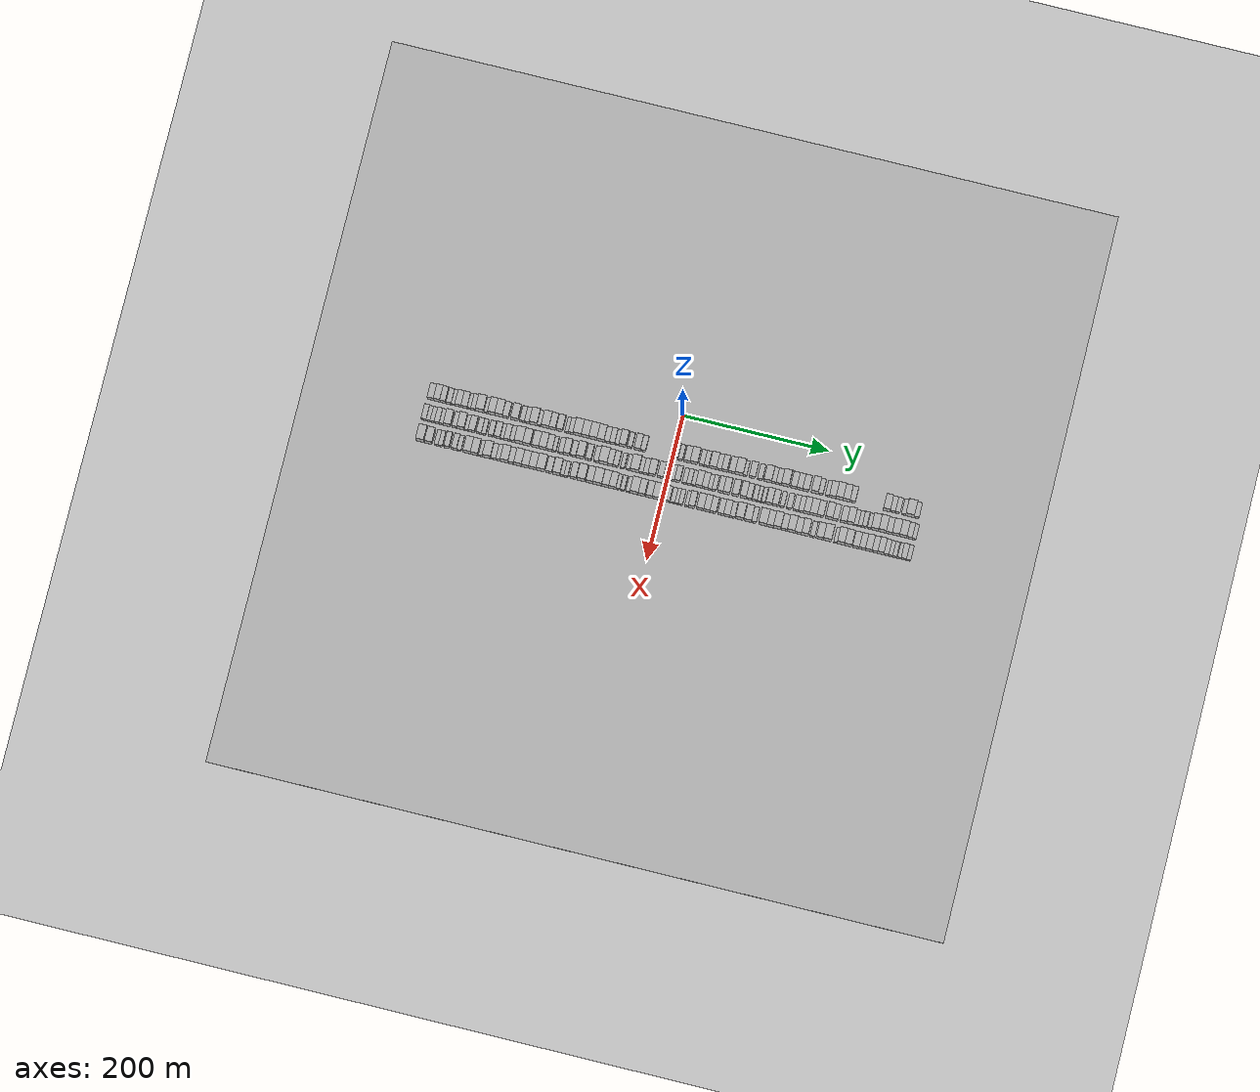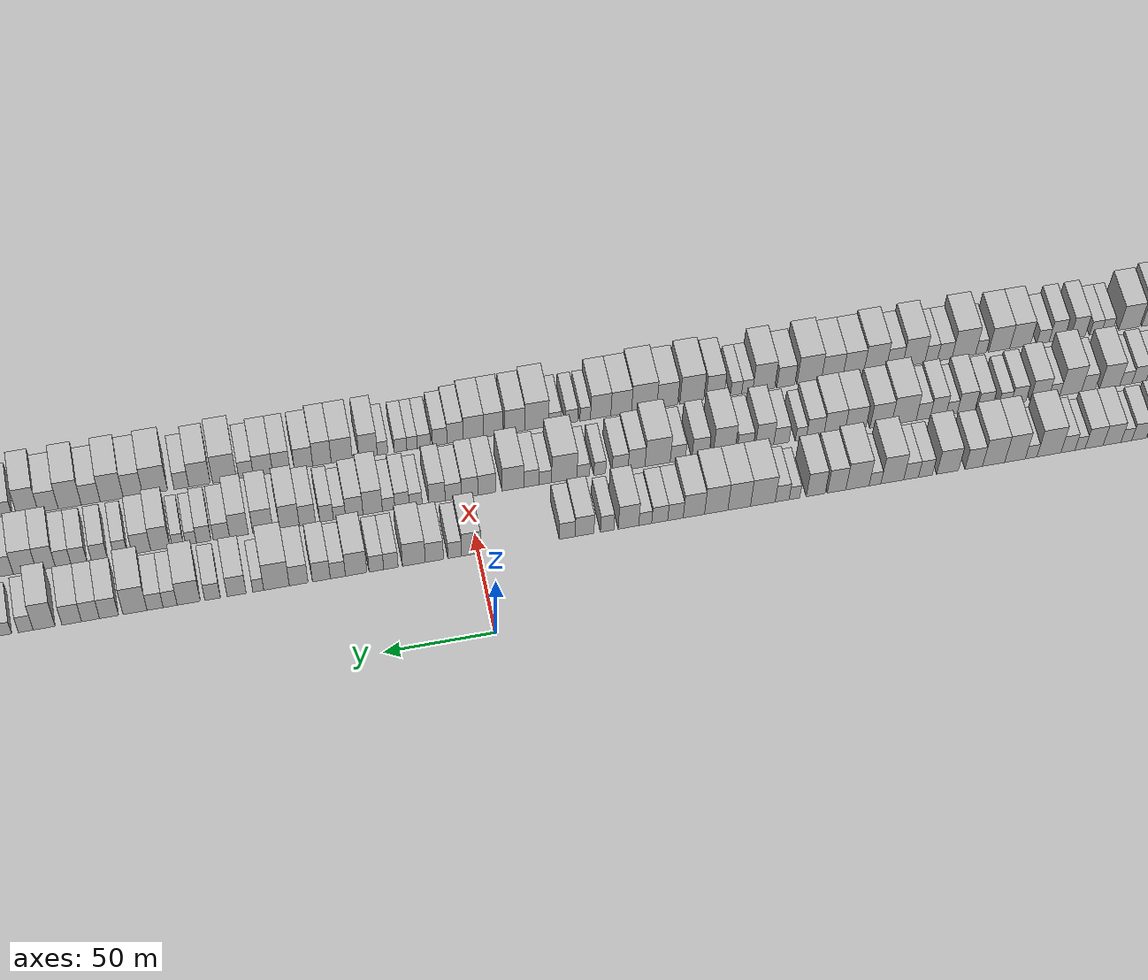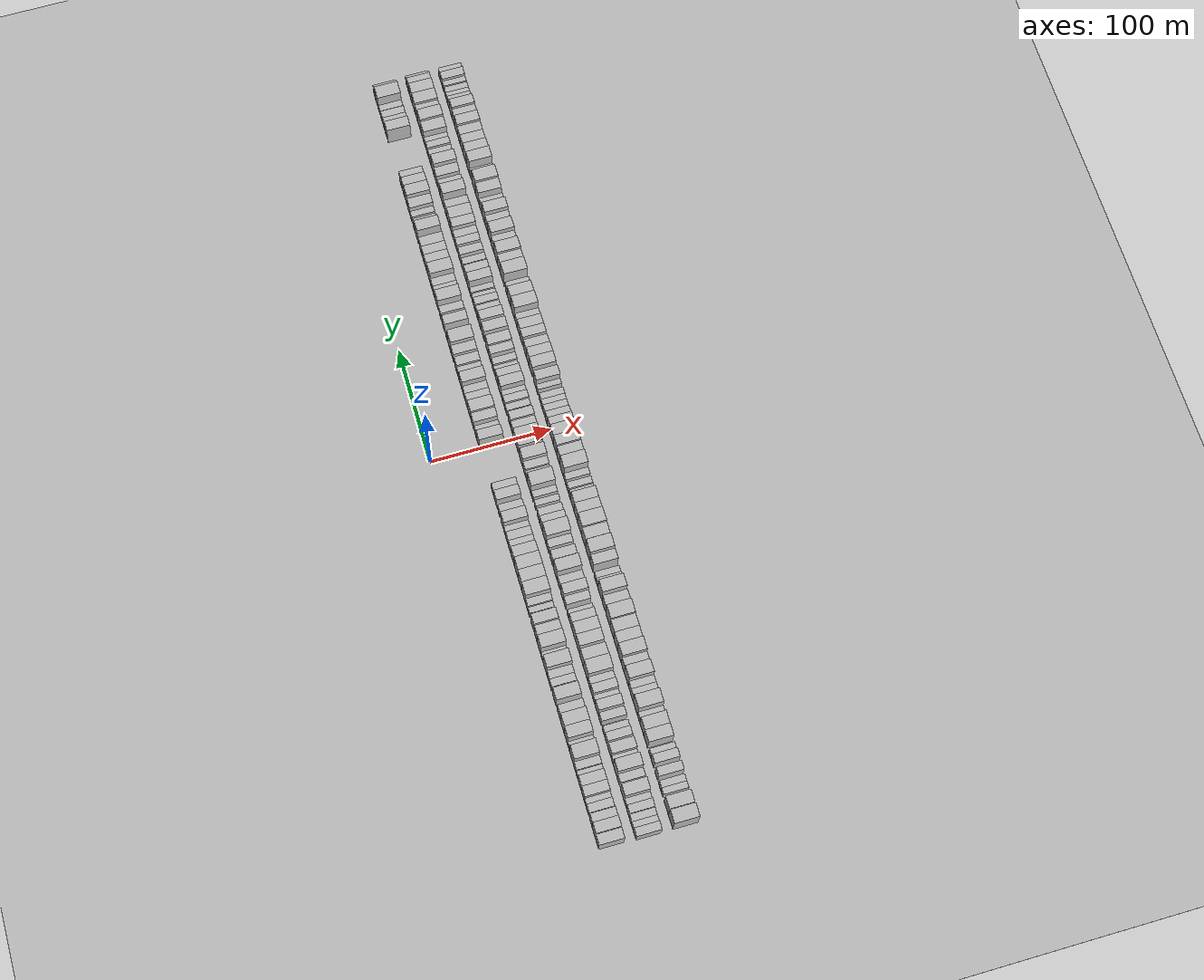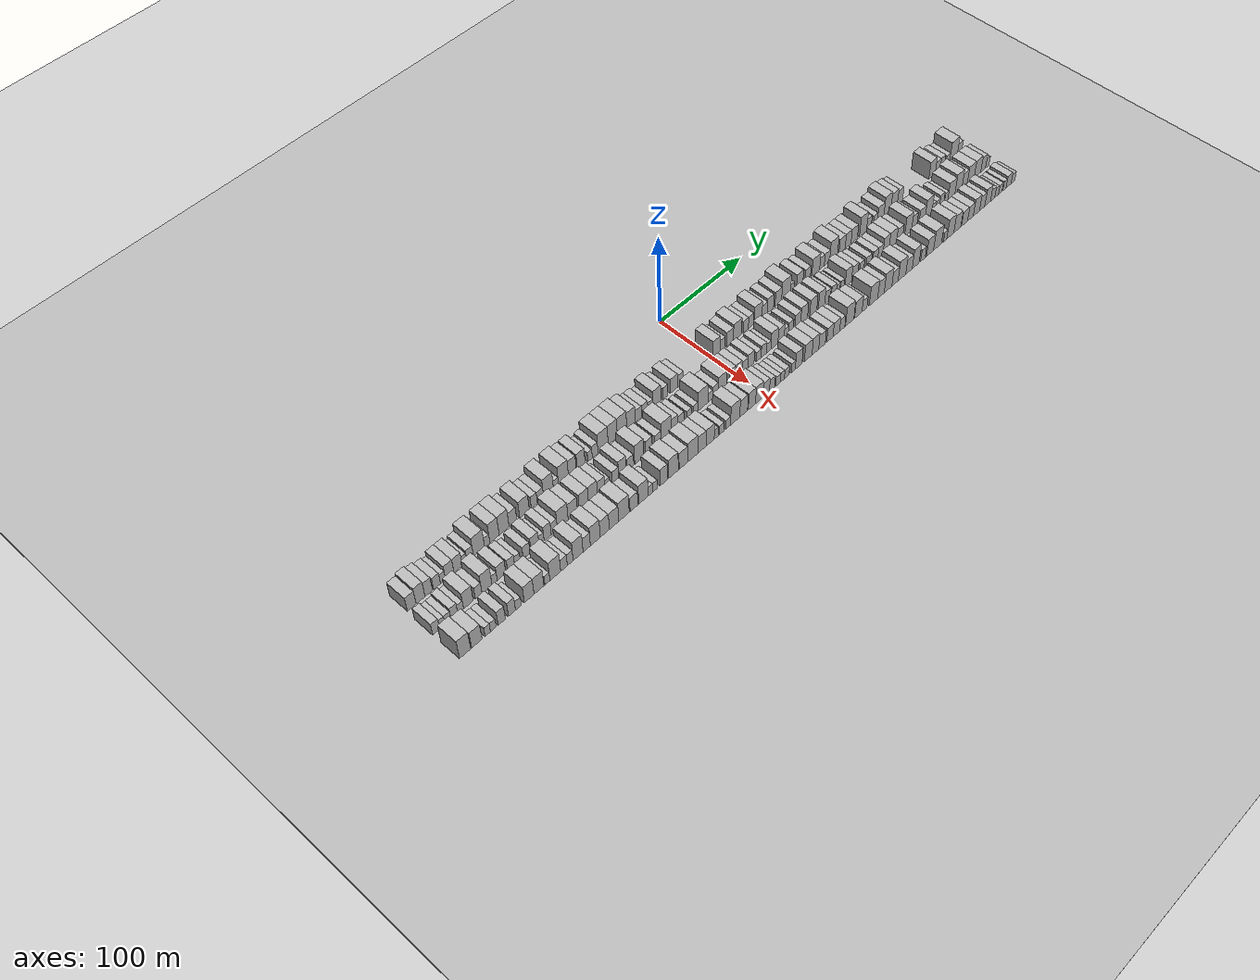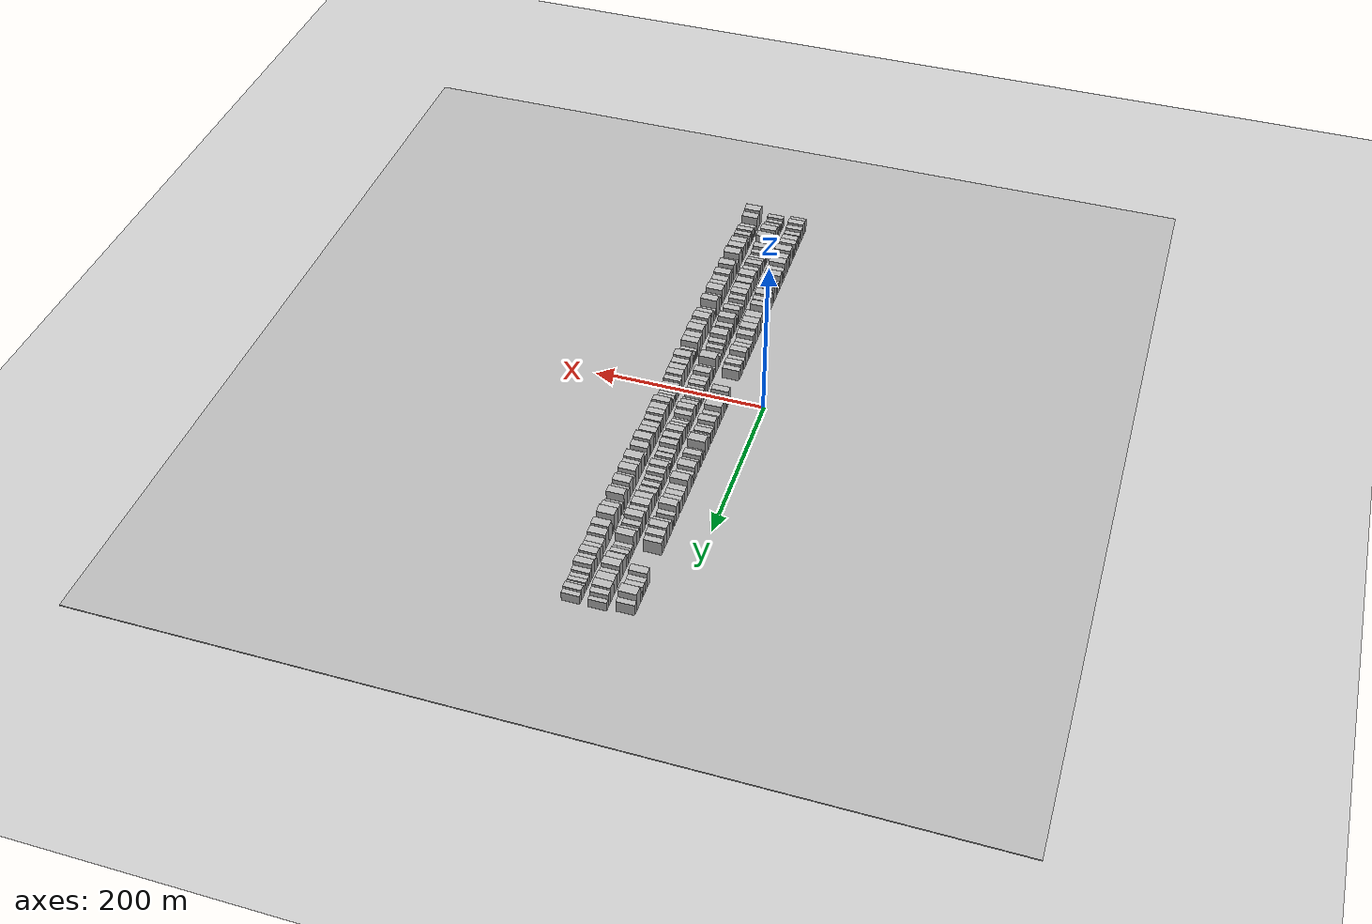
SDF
<?xml version="1.0" encoding="utf-8"?>

<sdf version="1.6">

   <world name="default">

      <gui fullscreen="0">

         <camera name="user_camera">

            <pose>-15 0 4.57585 0 0 0</pose>

            <view_controller>orbit</view_controller>

         </camera>

      </gui>

      <scene>

         <sky>

           <clouds>

             <speed>12</speed>

           </clouds>

         </sky>

         <ambient>0.4 0.4 0.4 1</ambient>

         <background>0.7 0.7 0.7 1</background>

         <shadows>1</shadows>

      </scene>

      <gravity>0 0 -9.8066</gravity>

      <magnetic_field>6e-06 2.3e-05 -4.2e-05</magnetic_field>

      <physics default="0" name="default_physics" type="ode">

         <ode>

            <solver>

               <type>quick</type>

               <iters>10</iters>

               <sor>1.0</sor>

               <use_dynamic_moi_rescaling>0</use_dynamic_moi_rescaling>

            </solver>

            <constraints>

               <cfm>0</cfm>

               <erp>0.2</erp>

               <contact_max_correcting_vel>100</contact_max_correcting_vel>

               <contact_surface_layer>0.001</contact_surface_layer>

            </constraints>

         </ode>

         <max_step_size>0.004</max_step_size>

         <real_time_factor>1</real_time_factor>

         <real_time_update_rate>250</real_time_update_rate>

      </physics>

      <light name="sun" type="directional">

         <cast_shadows>1</cast_shadows>

         <pose>0 0 10 0 0 0</pose>

         <diffuse>0.8 0.8 0.8 1</diffuse>

         <specular>0.2 0.2 0.2 1</specular>

         <attenuation>

            <range>1000</range>

            <constant>0.9</constant>

            <linear>0.01</linear>

            <quadratic>0.001</quadratic>

         </attenuation>

         <direction>-0.5 0.1 -0.9</direction>

      </light>

      <include>

         <name>ground_plane_1</name>

         <uri>model://HANNAS_ground_plane</uri>

         <pose>0 0 0  0 0 0</pose>

      </include>

      <include>

         <name>ground_plane_2</name>

         <uri>model://HANNAS_ground_plane</uri>

         <pose>100 0 0  0 0 0</pose>

      </include>

      <model name="building_1">

         <static>1</static>

         <pose frame="">50.0000 -330.7343 0 0.000000 0.000000 0.000000</pose>

         <link name="link">

            <pose frame="">0 0 9.00 0 0 0</pose>

            <collision name="collision">

               <geometry>

                  <box>

                     <size>20.0000 8.5314 18.0000</size>

                  </box>

               </geometry>

               <max_contacts>10</max_contacts>

               <surface>

                  <contact>

                     <ode/>

                  </contact>

                  <bounce/>

                  <friction>

                     <torsional>

                        <ode/>

                     </torsional>

                     <ode/>

                  </friction>

               </surface>

            </collision>

            <visual name="visual">

               <cast_shadows>0</cast_shadows>

               <geometry>

                  <box>

                     <size>20.0000 8.5314 18.0000</size>

                  </box>

               </geometry>

               <material>

                  <script>

                     <uri>model://HANNAS_wall/materials/scripts</uri>

                     <uri>model://HANNAS_wall/materials/textures</uri>

                     <name>vrc/HANNAS_wall</name>

                  </script>

               </material>

            </visual>

            <self_collide>0</self_collide>

            <enable_wind>0</enable_wind>

            <kinematic>0</kinematic>

         </link>

      </model>

      <model name="building_2">

         <static>1</static>

         <pose frame="">50.0000 -322.0787 0 0.000000 0.000000 0.000000</pose>

         <link name="link">

            <pose frame="">0 0 10.50 0 0 0</pose>

            <collision name="collision">

               <geometry>

                  <box>

                     <size>20.0000 8.7798 21.0000</size>

                  </box>

               </geometry>

               <max_contacts>10</max_contacts>

               <surface>

                  <contact>

                     <ode/>

                  </contact>

                  <bounce/>

                  <friction>

                     <torsional>

                        <ode/>

                     </torsional>

                     <ode/>

                  </friction>

               </surface>

            </collision>

            <visual name="visual">

               <cast_shadows>0</cast_shadows>

               <geometry>

                  <box>

                     <size>20.0000 8.7798 21.0000</size>

                  </box>

               </geometry>

               <material>

                  <script>

                     <uri>model://HANNAS_wall/materials/scripts</uri>

                     <uri>model://HANNAS_wall/materials/textures</uri>

                     <name>vrc/HANNAS_wall</name>

                  </script>

               </material>

            </visual>

            <self_collide>0</self_collide>

            <enable_wind>0</enable_wind>

            <kinematic>0</kinematic>

         </link>

      </model>

      <model name="building_3">

         <static>1</static>

         <pose frame="">50.0000 -313.9338 0 0.000000 0.000000 0.000000</pose>

         <link name="link">

            <pose frame="">0 0 9.00 0 0 0</pose>

            <collision name="collision">

               <geometry>

                  <box>

                     <size>20.0000 7.5100 18.0000</size>

                  </box>

               </geometry>

               <max_contacts>10</max_contacts>

               <surface>

                  <contact>

                     <ode/>

                  </contact>

                  <bounce/>

                  <friction>

                     <torsional>

                        <ode/>

                     </torsional>

                     <ode/>

                  </friction>

               </surface>

            </collision>

            <visual name="visual">

               <cast_shadows>0</cast_shadows>

               <geometry>

                  <box>

                     <size>20.0000 7.5100 18.0000</size>

                  </box>

               </geometry>

               <material>

                  <script>

                     <uri>model://HANNAS_wall/materials/scripts</uri>

                     <uri>model://HANNAS_wall/materials/textures</uri>

                     <name>vrc/HANNAS_wall</name>

                  </script>

               </material>

            </visual>

            <self_collide>0</self_collide>

            <enable_wind>0</enable_wind>

            <kinematic>0</kinematic>

         </link>

      </model>

      <model name="building_4">

         <static>1</static>

         <pose frame="">50.0000 -305.7042 0 0.000000 0.000000 0.000000</pose>

         <link name="link">

            <pose frame="">0 0 7.50 0 0 0</pose>

            <collision name="collision">

               <geometry>

                  <box>

                     <size>20.0000 6.9492 15.0000</size>

                  </box>

               </geometry>

               <max_contacts>10</max_contacts>

               <surface>

                  <contact>

                     <ode/>

                  </contact>

                  <bounce/>

                  <friction>

                     <torsional>

                        <ode/>

                     </torsional>

                     <ode/>

                  </friction>

               </surface>

            </collision>

            <visual name="visual">

               <cast_shadows>0</cast_shadows>

               <geometry>

                  <box>

                     <size>20.0000 6.9492 15.0000</size>

                  </box>

               </geometry>

               <material>

                  <script>

                     <uri>model://HANNAS_wall/materials/scripts</uri>

                     <uri>model://HANNAS_wall/materials/textures</uri>

                     <name>vrc/HANNAS_wall</name>

                  </script>

               </material>

            </visual>

            <self_collide>0</self_collide>

            <enable_wind>0</enable_wind>

            <kinematic>0</kinematic>

         </link>

      </model>

      <model name="building_5">

         <static>1</static>

         <pose frame="">50.0000 -299.6812 0 0.000000 0.000000 0.000000</pose>

         <link name="link">

            <pose frame="">0 0 6.00 0 0 0</pose>

            <collision name="collision">

               <geometry>

                  <box>

                     <size>20.0000 5.0968 12.0000</size>

                  </box>

               </geometry>

               <max_contacts>10</max_contacts>

               <surface>

                  <contact>

                     <ode/>

                  </contact>

                  <bounce/>

                  <friction>

                     <torsional>

                        <ode/>

                     </torsional>

                     <ode/>

                  </friction>

               </surface>

            </collision>

            <visual name="visual">

               <cast_shadows>0</cast_shadows>

               <geometry>

                  <box>

                     <size>20.0000 5.0968 12.0000</size>

                  </box>

               </geometry>

               <material>

                  <script>

                     <uri>model://HANNAS_wall/materials/scripts</uri>

                     <uri>model://HANNAS_wall/materials/textures</uri>

                     <name>vrc/HANNAS_wall</name>

                  </script>

               </material>

            </visual>

            <self_collide>0</self_collide>

            <enable_wind>0</enable_wind>

            <kinematic>0</kinematic>

         </link>

      </model>

      <model name="building_6">

         <static>1</static>

         <pose frame="">50.0000 -292.9258 0 0.000000 0.000000 0.000000</pose>

         <link name="link">

            <pose frame="">0 0 9.00 0 0 0</pose>

            <collision name="collision">

               <geometry>

                  <box>

                     <size>20.0000 8.4141 18.0000</size>

                  </box>

               </geometry>

               <max_contacts>10</max_contacts>

               <surface>

                  <contact>

                     <ode/>

                  </contact>

                  <bounce/>

                  <friction>

                     <torsional>

                        <ode/>

                     </torsional>

                     <ode/>

                  </friction>

               </surface>

            </collision>

            <visual name="visual">

               <cast_shadows>0</cast_shadows>

               <geometry>

                  <box>

                     <size>20.0000 8.4141 18.0000</size>

                  </box>

               </geometry>

               <material>

                  <script>

                     <uri>model://HANNAS_wall/materials/scripts</uri>

                     <uri>model://HANNAS_wall/materials/textures</uri>

                     <name>vrc/HANNAS_wall</name>

                  </script>

               </material>

            </visual>

            <self_collide>0</self_collide>

            <enable_wind>0</enable_wind>

            <kinematic>0</kinematic>

         </link>

      </model>

      <model name="building_7">

         <static>1</static>

         <pose frame="">50.0000 -284.4672 0 0.000000 0.000000 0.000000</pose>

         <link name="link">

            <pose frame="">0 0 9.00 0 0 0</pose>

            <collision name="collision">

               <geometry>

                  <box>

                     <size>20.0000 8.5032 18.0000</size>

                  </box>

               </geometry>

               <max_contacts>10</max_contacts>

               <surface>

                  <contact>

                     <ode/>

                  </contact>

                  <bounce/>

                  <friction>

                     <torsional>

                        <ode/>

                     </torsional>

                     <ode/>

                  </friction>

               </surface>

            </collision>

            <visual name="visual">

               <cast_shadows>0</cast_shadows>

               <geometry>

                  <box>

                     <size>20.0000 8.5032 18.0000</size>

                  </box>

               </geometry>

               <material>

                  <script>

                     <uri>model://HANNAS_wall/materials/scripts</uri>

                     <uri>model://HANNAS_wall/materials/textures</uri>

                     <name>vrc/HANNAS_wall</name>

                  </script>

               </material>

            </visual>

            <self_collide>0</self_collide>

            <enable_wind>0</enable_wind>

            <kinematic>0</kinematic>

         </link>

      </model>

      <model name="building_8">

         <static>1</static>

         <pose frame="">50.0000 -277.8155 0 0.000000 0.000000 0.000000</pose>

         <link name="link">

            <pose frame="">0 0 6.00 0 0 0</pose>

            <collision name="collision">

               <geometry>

                  <box>

                     <size>20.0000 4.8003 12.0000</size>

                  </box>

               </geometry>

               <max_contacts>10</max_contacts>

               <surface>

                  <contact>

                     <ode/>

                  </contact>

                  <bounce/>

                  <friction>

                     <torsional>

                        <ode/>

                     </torsional>

                     <ode/>

                  </friction>

               </surface>

            </collision>

            <visual name="visual">

               <cast_shadows>0</cast_shadows>

               <geometry>

                  <box>

                     <size>20.0000 4.8003 12.0000</size>

                  </box>

               </geometry>

               <material>

                  <script>

                     <uri>model://HANNAS_wall/materials/scripts</uri>

                     <uri>model://HANNAS_wall/materials/textures</uri>

                     <name>vrc/HANNAS_wall</name>

                  </script>

               </material>

            </visual>

            <self_collide>0</self_collide>

            <enable_wind>0</enable_wind>

            <kinematic>0</kinematic>

         </link>

      </model>

      <model name="building_9">

         <static>1</static>

         <pose frame="">50.0000 -272.0986 0 0.000000 0.000000 0.000000</pose>

         <link name="link">

            <pose frame="">0 0 7.50 0 0 0</pose>

            <collision name="collision">

               <geometry>

                  <box>

                     <size>20.0000 6.6334 15.0000</size>

                  </box>

               </geometry>

               <max_contacts>10</max_contacts>

               <surface>

                  <contact>

                     <ode/>

                  </contact>

                  <bounce/>

                  <friction>

                     <torsional>

                        <ode/>

                     </torsional>

                     <ode/>

                  </friction>

               </surface>

            </collision>

            <visual name="visual">

               <cast_shadows>0</cast_shadows>

               <geometry>

                  <box>

                     <size>20.0000 6.6334 15.0000</size>

                  </box>

               </geometry>

               <material>

                  <script>

                     <uri>model://HANNAS_wall/materials/scripts</uri>

                     <uri>model://HANNAS_wall/materials/textures</uri>

                     <name>vrc/HANNAS_wall</name>

                  </script>

               </material>

            </visual>

            <self_collide>0</self_collide>

            <enable_wind>0</enable_wind>

            <kinematic>0</kinematic>

         </link>

      </model>

      <model name="building_10">

         <static>1</static>

         <pose frame="">50.0000 -263.1139 0 0.000000 0.000000 0.000000</pose>

         <link name="link">

            <pose frame="">0 0 12.00 0 0 0</pose>

            <collision name="collision">

               <geometry>

                  <box>

                     <size>20.0000 11.3362 24.0000</size>

                  </box>

               </geometry>

               <max_contacts>10</max_contacts>

               <surface>

                  <contact>

                     <ode/>

                  </contact>

                  <bounce/>

                  <friction>

                     <torsional>

                        <ode/>

                     </torsional>

                     <ode/>

                  </friction>

               </surface>

            </collision>

            <visual name="visual">

               <cast_shadows>0</cast_shadows>

               <geometry>

                  <box>

                     <size>20.0000 11.3362 24.0000</size>

                  </box>

               </geometry>

               <material>

                  <script>

                     <uri>model://HANNAS_wall/materials/scripts</uri>

                     <uri>model://HANNAS_wall/materials/textures</uri>

                     <name>vrc/HANNAS_wall</name>

                  </script>

               </material>

            </visual>

            <self_collide>0</self_collide>

            <enable_wind>0</enable_wind>

            <kinematic>0</kinematic>

         </link>

      </model>

      <model name="building_11">

         <static>1</static>

         <pose frame="">50.0000 -254.7242 0 0.000000 0.000000 0.000000</pose>

         <link name="link">

            <pose frame="">0 0 6.00 0 0 0</pose>

            <collision name="collision">

               <geometry>

                  <box>

                     <size>20.0000 5.4431 12.0000</size>

                  </box>

               </geometry>

               <max_contacts>10</max_contacts>

               <surface>

                  <contact>

                     <ode/>

                  </contact>

                  <bounce/>

                  <friction>

                     <torsional>

                        <ode/>

                     </torsional>

                     <ode/>

                  </friction>

               </surface>

            </collision>

            <visual name="visual">

               <cast_shadows>0</cast_shadows>

               <geometry>

                  <box>

                     <size>20.0000 5.4431 12.0000</size>

                  </box>

               </geometry>

               <material>

                  <script>

                     <uri>model://HANNAS_wall/materials/scripts</uri>

                     <uri>model://HANNAS_wall/materials/textures</uri>

                     <name>vrc/HANNAS_wall</name>

                  </script>

               </material>

            </visual>

            <self_collide>0</self_collide>

            <enable_wind>0</enable_wind>

            <kinematic>0</kinematic>

         </link>

      </model>

      <model name="building_12">

         <static>1</static>

         <pose frame="">50.0000 -247.1628 0 0.000000 0.000000 0.000000</pose>

         <link name="link">

            <pose frame="">0 0 12.00 0 0 0</pose>

            <collision name="collision">

               <geometry>

                  <box>

                     <size>20.0000 9.6796 24.0000</size>

                  </box>

               </geometry>

               <max_contacts>10</max_contacts>

               <surface>

                  <contact>

                     <ode/>

                  </contact>

                  <bounce/>

                  <friction>

                     <torsional>

                        <ode/>

                     </torsional>

                     <ode/>

                  </friction>

               </surface>

            </collision>

            <visual name="visual">

               <cast_shadows>0</cast_shadows>

               <geometry>

                  <box>

                     <size>20.0000 9.6796 24.0000</size>

                  </box>

               </geometry>

               <material>

                  <script>

                     <uri>model://HANNAS_wall/materials/scripts</uri>

                     <uri>model://HANNAS_wall/materials/textures</uri>

                     <name>vrc/HANNAS_wall</name>

                  </script>

               </material>

            </visual>

            <self_collide>0</self_collide>

            <enable_wind>0</enable_wind>

            <kinematic>0</kinematic>

         </link>

      </model>

      <model name="building_13">

         <static>1</static>

         <pose frame="">50.0000 -237.1223 0 0.000000 0.000000 0.000000</pose>

         <link name="link">

            <pose frame="">0 0 12.00 0 0 0</pose>

            <collision name="collision">

               <geometry>

                  <box>

                     <size>20.0000 10.4014 24.0000</size>

                  </box>

               </geometry>

               <max_contacts>10</max_contacts>

               <surface>

                  <contact>

                     <ode/>

                  </contact>

                  <bounce/>

                  <friction>

                     <torsional>

                        <ode/>

                     </torsional>

                     <ode/>

                  </friction>

               </surface>

            </collision>

            <visual name="visual">

               <cast_shadows>0</cast_shadows>

               <geometry>

                  <box>

                     <size>20.0000 10.4014 24.0000</size>

                  </box>

               </geometry>

               <material>

                  <script>

                     <uri>model://HANNAS_wall/materials/scripts</uri>

                     <uri>model://HANNAS_wall/materials/textures</uri>

                     <name>vrc/HANNAS_wall</name>

                  </script>

               </material>

            </visual>

            <self_collide>0</self_collide>

            <enable_wind>0</enable_wind>

            <kinematic>0</kinematic>

         </link>

      </model>

      <model name="building_14">

         <static>1</static>

         <pose frame="">50.0000 -227.8176 0 0.000000 0.000000 0.000000</pose>

         <link name="link">

            <pose frame="">0 0 9.00 0 0 0</pose>

            <collision name="collision">

               <geometry>

                  <box>

                     <size>20.0000 8.2081 18.0000</size>

                  </box>

               </geometry>

               <max_contacts>10</max_contacts>

               <surface>

                  <contact>

                     <ode/>

                  </contact>

                  <bounce/>

                  <friction>

                     <torsional>

                        <ode/>

                     </torsional>

                     <ode/>

                  </friction>

               </surface>

            </collision>

            <visual name="visual">

               <cast_shadows>0</cast_shadows>

               <geometry>

                  <box>

                     <size>20.0000 8.2081 18.0000</size>

                  </box>

               </geometry>

               <material>

                  <script>

                     <uri>model://HANNAS_wall/materials/scripts</uri>

                     <uri>model://HANNAS_wall/materials/textures</uri>

                     <name>vrc/HANNAS_wall</name>

                  </script>

               </material>

            </visual>

            <self_collide>0</self_collide>

            <enable_wind>0</enable_wind>

            <kinematic>0</kinematic>

         </link>

      </model>

      <model name="building_15">

         <static>1</static>

         <pose frame="">50.0000 -215.6011 0 0.000000 0.000000 0.000000</pose>

         <link name="link">

            <pose frame="">0 0 10.50 0 0 0</pose>

            <collision name="collision">

               <geometry>

                  <box>

                     <size>20.0000 10.2249 21.0000</size>

                  </box>

               </geometry>

               <max_contacts>10</max_contacts>

               <surface>

                  <contact>

                     <ode/>

                  </contact>

                  <bounce/>

                  <friction>

                     <torsional>

                        <ode/>

                     </torsional>

                     <ode/>

                  </friction>

               </surface>

            </collision>

            <visual name="visual">

               <cast_shadows>0</cast_shadows>

               <geometry>

                  <box>

                     <size>20.0000 10.2249 21.0000</size>

                  </box>

               </geometry>

               <material>

                  <script>

                     <uri>model://HANNAS_wall/materials/scripts</uri>

                     <uri>model://HANNAS_wall/materials/textures</uri>

                     <name>vrc/HANNAS_wall</name>

                  </script>

               </material>

            </visual>

            <self_collide>0</self_collide>

            <enable_wind>0</enable_wind>

            <kinematic>0</kinematic>

         </link>

      </model>

      <model name="building_16">

         <static>1</static>

         <pose frame="">50.0000 -205.2394 0 0.000000 0.000000 0.000000</pose>

         <link name="link">

            <pose frame="">0 0 7.50 0 0 0</pose>

            <collision name="collision">

               <geometry>

                  <box>

                     <size>20.0000 6.4983 15.0000</size>

                  </box>

               </geometry>

               <max_contacts>10</max_contacts>

               <surface>

                  <contact>

                     <ode/>

                  </contact>

                  <bounce/>

                  <friction>

                     <torsional>

                        <ode/>

                     </torsional>

                     <ode/>

                  </friction>

               </surface>

            </collision>

            <visual name="visual">

               <cast_shadows>0</cast_shadows>

               <geometry>

                  <box>

                     <size>20.0000 6.4983 15.0000</size>

                  </box>

               </geometry>

               <material>

                  <script>

                     <uri>model://HANNAS_wall/materials/scripts</uri>

                     <uri>model://HANNAS_wall/materials/textures</uri>

                     <name>vrc/HANNAS_wall</name>

                  </script>

               </material>

            </visual>

            <self_collide>0</self_collide>

            <enable_wind>0</enable_wind>

            <kinematic>0</kinematic>

         </link>

      </model>

      <model name="building_17">

         <static>1</static>

         <pose frame="">50.0000 -198.5516 0 0.000000 0.000000 0.000000</pose>

         <link name="link">

            <pose frame="">0 0 7.50 0 0 0</pose>

            <collision name="collision">

               <geometry>

                  <box>

                     <size>20.0000 6.8773 15.0000</size>

                  </box>

               </geometry>

               <max_contacts>10</max_contacts>

               <surface>

                  <contact>

                     <ode/>

                  </contact>

                  <bounce/>

                  <friction>

                     <torsional>

                        <ode/>

                     </torsional>

                     <ode/>

                  </friction>

               </surface>

            </collision>

            <visual name="visual">

               <cast_shadows>0</cast_shadows>

               <geometry>

                  <box>

                     <size>20.0000 6.8773 15.0000</size>

                  </box>

               </geometry>

               <material>

                  <script>

                     <uri>model://HANNAS_wall/materials/scripts</uri>

                     <uri>model://HANNAS_wall/materials/textures</uri>

                     <name>vrc/HANNAS_wall</name>

                  </script>

               </material>

            </visual>

            <self_collide>0</self_collide>

            <enable_wind>0</enable_wind>

            <kinematic>0</kinematic>

         </link>

      </model>

      <model name="building_18">

         <static>1</static>

         <pose frame="">50.0000 -189.7790 0 0.000000 0.000000 0.000000</pose>

         <link name="link">

            <pose frame="">0 0 12.00 0 0 0</pose>

            <collision name="collision">

               <geometry>

                  <box>

                     <size>20.0000 10.6680 24.0000</size>

                  </box>

               </geometry>

               <max_contacts>10</max_contacts>

               <surface>

                  <contact>

                     <ode/>

                  </contact>

                  <bounce/>

                  <friction>

                     <torsional>

                        <ode/>

                     </torsional>

                     <ode/>

                  </friction>

               </surface>

            </collision>

            <visual name="visual">

               <cast_shadows>0</cast_shadows>

               <geometry>

                  <box>

                     <size>20.0000 10.6680 24.0000</size>

                  </box>

               </geometry>

               <material>

                  <script>

                     <uri>model://HANNAS_wall/materials/scripts</uri>

                     <uri>model://HANNAS_wall/materials/textures</uri>

                     <name>vrc/HANNAS_wall</name>

                  </script>

               </material>

            </visual>

            <self_collide>0</self_collide>

            <enable_wind>0</enable_wind>

            <kinematic>0</kinematic>

         </link>

      </model>

      <model name="building_19">

         <static>1</static>

         <pose frame="">50.0000 -181.6937 0 0.000000 0.000000 0.000000</pose>

         <link name="link">

            <pose frame="">0 0 6.00 0 0 0</pose>

            <collision name="collision">

               <geometry>

                  <box>

                     <size>20.0000 5.5027 12.0000</size>

                  </box>

               </geometry>

               <max_contacts>10</max_contacts>

               <surface>

                  <contact>

                     <ode/>

                  </contact>

                  <bounce/>

                  <friction>

                     <torsional>

                        <ode/>

                     </torsional>

                     <ode/>

                  </friction>

               </surface>

            </collision>

            <visual name="visual">

               <cast_shadows>0</cast_shadows>

               <geometry>

                  <box>

                     <size>20.0000 5.5027 12.0000</size>

                  </box>

               </geometry>

               <material>

                  <script>

                     <uri>model://HANNAS_wall/materials/scripts</uri>

                     <uri>model://HANNAS_wall/materials/textures</uri>

                     <name>vrc/HANNAS_wall</name>

                  </script>

               </material>

            </visual>

            <self_collide>0</self_collide>

            <enable_wind>0</enable_wind>

            <kinematic>0</kinematic>

         </link>

      </model>

      <model name="building_20">

         <static>1</static>

         <pose frame="">50.0000 -173.5336 0 0.000000 0.000000 0.000000</pose>

         <link name="link">

            <pose frame="">0 0 12.00 0 0 0</pose>

            <collision name="collision">

               <geometry>

                  <box>

                     <size>20.0000 10.8174 24.0000</size>

                  </box>

               </geometry>

               <max_contacts>10</max_contacts>

               <surface>

                  <contact>

                     <ode/>

                  </contact>

                  <bounce/>

                  <friction>

                     <torsional>

                        <ode/>

                     </torsional>

                     <ode/>

                  </friction>

               </surface>

            </collision>

            <visual name="visual">

               <cast_shadows>0</cast_shadows>

               <geometry>

                  <box>

                     <size>20.0000 10.8174 24.0000</size>

                  </box>

               </geometry>

               <material>

                  <script>

                     <uri>model://HANNAS_wall/materials/scripts</uri>

                     <uri>model://HANNAS_wall/materials/textures</uri>

                     <name>vrc/HANNAS_wall</name>

                  </script>

               </material>

            </visual>

            <self_collide>0</self_collide>

            <enable_wind>0</enable_wind>

            <kinematic>0</kinematic>

         </link>

      </model>

      <model name="building_21">

         <static>1</static>

         <pose frame="">50.0000 -163.8275 0 0.000000 0.000000 0.000000</pose>

         <link name="link">

            <pose frame="">0 0 10.50 0 0 0</pose>

            <collision name="collision">

               <geometry>

                  <box>

                     <size>20.0000 8.5949 21.0000</size>

                  </box>

               </geometry>

               <max_contacts>10</max_contacts>

               <surface>

                  <contact>

                     <ode/>

                  </contact>

                  <bounce/>

                  <friction>

                     <torsional>

                        <ode/>

                     </torsional>

                     <ode/>

                  </friction>

               </surface>

            </collision>

            <visual name="visual">

               <cast_shadows>0</cast_shadows>

               <geometry>

                  <box>

                     <size>20.0000 8.5949 21.0000</size>

                  </box>

               </geometry>

               <material>

                  <script>

                     <uri>model://HANNAS_wall/materials/scripts</uri>

                     <uri>model://HANNAS_wall/materials/textures</uri>

                     <name>vrc/HANNAS_wall</name>

                  </script>

               </material>

            </visual>

            <self_collide>0</self_collide>

            <enable_wind>0</enable_wind>

            <kinematic>0</kinematic>

         </link>

      </model>

      <model name="building_22">

         <static>1</static>

         <pose frame="">50.0000 -154.1561 0 0.000000 0.000000 0.000000</pose>

         <link name="link">

            <pose frame="">0 0 10.50 0 0 0</pose>

            <collision name="collision">

               <geometry>

                  <box>

                     <size>20.0000 8.7478 21.0000</size>

                  </box>

               </geometry>

               <max_contacts>10</max_contacts>

               <surface>

                  <contact>

                     <ode/>

                  </contact>

                  <bounce/>

                  <friction>

                     <torsional>

                        <ode/>

                     </torsional>

                     <ode/>

                  </friction>

               </surface>

            </collision>

            <visual name="visual">

               <cast_shadows>0</cast_shadows>

               <geometry>

                  <box>

                     <size>20.0000 8.7478 21.0000</size>

                  </box>

               </geometry>

               <material>

                  <script>

                     <uri>model://HANNAS_wall/materials/scripts</uri>

                     <uri>model://HANNAS_wall/materials/textures</uri>

                     <name>vrc/HANNAS_wall</name>

                  </script>

               </material>

            </visual>

            <self_collide>0</self_collide>

            <enable_wind>0</enable_wind>

            <kinematic>0</kinematic>

         </link>

      </model>

      <model name="building_23">

         <static>1</static>

         <pose frame="">50.0000 -144.3071 0 0.000000 0.000000 0.000000</pose>

         <link name="link">

            <pose frame="">0 0 6.00 0 0 0</pose>

            <collision name="collision">

               <geometry>

                  <box>

                     <size>20.0000 4.9503 12.0000</size>

                  </box>

               </geometry>

               <max_contacts>10</max_contacts>

               <surface>

                  <contact>

                     <ode/>

                  </contact>

                  <bounce/>

                  <friction>

                     <torsional>

                        <ode/>

                     </torsional>

                     <ode/>

                  </friction>

               </surface>

            </collision>

            <visual name="visual">

               <cast_shadows>0</cast_shadows>

               <geometry>

                  <box>

                     <size>20.0000 4.9503 12.0000</size>

                  </box>

               </geometry>

               <material>

                  <script>

                     <uri>model://HANNAS_wall/materials/scripts</uri>

                     <uri>model://HANNAS_wall/materials/textures</uri>

                     <name>vrc/HANNAS_wall</name>

                  </script>

               </material>

            </visual>

            <self_collide>0</self_collide>

            <enable_wind>0</enable_wind>

            <kinematic>0</kinematic>

         </link>

      </model>

      <model name="building_24">

         <static>1</static>

         <pose frame="">50.0000 -138.6145 0 0.000000 0.000000 0.000000</pose>

         <link name="link">

            <pose frame="">0 0 7.50 0 0 0</pose>

            <collision name="collision">

               <geometry>

                  <box>

                     <size>20.0000 6.4349 15.0000</size>

                  </box>

               </geometry>

               <max_contacts>10</max_contacts>

               <surface>

                  <contact>

                     <ode/>

                  </contact>

                  <bounce/>

                  <friction>

                     <torsional>

                        <ode/>

                     </torsional>

                     <ode/>

                  </friction>

               </surface>

            </collision>

            <visual name="visual">

               <cast_shadows>0</cast_shadows>

               <geometry>

                  <box>

                     <size>20.0000 6.4349 15.0000</size>

                  </box>

               </geometry>

               <material>

                  <script>

                     <uri>model://HANNAS_wall/materials/scripts</uri>

                     <uri>model://HANNAS_wall/materials/textures</uri>

                     <name>vrc/HANNAS_wall</name>

                  </script>

               </material>

            </visual>

            <self_collide>0</self_collide>

            <enable_wind>0</enable_wind>

            <kinematic>0</kinematic>

         </link>

      </model>

      <model name="building_25">

         <static>1</static>

         <pose frame="">50.0000 -129.6808 0 0.000000 0.000000 0.000000</pose>

         <link name="link">

            <pose frame="">0 0 12.00 0 0 0</pose>

            <collision name="collision">

               <geometry>

                  <box>

                     <size>20.0000 11.4326 24.0000</size>

                  </box>

               </geometry>

               <max_contacts>10</max_contacts>

               <surface>

                  <contact>

                     <ode/>

                  </contact>

                  <bounce/>

                  <friction>

                     <torsional>

                        <ode/>

                     </torsional>

                     <ode/>

                  </friction>

               </surface>

            </collision>

            <visual name="visual">

               <cast_shadows>0</cast_shadows>

               <geometry>

                  <box>

                     <size>20.0000 11.4326 24.0000</size>

                  </box>

               </geometry>

               <material>

                  <script>

                     <uri>model://HANNAS_wall/materials/scripts</uri>

                     <uri>model://HANNAS_wall/materials/textures</uri>

                     <name>vrc/HANNAS_wall</name>

                  </script>

               </material>

            </visual>

            <self_collide>0</self_collide>

            <enable_wind>0</enable_wind>

            <kinematic>0</kinematic>

         </link>

      </model>

      <model name="building_26">

         <static>1</static>

         <pose frame="">50.0000 -118.7678 0 0.000000 0.000000 0.000000</pose>

         <link name="link">

            <pose frame="">0 0 12.00 0 0 0</pose>

            <collision name="collision">

               <geometry>

                  <box>

                     <size>20.0000 10.3935 24.0000</size>

                  </box>

               </geometry>

               <max_contacts>10</max_contacts>

               <surface>

                  <contact>

                     <ode/>

                  </contact>

                  <bounce/>

                  <friction>

                     <torsional>

                        <ode/>

                     </torsional>

                     <ode/>

                  </friction>

               </surface>

            </collision>

            <visual name="visual">

               <cast_shadows>0</cast_shadows>

               <geometry>

                  <box>

                     <size>20.0000 10.3935 24.0000</size>

                  </box>

               </geometry>

               <material>

                  <script>

                     <uri>model://HANNAS_wall/materials/scripts</uri>

                     <uri>model://HANNAS_wall/materials/textures</uri>

                     <name>vrc/HANNAS_wall</name>

                  </script>

               </material>

            </visual>

            <self_collide>0</self_collide>

            <enable_wind>0</enable_wind>

            <kinematic>0</kinematic>

         </link>

      </model>

      <model name="building_27">

         <static>1</static>

         <pose frame="">50.0000 -108.1884 0 0.000000 0.000000 0.000000</pose>

         <link name="link">

            <pose frame="">0 0 12.00 0 0 0</pose>

            <collision name="collision">

               <geometry>

                  <box>

                     <size>20.0000 10.7653 24.0000</size>

                  </box>

               </geometry>

               <max_contacts>10</max_contacts>

               <surface>

                  <contact>

                     <ode/>

                  </contact>

                  <bounce/>

                  <friction>

                     <torsional>

                        <ode/>

                     </torsional>

                     <ode/>

                  </friction>

               </surface>

            </collision>

            <visual name="visual">

               <cast_shadows>0</cast_shadows>

               <geometry>

                  <box>

                     <size>20.0000 10.7653 24.0000</size>

                  </box>

               </geometry>

               <material>

                  <script>

                     <uri>model://HANNAS_wall/materials/scripts</uri>

                     <uri>model://HANNAS_wall/materials/textures</uri>

                     <name>vrc/HANNAS_wall</name>

                  </script>

               </material>

            </visual>

            <self_collide>0</self_collide>

            <enable_wind>0</enable_wind>

            <kinematic>0</kinematic>

         </link>

      </model>

      <model name="building_28">

         <static>1</static>

         <pose frame="">50.0000 -97.9001 0 0.000000 0.000000 0.000000</pose>

         <link name="link">

            <pose frame="">0 0 10.50 0 0 0</pose>

            <collision name="collision">

               <geometry>

                  <box>

                     <size>20.0000 9.8113 21.0000</size>

                  </box>

               </geometry>

               <max_contacts>10</max_contacts>

               <surface>

                  <contact>

                     <ode/>

                  </contact>

                  <bounce/>

                  <friction>

                     <torsional>

                        <ode/>

                     </torsional>

                     <ode/>

                  </friction>

               </surface>

            </collision>

            <visual name="visual">

               <cast_shadows>0</cast_shadows>

               <geometry>

                  <box>

                     <size>20.0000 9.8113 21.0000</size>

                  </box>

               </geometry>

               <material>

                  <script>

                     <uri>model://HANNAS_wall/materials/scripts</uri>

                     <uri>model://HANNAS_wall/materials/textures</uri>

                     <name>vrc/HANNAS_wall</name>

                  </script>

               </material>

            </visual>

            <self_collide>0</self_collide>

            <enable_wind>0</enable_wind>

            <kinematic>0</kinematic>

         </link>

      </model>

      <model name="building_29">

         <static>1</static>

         <pose frame="">50.0000 -89.4312 0 0.000000 0.000000 0.000000</pose>

         <link name="link">

            <pose frame="">0 0 7.50 0 0 0</pose>

            <collision name="collision">

               <geometry>

                  <box>

                     <size>20.0000 7.1264 15.0000</size>

                  </box>

               </geometry>

               <max_contacts>10</max_contacts>

               <surface>

                  <contact>

                     <ode/>

                  </contact>

                  <bounce/>

                  <friction>

                     <torsional>

                        <ode/>

                     </torsional>

                     <ode/>

                  </friction>

               </surface>

            </collision>

            <visual name="visual">

               <cast_shadows>0</cast_shadows>

               <geometry>

                  <box>

                     <size>20.0000 7.1264 15.0000</size>

                  </box>

               </geometry>

               <material>

                  <script>

                     <uri>model://HANNAS_wall/materials/scripts</uri>

                     <uri>model://HANNAS_wall/materials/textures</uri>

                     <name>vrc/HANNAS_wall</name>

                  </script>

               </material>

            </visual>

            <self_collide>0</self_collide>

            <enable_wind>0</enable_wind>

            <kinematic>0</kinematic>

         </link>

      </model>

      <model name="building_30">

         <static>1</static>

         <pose frame="">50.0000 -82.1984 0 0.000000 0.000000 0.000000</pose>

         <link name="link">

            <pose frame="">0 0 7.50 0 0 0</pose>

            <collision name="collision">

               <geometry>

                  <box>

                     <size>20.0000 7.3392 15.0000</size>

                  </box>

               </geometry>

               <max_contacts>10</max_contacts>

               <surface>

                  <contact>

                     <ode/>

                  </contact>

                  <bounce/>

                  <friction>

                     <torsional>

                        <ode/>

                     </torsional>

                     <ode/>

                  </friction>

               </surface>

            </collision>

            <visual name="visual">

               <cast_shadows>0</cast_shadows>

               <geometry>

                  <box>

                     <size>20.0000 7.3392 15.0000</size>

                  </box>

               </geometry>

               <material>

                  <script>

                     <uri>model://HANNAS_wall/materials/scripts</uri>

                     <uri>model://HANNAS_wall/materials/textures</uri>

                     <name>vrc/HANNAS_wall</name>

                  </script>

               </material>

            </visual>

            <self_collide>0</self_collide>

            <enable_wind>0</enable_wind>

            <kinematic>0</kinematic>

         </link>

      </model>

      <model name="building_31">

         <static>1</static>

         <pose frame="">50.0000 -75.5507 0 0.000000 0.000000 0.000000</pose>

         <link name="link">

            <pose frame="">0 0 6.00 0 0 0</pose>

            <collision name="collision">

               <geometry>

                  <box>

                     <size>20.0000 5.9562 12.0000</size>

                  </box>

               </geometry>

               <max_contacts>10</max_contacts>

               <surface>

                  <contact>

                     <ode/>

                  </contact>

                  <bounce/>

                  <friction>

                     <torsional>

                        <ode/>

                     </torsional>

                     <ode/>

                  </friction>

               </surface>

            </collision>

            <visual name="visual">

               <cast_shadows>0</cast_shadows>

               <geometry>

                  <box>

                     <size>20.0000 5.9562 12.0000</size>

                  </box>

               </geometry>

               <material>

                  <script>

                     <uri>model://HANNAS_wall/materials/scripts</uri>

                     <uri>model://HANNAS_wall/materials/textures</uri>

                     <name>vrc/HANNAS_wall</name>

                  </script>

               </material>

            </visual>

            <self_collide>0</self_collide>

            <enable_wind>0</enable_wind>

            <kinematic>0</kinematic>

         </link>

      </model>

      <model name="building_32">

         <static>1</static>

         <pose frame="">50.0000 -67.8765 0 0.000000 0.000000 0.000000</pose>

         <link name="link">

            <pose frame="">0 0 10.50 0 0 0</pose>

            <collision name="collision">

               <geometry>

                  <box>

                     <size>20.0000 9.3921 21.0000</size>

                  </box>

               </geometry>

               <max_contacts>10</max_contacts>

               <surface>

                  <contact>

                     <ode/>

                  </contact>

                  <bounce/>

                  <friction>

                     <torsional>

                        <ode/>

                     </torsional>

                     <ode/>

                  </friction>

               </surface>

            </collision>

            <visual name="visual">

               <cast_shadows>0</cast_shadows>

               <geometry>

                  <box>

                     <size>20.0000 9.3921 21.0000</size>

                  </box>

               </geometry>

               <material>

                  <script>

                     <uri>model://HANNAS_wall/materials/scripts</uri>

                     <uri>model://HANNAS_wall/materials/textures</uri>

                     <name>vrc/HANNAS_wall</name>

                  </script>

               </material>

            </visual>

            <self_collide>0</self_collide>

            <enable_wind>0</enable_wind>

            <kinematic>0</kinematic>

         </link>

      </model>

      <model name="building_33">

         <static>1</static>

         <pose frame="">50.0000 -58.1200 0 0.000000 0.000000 0.000000</pose>

         <link name="link">

            <pose frame="">0 0 7.50 0 0 0</pose>

            <collision name="collision">

               <geometry>

                  <box>

                     <size>20.0000 6.1209 15.0000</size>

                  </box>

               </geometry>

               <max_contacts>10</max_contacts>

               <surface>

                  <contact>

                     <ode/>

                  </contact>

                  <bounce/>

                  <friction>

                     <torsional>

                        <ode/>

                     </torsional>

                     <ode/>

                  </friction>

               </surface>

            </collision>

            <visual name="visual">

               <cast_shadows>0</cast_shadows>

               <geometry>

                  <box>

                     <size>20.0000 6.1209 15.0000</size>

                  </box>

               </geometry>

               <material>

                  <script>

                     <uri>model://HANNAS_wall/materials/scripts</uri>

                     <uri>model://HANNAS_wall/materials/textures</uri>

                     <name>vrc/HANNAS_wall</name>

                  </script>

               </material>

            </visual>

            <self_collide>0</self_collide>

            <enable_wind>0</enable_wind>

            <kinematic>0</kinematic>

         </link>

      </model>

      <model name="building_34">

         <static>1</static>

         <pose frame="">50.0000 -47.7687 0 0.000000 0.000000 0.000000</pose>

         <link name="link">

            <pose frame="">0 0 9.00 0 0 0</pose>

            <collision name="collision">

               <geometry>

                  <box>

                     <size>20.0000 8.5817 18.0000</size>

                  </box>

               </geometry>

               <max_contacts>10</max_contacts>

               <surface>

                  <contact>

                     <ode/>

                  </contact>

                  <bounce/>

                  <friction>

                     <torsional>

                        <ode/>

                     </torsional>

                     <ode/>

                  </friction>

               </surface>

            </collision>

            <visual name="visual">

               <cast_shadows>0</cast_shadows>

               <geometry>

                  <box>

                     <size>20.0000 8.5817 18.0000</size>

                  </box>

               </geometry>

               <material>

                  <script>

                     <uri>model://HANNAS_wall/materials/scripts</uri>

                     <uri>model://HANNAS_wall/materials/textures</uri>

                     <name>vrc/HANNAS_wall</name>

                  </script>

               </material>

            </visual>

            <self_collide>0</self_collide>

            <enable_wind>0</enable_wind>

            <kinematic>0</kinematic>

         </link>

      </model>

      <model name="building_35">

         <static>1</static>

         <pose frame="">50.0000 -39.8923 0 0.000000 0.000000 0.000000</pose>

         <link name="link">

            <pose frame="">0 0 7.50 0 0 0</pose>

            <collision name="collision">

               <geometry>

                  <box>

                     <size>20.0000 7.1711 15.0000</size>

                  </box>

               </geometry>

               <max_contacts>10</max_contacts>

               <surface>

                  <contact>

                     <ode/>

                  </contact>

                  <bounce/>

                  <friction>

                     <torsional>

                        <ode/>

                     </torsional>

                     <ode/>

                  </friction>

               </surface>

            </collision>

            <visual name="visual">

               <cast_shadows>0</cast_shadows>

               <geometry>

                  <box>

                     <size>20.0000 7.1711 15.0000</size>

                  </box>

               </geometry>

               <material>

                  <script>

                     <uri>model://HANNAS_wall/materials/scripts</uri>

                     <uri>model://HANNAS_wall/materials/textures</uri>

                     <name>vrc/HANNAS_wall</name>

                  </script>

               </material>

            </visual>

            <self_collide>0</self_collide>

            <enable_wind>0</enable_wind>

            <kinematic>0</kinematic>

         </link>

      </model>

      <model name="building_36">

         <static>1</static>

         <pose frame="">50.0000 3.7379 0 0.000000 0.000000 0.000000</pose>

         <link name="link">

            <pose frame="">0 0 10.50 0 0 0</pose>

            <collision name="collision">

               <geometry>

                  <box>

                     <size>20.0000 8.6964 21.0000</size>

                  </box>

               </geometry>

               <max_contacts>10</max_contacts>

               <surface>

                  <contact>

                     <ode/>

                  </contact>

                  <bounce/>

                  <friction>

                     <torsional>

                        <ode/>

                     </torsional>

                     <ode/>

                  </friction>

               </surface>

            </collision>

            <visual name="visual">

               <cast_shadows>0</cast_shadows>

               <geometry>

                  <box>

                     <size>20.0000 8.6964 21.0000</size>

                  </box>

               </geometry>

               <material>

                  <script>

                     <uri>model://HANNAS_wall/materials/scripts</uri>

                     <uri>model://HANNAS_wall/materials/textures</uri>

                     <name>vrc/HANNAS_wall</name>

                  </script>

               </material>

            </visual>

            <self_collide>0</self_collide>

            <enable_wind>0</enable_wind>

            <kinematic>0</kinematic>

         </link>

      </model>

      <model name="building_37">

         <static>1</static>

         <pose frame="">50.0000 11.1801 0 0.000000 0.000000 0.000000</pose>

         <link name="link">

            <pose frame="">0 0 7.50 0 0 0</pose>

            <collision name="collision">

               <geometry>

                  <box>

                     <size>20.0000 6.1879 15.0000</size>

                  </box>

               </geometry>

               <max_contacts>10</max_contacts>

               <surface>

                  <contact>

                     <ode/>

                  </contact>

                  <bounce/>

                  <friction>

                     <torsional>

                        <ode/>

                     </torsional>

                     <ode/>

                  </friction>

               </surface>

            </collision>

            <visual name="visual">

               <cast_shadows>0</cast_shadows>

               <geometry>

                  <box>

                     <size>20.0000 6.1879 15.0000</size>

                  </box>

               </geometry>

               <material>

                  <script>

                     <uri>model://HANNAS_wall/materials/scripts</uri>

                     <uri>model://HANNAS_wall/materials/textures</uri>

                     <name>vrc/HANNAS_wall</name>

                  </script>

               </material>

            </visual>

            <self_collide>0</self_collide>

            <enable_wind>0</enable_wind>

            <kinematic>0</kinematic>

         </link>

      </model>

      <model name="building_38">

         <static>1</static>

         <pose frame="">50.0000 20.3887 0 0.000000 0.000000 0.000000</pose>

         <link name="link">

            <pose frame="">0 0 9.00 0 0 0</pose>

            <collision name="collision">

               <geometry>

                  <box>

                     <size>20.0000 8.2294 18.0000</size>

                  </box>

               </geometry>

               <max_contacts>10</max_contacts>

               <surface>

                  <contact>

                     <ode/>

                  </contact>

                  <bounce/>

                  <friction>

                     <torsional>

                        <ode/>

                     </torsional>

                     <ode/>

                  </friction>

               </surface>

            </collision>

            <visual name="visual">

               <cast_shadows>0</cast_shadows>

               <geometry>

                  <box>

                     <size>20.0000 8.2294 18.0000</size>

                  </box>

               </geometry>

               <material>

                  <script>

                     <uri>model://HANNAS_wall/materials/scripts</uri>

                     <uri>model://HANNAS_wall/materials/textures</uri>

                     <name>vrc/HANNAS_wall</name>

                  </script>

               </material>

            </visual>

            <self_collide>0</self_collide>

            <enable_wind>0</enable_wind>

            <kinematic>0</kinematic>

         </link>

      </model>

      <model name="building_39">

         <static>1</static>

         <pose frame="">50.0000 29.6329 0 0.000000 0.000000 0.000000</pose>

         <link name="link">

            <pose frame="">0 0 10.50 0 0 0</pose>

            <collision name="collision">

               <geometry>

                  <box>

                     <size>20.0000 10.2591 21.0000</size>

                  </box>

               </geometry>

               <max_contacts>10</max_contacts>

               <surface>

                  <contact>

                     <ode/>

                  </contact>

                  <bounce/>

                  <friction>

                     <torsional>

                        <ode/>

                     </torsional>

                     <ode/>

                  </friction>

               </surface>

            </collision>

            <visual name="visual">

               <cast_shadows>0</cast_shadows>

               <geometry>

                  <box>

                     <size>20.0000 10.2591 21.0000</size>

                  </box>

               </geometry>

               <material>

                  <script>

                     <uri>model://HANNAS_wall/materials/scripts</uri>

                     <uri>model://HANNAS_wall/materials/textures</uri>

                     <name>vrc/HANNAS_wall</name>

                  </script>

               </material>

            </visual>

            <self_collide>0</self_collide>

            <enable_wind>0</enable_wind>

            <kinematic>0</kinematic>

         </link>

      </model>

      <model name="building_40">

         <static>1</static>

         <pose frame="">50.0000 40.0104 0 0.000000 0.000000 0.000000</pose>

         <link name="link">

            <pose frame="">0 0 7.50 0 0 0</pose>

            <collision name="collision">

               <geometry>

                  <box>

                     <size>20.0000 6.4958 15.0000</size>

                  </box>

               </geometry>

               <max_contacts>10</max_contacts>

               <surface>

                  <contact>

                     <ode/>

                  </contact>

                  <bounce/>

                  <friction>

                     <torsional>

                        <ode/>

                     </torsional>

                     <ode/>

                  </friction>

               </surface>

            </collision>

            <visual name="visual">

               <cast_shadows>0</cast_shadows>

               <geometry>

                  <box>

                     <size>20.0000 6.4958 15.0000</size>

                  </box>

               </geometry>

               <material>

                  <script>

                     <uri>model://HANNAS_wall/materials/scripts</uri>

                     <uri>model://HANNAS_wall/materials/textures</uri>

                     <name>vrc/HANNAS_wall</name>

                  </script>

               </material>

            </visual>

            <self_collide>0</self_collide>

            <enable_wind>0</enable_wind>

            <kinematic>0</kinematic>

         </link>

      </model>

      <model name="building_41">

         <static>1</static>

         <pose frame="">50.0000 46.5417 0 0.000000 0.000000 0.000000</pose>

         <link name="link">

            <pose frame="">0 0 7.50 0 0 0</pose>

            <collision name="collision">

               <geometry>

                  <box>

                     <size>20.0000 6.5669 15.0000</size>

                  </box>

               </geometry>

               <max_contacts>10</max_contacts>

               <surface>

                  <contact>

                     <ode/>

                  </contact>

                  <bounce/>

                  <friction>

                     <torsional>

                        <ode/>

                     </torsional>

                     <ode/>

                  </friction>

               </surface>

            </collision>

            <visual name="visual">

               <cast_shadows>0</cast_shadows>

               <geometry>

                  <box>

                     <size>20.0000 6.5669 15.0000</size>

                  </box>

               </geometry>

               <material>

                  <script>

                     <uri>model://HANNAS_wall/materials/scripts</uri>

                     <uri>model://HANNAS_wall/materials/textures</uri>

                     <name>vrc/HANNAS_wall</name>

                  </script>

               </material>

            </visual>

            <self_collide>0</self_collide>

            <enable_wind>0</enable_wind>

            <kinematic>0</kinematic>

         </link>

      </model>

      <model name="building_42">

         <static>1</static>

         <pose frame="">50.0000 55.6365 0 0.000000 0.000000 0.000000</pose>

         <link name="link">

            <pose frame="">0 0 10.50 0 0 0</pose>

            <collision name="collision">

               <geometry>

                  <box>

                     <size>20.0000 9.6227 21.0000</size>

                  </box>

               </geometry>

               <max_contacts>10</max_contacts>

               <surface>

                  <contact>

                     <ode/>

                  </contact>

                  <bounce/>

                  <friction>

                     <torsional>

                        <ode/>

                     </torsional>

                     <ode/>

                  </friction>

               </surface>

            </collision>

            <visual name="visual">

               <cast_shadows>0</cast_shadows>

               <geometry>

                  <box>

                     <size>20.0000 9.6227 21.0000</size>

                  </box>

               </geometry>

               <material>

                  <script>

                     <uri>model://HANNAS_wall/materials/scripts</uri>

                     <uri>model://HANNAS_wall/materials/textures</uri>

                     <name>vrc/HANNAS_wall</name>

                  </script>

               </material>

            </visual>

            <self_collide>0</self_collide>

            <enable_wind>0</enable_wind>

            <kinematic>0</kinematic>

         </link>

      </model>

      <model name="building_43">

         <static>1</static>

         <pose frame="">50.0000 63.8564 0 0.000000 0.000000 0.000000</pose>

         <link name="link">

            <pose frame="">0 0 7.50 0 0 0</pose>

            <collision name="collision">

               <geometry>

                  <box>

                     <size>20.0000 6.8171 15.0000</size>

                  </box>

               </geometry>

               <max_contacts>10</max_contacts>

               <surface>

                  <contact>

                     <ode/>

                  </contact>

                  <bounce/>

                  <friction>

                     <torsional>

                        <ode/>

                     </torsional>

                     <ode/>

                  </friction>

               </surface>

            </collision>

            <visual name="visual">

               <cast_shadows>0</cast_shadows>

               <geometry>

                  <box>

                     <size>20.0000 6.8171 15.0000</size>

                  </box>

               </geometry>

               <material>

                  <script>

                     <uri>model://HANNAS_wall/materials/scripts</uri>

                     <uri>model://HANNAS_wall/materials/textures</uri>

                     <name>vrc/HANNAS_wall</name>

                  </script>

               </material>

            </visual>

            <self_collide>0</self_collide>

            <enable_wind>0</enable_wind>

            <kinematic>0</kinematic>

         </link>

      </model>

      <model name="building_44">

         <static>1</static>

         <pose frame="">50.0000 71.2463 0 0.000000 0.000000 0.000000</pose>

         <link name="link">

            <pose frame="">0 0 9.00 0 0 0</pose>

            <collision name="collision">

               <geometry>

                  <box>

                     <size>20.0000 7.9626 18.0000</size>

                  </box>

               </geometry>

               <max_contacts>10</max_contacts>

               <surface>

                  <contact>

                     <ode/>

                  </contact>

                  <bounce/>

                  <friction>

                     <torsional>

                        <ode/>

                     </torsional>

                     <ode/>

                  </friction>

               </surface>

            </collision>

            <visual name="visual">

               <cast_shadows>0</cast_shadows>

               <geometry>

                  <box>

                     <size>20.0000 7.9626 18.0000</size>

                  </box>

               </geometry>

               <material>

                  <script>

                     <uri>model://HANNAS_wall/materials/scripts</uri>

                     <uri>model://HANNAS_wall/materials/textures</uri>

                     <name>vrc/HANNAS_wall</name>

                  </script>

               </material>

            </visual>

            <self_collide>0</self_collide>

            <enable_wind>0</enable_wind>

            <kinematic>0</kinematic>

         </link>

      </model>

      <model name="building_45">

         <static>1</static>

         <pose frame="">50.0000 81.4256 0 0.000000 0.000000 0.000000</pose>

         <link name="link">

            <pose frame="">0 0 9.00 0 0 0</pose>

            <collision name="collision">

               <geometry>

                  <box>

                     <size>20.0000 8.3960 18.0000</size>

                  </box>

               </geometry>

               <max_contacts>10</max_contacts>

               <surface>

                  <contact>

                     <ode/>

                  </contact>

                  <bounce/>

                  <friction>

                     <torsional>

                        <ode/>

                     </torsional>

                     <ode/>

                  </friction>

               </surface>

            </collision>

            <visual name="visual">

               <cast_shadows>0</cast_shadows>

               <geometry>

                  <box>

                     <size>20.0000 8.3960 18.0000</size>

                  </box>

               </geometry>

               <material>

                  <script>

                     <uri>model://HANNAS_wall/materials/scripts</uri>

                     <uri>model://HANNAS_wall/materials/textures</uri>

                     <name>vrc/HANNAS_wall</name>

                  </script>

               </material>

            </visual>

            <self_collide>0</self_collide>

            <enable_wind>0</enable_wind>

            <kinematic>0</kinematic>

         </link>

      </model>

      <model name="building_46">

         <static>1</static>

         <pose frame="">50.0000 91.3448 0 0.000000 0.000000 0.000000</pose>

         <link name="link">

            <pose frame="">0 0 12.00 0 0 0</pose>

            <collision name="collision">

               <geometry>

                  <box>

                     <size>20.0000 11.4425 24.0000</size>

                  </box>

               </geometry>

               <max_contacts>10</max_contacts>

               <surface>

                  <contact>

                     <ode/>

                  </contact>

                  <bounce/>

                  <friction>

                     <torsional>

                        <ode/>

                     </torsional>

                     <ode/>

                  </friction>

               </surface>

            </collision>

            <visual name="visual">

               <cast_shadows>0</cast_shadows>

               <geometry>

                  <box>

                     <size>20.0000 11.4425 24.0000</size>

                  </box>

               </geometry>

               <material>

                  <script>

                     <uri>model://HANNAS_wall/materials/scripts</uri>

                     <uri>model://HANNAS_wall/materials/textures</uri>

                     <name>vrc/HANNAS_wall</name>

                  </script>

               </material>

            </visual>

            <self_collide>0</self_collide>

            <enable_wind>0</enable_wind>

            <kinematic>0</kinematic>

         </link>

      </model>

      <model name="building_47">

         <static>1</static>

         <pose frame="">50.0000 99.4876 0 0.000000 0.000000 0.000000</pose>

         <link name="link">

            <pose frame="">0 0 6.00 0 0 0</pose>

            <collision name="collision">

               <geometry>

                  <box>

                     <size>20.0000 4.8430 12.0000</size>

                  </box>

               </geometry>

               <max_contacts>10</max_contacts>

               <surface>

                  <contact>

                     <ode/>

                  </contact>

                  <bounce/>

                  <friction>

                     <torsional>

                        <ode/>

                     </torsional>

                     <ode/>

                  </friction>

               </surface>

            </collision>

            <visual name="visual">

               <cast_shadows>0</cast_shadows>

               <geometry>

                  <box>

                     <size>20.0000 4.8430 12.0000</size>

                  </box>

               </geometry>

               <material>

                  <script>

                     <uri>model://HANNAS_wall/materials/scripts</uri>

                     <uri>model://HANNAS_wall/materials/textures</uri>

                     <name>vrc/HANNAS_wall</name>

                  </script>

               </material>

            </visual>

            <self_collide>0</self_collide>

            <enable_wind>0</enable_wind>

            <kinematic>0</kinematic>

         </link>

      </model>

      <model name="building_48">

         <static>1</static>

         <pose frame="">50.0000 109.1554 0 0.000000 0.000000 0.000000</pose>

         <link name="link">

            <pose frame="">0 0 9.00 0 0 0</pose>

            <collision name="collision">

               <geometry>

                  <box>

                     <size>20.0000 8.4926 18.0000</size>

                  </box>

               </geometry>

               <max_contacts>10</max_contacts>

               <surface>

                  <contact>

                     <ode/>

                  </contact>

                  <bounce/>

                  <friction>

                     <torsional>

                        <ode/>

                     </torsional>

                     <ode/>

                  </friction>

               </surface>

            </collision>

            <visual name="visual">

               <cast_shadows>0</cast_shadows>

               <geometry>

                  <box>

                     <size>20.0000 8.4926 18.0000</size>

                  </box>

               </geometry>

               <material>

                  <script>

                     <uri>model://HANNAS_wall/materials/scripts</uri>

                     <uri>model://HANNAS_wall/materials/textures</uri>

                     <name>vrc/HANNAS_wall</name>

                  </script>

               </material>

            </visual>

            <self_collide>0</self_collide>

            <enable_wind>0</enable_wind>

            <kinematic>0</kinematic>

         </link>

      </model>

      <model name="building_49">

         <static>1</static>

         <pose frame="">50.0000 119.8619 0 0.000000 0.000000 0.000000</pose>

         <link name="link">

            <pose frame="">0 0 7.50 0 0 0</pose>

            <collision name="collision">

               <geometry>

                  <box>

                     <size>20.0000 6.9204 15.0000</size>

                  </box>

               </geometry>

               <max_contacts>10</max_contacts>

               <surface>

                  <contact>

                     <ode/>

                  </contact>

                  <bounce/>

                  <friction>

                     <torsional>

                        <ode/>

                     </torsional>

                     <ode/>

                  </friction>

               </surface>

            </collision>

            <visual name="visual">

               <cast_shadows>0</cast_shadows>

               <geometry>

                  <box>

                     <size>20.0000 6.9204 15.0000</size>

                  </box>

               </geometry>

               <material>

                  <script>

                     <uri>model://HANNAS_wall/materials/scripts</uri>

                     <uri>model://HANNAS_wall/materials/textures</uri>

                     <name>vrc/HANNAS_wall</name>

                  </script>

               </material>

            </visual>

            <self_collide>0</self_collide>

            <enable_wind>0</enable_wind>

            <kinematic>0</kinematic>

         </link>

      </model>

      <model name="building_50">

         <static>1</static>

         <pose frame="">50.0000 130.4726 0 0.000000 0.000000 0.000000</pose>

         <link name="link">

            <pose frame="">0 0 10.50 0 0 0</pose>

            <collision name="collision">

               <geometry>

                  <box>

                     <size>20.0000 10.3011 21.0000</size>

                  </box>

               </geometry>

               <max_contacts>10</max_contacts>

               <surface>

                  <contact>

                     <ode/>

                  </contact>

                  <bounce/>

                  <friction>

                     <torsional>

                        <ode/>

                     </torsional>

                     <ode/>

                  </friction>

               </surface>

            </collision>

            <visual name="visual">

               <cast_shadows>0</cast_shadows>

               <geometry>

                  <box>

                     <size>20.0000 10.3011 21.0000</size>

                  </box>

               </geometry>

               <material>

                  <script>

                     <uri>model://HANNAS_wall/materials/scripts</uri>

                     <uri>model://HANNAS_wall/materials/textures</uri>

                     <name>vrc/HANNAS_wall</name>

                  </script>

               </material>

            </visual>

            <self_collide>0</self_collide>

            <enable_wind>0</enable_wind>

            <kinematic>0</kinematic>

         </link>

      </model>

      <model name="building_51">

         <static>1</static>

         <pose frame="">50.0000 138.7285 0 0.000000 0.000000 0.000000</pose>

         <link name="link">

            <pose frame="">0 0 7.50 0 0 0</pose>

            <collision name="collision">

               <geometry>

                  <box>

                     <size>20.0000 6.2106 15.0000</size>

                  </box>

               </geometry>

               <max_contacts>10</max_contacts>

               <surface>

                  <contact>

                     <ode/>

                  </contact>

                  <bounce/>

                  <friction>

                     <torsional>

                        <ode/>

                     </torsional>

                     <ode/>

                  </friction>

               </surface>

            </collision>

            <visual name="visual">

               <cast_shadows>0</cast_shadows>

               <geometry>

                  <box>

                     <size>20.0000 6.2106 15.0000</size>

                  </box>

               </geometry>

               <material>

                  <script>

                     <uri>model://HANNAS_wall/materials/scripts</uri>

                     <uri>model://HANNAS_wall/materials/textures</uri>

                     <name>vrc/HANNAS_wall</name>

                  </script>

               </material>

            </visual>

            <self_collide>0</self_collide>

            <enable_wind>0</enable_wind>

            <kinematic>0</kinematic>

         </link>

      </model>

      <model name="building_52">

         <static>1</static>

         <pose frame="">50.0000 145.4337 0 0.000000 0.000000 0.000000</pose>

         <link name="link">

            <pose frame="">0 0 7.50 0 0 0</pose>

            <collision name="collision">

               <geometry>

                  <box>

                     <size>20.0000 7.1999 15.0000</size>

                  </box>

               </geometry>

               <max_contacts>10</max_contacts>

               <surface>

                  <contact>

                     <ode/>

                  </contact>

                  <bounce/>

                  <friction>

                     <torsional>

                        <ode/>

                     </torsional>

                     <ode/>

                  </friction>

               </surface>

            </collision>

            <visual name="visual">

               <cast_shadows>0</cast_shadows>

               <geometry>

                  <box>

                     <size>20.0000 7.1999 15.0000</size>

                  </box>

               </geometry>

               <material>

                  <script>

                     <uri>model://HANNAS_wall/materials/scripts</uri>

                     <uri>model://HANNAS_wall/materials/textures</uri>

                     <name>vrc/HANNAS_wall</name>

                  </script>

               </material>

            </visual>

            <self_collide>0</self_collide>

            <enable_wind>0</enable_wind>

            <kinematic>0</kinematic>

         </link>

      </model>

      <model name="building_53">

         <static>1</static>

         <pose frame="">50.0000 154.3404 0 0.000000 0.000000 0.000000</pose>

         <link name="link">

            <pose frame="">0 0 12.00 0 0 0</pose>

            <collision name="collision">

               <geometry>

                  <box>

                     <size>20.0000 10.6135 24.0000</size>

                  </box>

               </geometry>

               <max_contacts>10</max_contacts>

               <surface>

                  <contact>

                     <ode/>

                  </contact>

                  <bounce/>

                  <friction>

                     <torsional>

                        <ode/>

                     </torsional>

                     <ode/>

                  </friction>

               </surface>

            </collision>

            <visual name="visual">

               <cast_shadows>0</cast_shadows>

               <geometry>

                  <box>

                     <size>20.0000 10.6135 24.0000</size>

                  </box>

               </geometry>

               <material>

                  <script>

                     <uri>model://HANNAS_wall/materials/scripts</uri>

                     <uri>model://HANNAS_wall/materials/textures</uri>

                     <name>vrc/HANNAS_wall</name>

                  </script>

               </material>

            </visual>

            <self_collide>0</self_collide>

            <enable_wind>0</enable_wind>

            <kinematic>0</kinematic>

         </link>

      </model>

      <model name="building_54">

         <static>1</static>

         <pose frame="">50.0000 165.8436 0 0.000000 0.000000 0.000000</pose>

         <link name="link">

            <pose frame="">0 0 9.00 0 0 0</pose>

            <collision name="collision">

               <geometry>

                  <box>

                     <size>20.0000 8.3927 18.0000</size>

                  </box>

               </geometry>

               <max_contacts>10</max_contacts>

               <surface>

                  <contact>

                     <ode/>

                  </contact>

                  <bounce/>

                  <friction>

                     <torsional>

                        <ode/>

                     </torsional>

                     <ode/>

                  </friction>

               </surface>

            </collision>

            <visual name="visual">

               <cast_shadows>0</cast_shadows>

               <geometry>

                  <box>

                     <size>20.0000 8.3927 18.0000</size>

                  </box>

               </geometry>

               <material>

                  <script>

                     <uri>model://HANNAS_wall/materials/scripts</uri>

                     <uri>model://HANNAS_wall/materials/textures</uri>

                     <name>vrc/HANNAS_wall</name>

                  </script>

               </material>

            </visual>

            <self_collide>0</self_collide>

            <enable_wind>0</enable_wind>

            <kinematic>0</kinematic>

         </link>

      </model>

      <model name="building_55">

         <static>1</static>

         <pose frame="">50.0000 173.9923 0 0.000000 0.000000 0.000000</pose>

         <link name="link">

            <pose frame="">0 0 9.00 0 0 0</pose>

            <collision name="collision">

               <geometry>

                  <box>

                     <size>20.0000 7.9048 18.0000</size>

                  </box>

               </geometry>

               <max_contacts>10</max_contacts>

               <surface>

                  <contact>

                     <ode/>

                  </contact>

                  <bounce/>

                  <friction>

                     <torsional>

                        <ode/>

                     </torsional>

                     <ode/>

                  </friction>

               </surface>

            </collision>

            <visual name="visual">

               <cast_shadows>0</cast_shadows>

               <geometry>

                  <box>

                     <size>20.0000 7.9048 18.0000</size>

                  </box>

               </geometry>

               <material>

                  <script>

                     <uri>model://HANNAS_wall/materials/scripts</uri>

                     <uri>model://HANNAS_wall/materials/textures</uri>

                     <name>vrc/HANNAS_wall</name>

                  </script>

               </material>

            </visual>

            <self_collide>0</self_collide>

            <enable_wind>0</enable_wind>

            <kinematic>0</kinematic>

         </link>

      </model>

      <model name="building_56">

         <static>1</static>

         <pose frame="">50.0000 182.2868 0 0.000000 0.000000 0.000000</pose>

         <link name="link">

            <pose frame="">0 0 9.00 0 0 0</pose>

            <collision name="collision">

               <geometry>

                  <box>

                     <size>20.0000 8.6842 18.0000</size>

                  </box>

               </geometry>

               <max_contacts>10</max_contacts>

               <surface>

                  <contact>

                     <ode/>

                  </contact>

                  <bounce/>

                  <friction>

                     <torsional>

                        <ode/>

                     </torsional>

                     <ode/>

                  </friction>

               </surface>

            </collision>

            <visual name="visual">

               <cast_shadows>0</cast_shadows>

               <geometry>

                  <box>

                     <size>20.0000 8.6842 18.0000</size>

                  </box>

               </geometry>

               <material>

                  <script>

                     <uri>model://HANNAS_wall/materials/scripts</uri>

                     <uri>model://HANNAS_wall/materials/textures</uri>

                     <name>vrc/HANNAS_wall</name>

                  </script>

               </material>

            </visual>

            <self_collide>0</self_collide>

            <enable_wind>0</enable_wind>

            <kinematic>0</kinematic>

         </link>

      </model>

      <model name="building_57">

         <static>1</static>

         <pose frame="">50.0000 194.4959 0 0.000000 0.000000 0.000000</pose>

         <link name="link">

            <pose frame="">0 0 12.00 0 0 0</pose>

            <collision name="collision">

               <geometry>

                  <box>

                     <size>20.0000 9.7340 24.0000</size>

                  </box>

               </geometry>

               <max_contacts>10</max_contacts>

               <surface>

                  <contact>

                     <ode/>

                  </contact>

                  <bounce/>

                  <friction>

                     <torsional>

                        <ode/>

                     </torsional>

                     <ode/>

                  </friction>

               </surface>

            </collision>

            <visual name="visual">

               <cast_shadows>0</cast_shadows>

               <geometry>

                  <box>

                     <size>20.0000 9.7340 24.0000</size>

                  </box>

               </geometry>

               <material>

                  <script>

                     <uri>model://HANNAS_wall/materials/scripts</uri>

                     <uri>model://HANNAS_wall/materials/textures</uri>

                     <name>vrc/HANNAS_wall</name>

                  </script>

               </material>

            </visual>

            <self_collide>0</self_collide>

            <enable_wind>0</enable_wind>

            <kinematic>0</kinematic>

         </link>

      </model>

      <model name="building_58">

         <static>1</static>

         <pose frame="">50.0000 202.5666 0 0.000000 0.000000 0.000000</pose>

         <link name="link">

            <pose frame="">0 0 7.50 0 0 0</pose>

            <collision name="collision">

               <geometry>

                  <box>

                     <size>20.0000 6.4074 15.0000</size>

                  </box>

               </geometry>

               <max_contacts>10</max_contacts>

               <surface>

                  <contact>

                     <ode/>

                  </contact>

                  <bounce/>

                  <friction>

                     <torsional>

                        <ode/>

                     </torsional>

                     <ode/>

                  </friction>

               </surface>

            </collision>

            <visual name="visual">

               <cast_shadows>0</cast_shadows>

               <geometry>

                  <box>

                     <size>20.0000 6.4074 15.0000</size>

                  </box>

               </geometry>

               <material>

                  <script>

                     <uri>model://HANNAS_wall/materials/scripts</uri>

                     <uri>model://HANNAS_wall/materials/textures</uri>

                     <name>vrc/HANNAS_wall</name>

                  </script>

               </material>

            </visual>

            <self_collide>0</self_collide>

            <enable_wind>0</enable_wind>

            <kinematic>0</kinematic>

         </link>

      </model>

      <model name="building_59">

         <static>1</static>

         <pose frame="">50.0000 211.6004 0 0.000000 0.000000 0.000000</pose>

         <link name="link">

            <pose frame="">0 0 6.00 0 0 0</pose>

            <collision name="collision">

               <geometry>

                  <box>

                     <size>20.0000 5.6602 12.0000</size>

                  </box>

               </geometry>

               <max_contacts>10</max_contacts>

               <surface>

                  <contact>

                     <ode/>

                  </contact>

                  <bounce/>

                  <friction>

                     <torsional>

                        <ode/>

                     </torsional>

                     <ode/>

                  </friction>

               </surface>

            </collision>

            <visual name="visual">

               <cast_shadows>0</cast_shadows>

               <geometry>

                  <box>

                     <size>20.0000 5.6602 12.0000</size>

                  </box>

               </geometry>

               <material>

                  <script>

                     <uri>model://HANNAS_wall/materials/scripts</uri>

                     <uri>model://HANNAS_wall/materials/textures</uri>

                     <name>vrc/HANNAS_wall</name>

                  </script>

               </material>

            </visual>

            <self_collide>0</self_collide>

            <enable_wind>0</enable_wind>

            <kinematic>0</kinematic>

         </link>

      </model>

      <model name="building_60">

         <static>1</static>

         <pose frame="">50.0000 218.9166 0 0.000000 0.000000 0.000000</pose>

         <link name="link">

            <pose frame="">0 0 9.00 0 0 0</pose>

            <collision name="collision">

               <geometry>

                  <box>

                     <size>20.0000 8.9720 18.0000</size>

                  </box>

               </geometry>

               <max_contacts>10</max_contacts>

               <surface>

                  <contact>

                     <ode/>

                  </contact>

                  <bounce/>

                  <friction>

                     <torsional>

                        <ode/>

                     </torsional>

                     <ode/>

                  </friction>

               </surface>

            </collision>

            <visual name="visual">

               <cast_shadows>0</cast_shadows>

               <geometry>

                  <box>

                     <size>20.0000 8.9720 18.0000</size>

                  </box>

               </geometry>

               <material>

                  <script>

                     <uri>model://HANNAS_wall/materials/scripts</uri>

                     <uri>model://HANNAS_wall/materials/textures</uri>

                     <name>vrc/HANNAS_wall</name>

                  </script>

               </material>

            </visual>

            <self_collide>0</self_collide>

            <enable_wind>0</enable_wind>

            <kinematic>0</kinematic>

         </link>

      </model>

      <model name="building_61">

         <static>1</static>

         <pose frame="">50.0000 228.2764 0 0.000000 0.000000 0.000000</pose>

         <link name="link">

            <pose frame="">0 0 12.00 0 0 0</pose>

            <collision name="collision">

               <geometry>

                  <box>

                     <size>20.0000 9.7477 24.0000</size>

                  </box>

               </geometry>

               <max_contacts>10</max_contacts>

               <surface>

                  <contact>

                     <ode/>

                  </contact>

                  <bounce/>

                  <friction>

                     <torsional>

                        <ode/>

                     </torsional>

                     <ode/>

                  </friction>

               </surface>

            </collision>

            <visual name="visual">

               <cast_shadows>0</cast_shadows>

               <geometry>

                  <box>

                     <size>20.0000 9.7477 24.0000</size>

                  </box>

               </geometry>

               <material>

                  <script>

                     <uri>model://HANNAS_wall/materials/scripts</uri>

                     <uri>model://HANNAS_wall/materials/textures</uri>

                     <name>vrc/HANNAS_wall</name>

                  </script>

               </material>

            </visual>

            <self_collide>0</self_collide>

            <enable_wind>0</enable_wind>

            <kinematic>0</kinematic>

         </link>

      </model>

      <model name="building_62">

         <static>1</static>

         <pose frame="">50.0000 237.7751 0 0.000000 0.000000 0.000000</pose>

         <link name="link">

            <pose frame="">0 0 10.50 0 0 0</pose>

            <collision name="collision">

               <geometry>

                  <box>

                     <size>20.0000 9.2495 21.0000</size>

                  </box>

               </geometry>

               <max_contacts>10</max_contacts>

               <surface>

                  <contact>

                     <ode/>

                  </contact>

                  <bounce/>

                  <friction>

                     <torsional>

                        <ode/>

                     </torsional>

                     <ode/>

                  </friction>

               </surface>

            </collision>

            <visual name="visual">

               <cast_shadows>0</cast_shadows>

               <geometry>

                  <box>

                     <size>20.0000 9.2495 21.0000</size>

                  </box>

               </geometry>

               <material>

                  <script>

                     <uri>model://HANNAS_wall/materials/scripts</uri>

                     <uri>model://HANNAS_wall/materials/textures</uri>

                     <name>vrc/HANNAS_wall</name>

                  </script>

               </material>

            </visual>

            <self_collide>0</self_collide>

            <enable_wind>0</enable_wind>

            <kinematic>0</kinematic>

         </link>

      </model>

      <model name="building_63">

         <static>1</static>

         <pose frame="">50.0000 246.1008 0 0.000000 0.000000 0.000000</pose>

         <link name="link">

            <pose frame="">0 0 9.00 0 0 0</pose>

            <collision name="collision">

               <geometry>

                  <box>

                     <size>20.0000 7.4020 18.0000</size>

                  </box>

               </geometry>

               <max_contacts>10</max_contacts>

               <surface>

                  <contact>

                     <ode/>

                  </contact>

                  <bounce/>

                  <friction>

                     <torsional>

                        <ode/>

                     </torsional>

                     <ode/>

                  </friction>

               </surface>

            </collision>

            <visual name="visual">

               <cast_shadows>0</cast_shadows>

               <geometry>

                  <box>

                     <size>20.0000 7.4020 18.0000</size>

                  </box>

               </geometry>

               <material>

                  <script>

                     <uri>model://HANNAS_wall/materials/scripts</uri>

                     <uri>model://HANNAS_wall/materials/textures</uri>

                     <name>vrc/HANNAS_wall</name>

                  </script>

               </material>

            </visual>

            <self_collide>0</self_collide>

            <enable_wind>0</enable_wind>

            <kinematic>0</kinematic>

         </link>

      </model>

      <model name="building_64">

         <static>1</static>

         <pose frame="">50.0000 292.6610 0 0.000000 0.000000 0.000000</pose>

         <link name="link">

            <pose frame="">0 0 10.50 0 0 0</pose>

            <collision name="collision">

               <geometry>

                  <box>

                     <size>20.0000 9.2395 21.0000</size>

                  </box>

               </geometry>

               <max_contacts>10</max_contacts>

               <surface>

                  <contact>

                     <ode/>

                  </contact>

                  <bounce/>

                  <friction>

                     <torsional>

                        <ode/>

                     </torsional>

                     <ode/>

                  </friction>

               </surface>

            </collision>

            <visual name="visual">

               <cast_shadows>0</cast_shadows>

               <geometry>

                  <box>

                     <size>20.0000 9.2395 21.0000</size>

                  </box>

               </geometry>

               <material>

                  <script>

                     <uri>model://HANNAS_wall/materials/scripts</uri>

                     <uri>model://HANNAS_wall/materials/textures</uri>

                     <name>vrc/HANNAS_wall</name>

                  </script>

               </material>

            </visual>

            <self_collide>0</self_collide>

            <enable_wind>0</enable_wind>

            <kinematic>0</kinematic>

         </link>

      </model>

      <model name="building_65">

         <static>1</static>

         <pose frame="">50.0000 300.8551 0 0.000000 0.000000 0.000000</pose>

         <link name="link">

            <pose frame="">0 0 7.50 0 0 0</pose>

            <collision name="collision">

               <geometry>

                  <box>

                     <size>20.0000 7.1488 15.0000</size>

                  </box>

               </geometry>

               <max_contacts>10</max_contacts>

               <surface>

                  <contact>

                     <ode/>

                  </contact>

                  <bounce/>

                  <friction>

                     <torsional>

                        <ode/>

                     </torsional>

                     <ode/>

                  </friction>

               </surface>

            </collision>

            <visual name="visual">

               <cast_shadows>0</cast_shadows>

               <geometry>

                  <box>

                     <size>20.0000 7.1488 15.0000</size>

                  </box>

               </geometry>

               <material>

                  <script>

                     <uri>model://HANNAS_wall/materials/scripts</uri>

                     <uri>model://HANNAS_wall/materials/textures</uri>

                     <name>vrc/HANNAS_wall</name>

                  </script>

               </material>

            </visual>

            <self_collide>0</self_collide>

            <enable_wind>0</enable_wind>

            <kinematic>0</kinematic>

         </link>

      </model>

      <model name="building_66">

         <static>1</static>

         <pose frame="">50.0000 307.6309 0 0.000000 0.000000 0.000000</pose>

         <link name="link">

            <pose frame="">0 0 7.50 0 0 0</pose>

            <collision name="collision">

               <geometry>

                  <box>

                     <size>20.0000 6.4028 15.0000</size>

                  </box>

               </geometry>

               <max_contacts>10</max_contacts>

               <surface>

                  <contact>

                     <ode/>

                  </contact>

                  <bounce/>

                  <friction>

                     <torsional>

                        <ode/>

                     </torsional>

                     <ode/>

                  </friction>

               </surface>

            </collision>

            <visual name="visual">

               <cast_shadows>0</cast_shadows>

               <geometry>

                  <box>

                     <size>20.0000 6.4028 15.0000</size>

                  </box>

               </geometry>

               <material>

                  <script>

                     <uri>model://HANNAS_wall/materials/scripts</uri>

                     <uri>model://HANNAS_wall/materials/textures</uri>

                     <name>vrc/HANNAS_wall</name>

                  </script>

               </material>

            </visual>

            <self_collide>0</self_collide>

            <enable_wind>0</enable_wind>

            <kinematic>0</kinematic>

         </link>

      </model>

      <model name="building_67">

         <static>1</static>

         <pose frame="">50.0000 315.6937 0 0.000000 0.000000 0.000000</pose>

         <link name="link">

            <pose frame="">0 0 6.00 0 0 0</pose>

            <collision name="collision">

               <geometry>

                  <box>

                     <size>20.0000 5.7228 12.0000</size>

                  </box>

               </geometry>

               <max_contacts>10</max_contacts>

               <surface>

                  <contact>

                     <ode/>

                  </contact>

                  <bounce/>

                  <friction>

                     <torsional>

                        <ode/>

                     </torsional>

                     <ode/>

                  </friction>

               </surface>

            </collision>

            <visual name="visual">

               <cast_shadows>0</cast_shadows>

               <geometry>

                  <box>

                     <size>20.0000 5.7228 12.0000</size>

                  </box>

               </geometry>

               <material>

                  <script>

                     <uri>model://HANNAS_wall/materials/scripts</uri>

                     <uri>model://HANNAS_wall/materials/textures</uri>

                     <name>vrc/HANNAS_wall</name>

                  </script>

               </material>

            </visual>

            <self_collide>0</self_collide>

            <enable_wind>0</enable_wind>

            <kinematic>0</kinematic>

         </link>

      </model>

      <model name="building_68">

         <static>1</static>

         <pose frame="">50.0000 324.2581 0 0.000000 0.000000 0.000000</pose>

         <link name="link">

            <pose frame="">0 0 12.00 0 0 0</pose>

            <collision name="collision">

               <geometry>

                  <box>

                     <size>20.0000 11.4061 24.0000</size>

                  </box>

               </geometry>

               <max_contacts>10</max_contacts>

               <surface>

                  <contact>

                     <ode/>

                  </contact>

                  <bounce/>

                  <friction>

                     <torsional>

                        <ode/>

                     </torsional>

                     <ode/>

                  </friction>

               </surface>

            </collision>

            <visual name="visual">

               <cast_shadows>0</cast_shadows>

               <geometry>

                  <box>

                     <size>20.0000 11.4061 24.0000</size>

                  </box>

               </geometry>

               <material>

                  <script>

                     <uri>model://HANNAS_wall/materials/scripts</uri>

                     <uri>model://HANNAS_wall/materials/textures</uri>

                     <name>vrc/HANNAS_wall</name>

                  </script>

               </material>

            </visual>

            <self_collide>0</self_collide>

            <enable_wind>0</enable_wind>

            <kinematic>0</kinematic>

         </link>

      </model>

      <model name="building_69">

         <static>1</static>

         <pose frame="">50.0000 333.3432 0 0.000000 0.000000 0.000000</pose>

         <link name="link">

            <pose frame="">0 0 7.50 0 0 0</pose>

            <collision name="collision">

               <geometry>

                  <box>

                     <size>20.0000 6.7641 15.0000</size>

                  </box>

               </geometry>

               <max_contacts>10</max_contacts>

               <surface>

                  <contact>

                     <ode/>

                  </contact>

                  <bounce/>

                  <friction>

                     <torsional>

                        <ode/>

                     </torsional>

                     <ode/>

                  </friction>

               </surface>

            </collision>

            <visual name="visual">

               <cast_shadows>0</cast_shadows>

               <geometry>

                  <box>

                     <size>20.0000 6.7641 15.0000</size>

                  </box>

               </geometry>

               <material>

                  <script>

                     <uri>model://HANNAS_wall/materials/scripts</uri>

                     <uri>model://HANNAS_wall/materials/textures</uri>

                     <name>vrc/HANNAS_wall</name>

                  </script>

               </material>

            </visual>

            <self_collide>0</self_collide>

            <enable_wind>0</enable_wind>

            <kinematic>0</kinematic>

         </link>

      </model>

      <model name="building_70">

         <static>1</static>

         <pose frame="">79.0000 -332.5890 0 0.000000 0.000000 0.000000</pose>

         <link name="link">

            <pose frame="">0 0 7.50 0 0 0</pose>

            <collision name="collision">

               <geometry>

                  <box>

                     <size>20.0000 6.8221 15.0000</size>

                  </box>

               </geometry>

               <max_contacts>10</max_contacts>

               <surface>

                  <contact>

                     <ode/>

                  </contact>

                  <bounce/>

                  <friction>

                     <torsional>

                        <ode/>

                     </torsional>

                     <ode/>

                  </friction>

               </surface>

            </collision>

            <visual name="visual">

               <cast_shadows>0</cast_shadows>

               <geometry>

                  <box>

                     <size>20.0000 6.8221 15.0000</size>

                  </box>

               </geometry>

               <material>

                  <script>

                     <uri>model://HANNAS_wall/materials/scripts</uri>

                     <uri>model://HANNAS_wall/materials/textures</uri>

                     <name>vrc/HANNAS_wall</name>

                  </script>

               </material>

            </visual>

            <self_collide>0</self_collide>

            <enable_wind>0</enable_wind>

            <kinematic>0</kinematic>

         </link>

      </model>

      <model name="building_71">

         <static>1</static>

         <pose frame="">79.0000 -326.5183 0 0.000000 0.000000 0.000000</pose>

         <link name="link">

            <pose frame="">0 0 6.00 0 0 0</pose>

            <collision name="collision">

               <geometry>

                  <box>

                     <size>20.0000 5.3192 12.0000</size>

                  </box>

               </geometry>

               <max_contacts>10</max_contacts>

               <surface>

                  <contact>

                     <ode/>

                  </contact>

                  <bounce/>

                  <friction>

                     <torsional>

                        <ode/>

                     </torsional>

                     <ode/>

                  </friction>

               </surface>

            </collision>

            <visual name="visual">

               <cast_shadows>0</cast_shadows>

               <geometry>

                  <box>

                     <size>20.0000 5.3192 12.0000</size>

                  </box>

               </geometry>

               <material>

                  <script>

                     <uri>model://HANNAS_wall/materials/scripts</uri>

                     <uri>model://HANNAS_wall/materials/textures</uri>

                     <name>vrc/HANNAS_wall</name>

                  </script>

               </material>

            </visual>

            <self_collide>0</self_collide>

            <enable_wind>0</enable_wind>

            <kinematic>0</kinematic>

         </link>

      </model>

      <model name="building_72">

         <static>1</static>

         <pose frame="">79.0000 -320.9196 0 0.000000 0.000000 0.000000</pose>

         <link name="link">

            <pose frame="">0 0 6.00 0 0 0</pose>

            <collision name="collision">

               <geometry>

                  <box>

                     <size>20.0000 5.8782 12.0000</size>

                  </box>

               </geometry>

               <max_contacts>10</max_contacts>

               <surface>

                  <contact>

                     <ode/>

                  </contact>

                  <bounce/>

                  <friction>

                     <torsional>

                        <ode/>

                     </torsional>

                     <ode/>

                  </friction>

               </surface>

            </collision>

            <visual name="visual">

               <cast_shadows>0</cast_shadows>

               <geometry>

                  <box>

                     <size>20.0000 5.8782 12.0000</size>

                  </box>

               </geometry>

               <material>

                  <script>

                     <uri>model://HANNAS_wall/materials/scripts</uri>

                     <uri>model://HANNAS_wall/materials/textures</uri>

                     <name>vrc/HANNAS_wall</name>

                  </script>

               </material>

            </visual>

            <self_collide>0</self_collide>

            <enable_wind>0</enable_wind>

            <kinematic>0</kinematic>

         </link>

      </model>

      <model name="building_73">

         <static>1</static>

         <pose frame="">79.0000 -314.5860 0 0.000000 0.000000 0.000000</pose>

         <link name="link">

            <pose frame="">0 0 7.50 0 0 0</pose>

            <collision name="collision">

               <geometry>

                  <box>

                     <size>20.0000 6.7890 15.0000</size>

                  </box>

               </geometry>

               <max_contacts>10</max_contacts>

               <surface>

                  <contact>

                     <ode/>

                  </contact>

                  <bounce/>

                  <friction>

                     <torsional>

                        <ode/>

                     </torsional>

                     <ode/>

                  </friction>

               </surface>

            </collision>

            <visual name="visual">

               <cast_shadows>0</cast_shadows>

               <geometry>

                  <box>

                     <size>20.0000 6.7890 15.0000</size>

                  </box>

               </geometry>

               <material>

                  <script>

                     <uri>model://HANNAS_wall/materials/scripts</uri>

                     <uri>model://HANNAS_wall/materials/textures</uri>

                     <name>vrc/HANNAS_wall</name>

                  </script>

               </material>

            </visual>

            <self_collide>0</self_collide>

            <enable_wind>0</enable_wind>

            <kinematic>0</kinematic>

         </link>

      </model>

      <model name="building_74">

         <static>1</static>

         <pose frame="">79.0000 -308.3387 0 0.000000 0.000000 0.000000</pose>

         <link name="link">

            <pose frame="">0 0 6.00 0 0 0</pose>

            <collision name="collision">

               <geometry>

                  <box>

                     <size>20.0000 5.7055 12.0000</size>

                  </box>

               </geometry>

               <max_contacts>10</max_contacts>

               <surface>

                  <contact>

                     <ode/>

                  </contact>

                  <bounce/>

                  <friction>

                     <torsional>

                        <ode/>

                     </torsional>

                     <ode/>

                  </friction>

               </surface>

            </collision>

            <visual name="visual">

               <cast_shadows>0</cast_shadows>

               <geometry>

                  <box>

                     <size>20.0000 5.7055 12.0000</size>

                  </box>

               </geometry>

               <material>

                  <script>

                     <uri>model://HANNAS_wall/materials/scripts</uri>

                     <uri>model://HANNAS_wall/materials/textures</uri>

                     <name>vrc/HANNAS_wall</name>

                  </script>

               </material>

            </visual>

            <self_collide>0</self_collide>

            <enable_wind>0</enable_wind>

            <kinematic>0</kinematic>

         </link>

      </model>

      <model name="building_75">

         <static>1</static>

         <pose frame="">79.0000 -300.6091 0 0.000000 0.000000 0.000000</pose>

         <link name="link">

            <pose frame="">0 0 10.50 0 0 0</pose>

            <collision name="collision">

               <geometry>

                  <box>

                     <size>20.0000 9.7538 21.0000</size>

                  </box>

               </geometry>

               <max_contacts>10</max_contacts>

               <surface>

                  <contact>

                     <ode/>

                  </contact>

                  <bounce/>

                  <friction>

                     <torsional>

                        <ode/>

                     </torsional>

                     <ode/>

                  </friction>

               </surface>

            </collision>

            <visual name="visual">

               <cast_shadows>0</cast_shadows>

               <geometry>

                  <box>

                     <size>20.0000 9.7538 21.0000</size>

                  </box>

               </geometry>

               <material>

                  <script>

                     <uri>model://HANNAS_wall/materials/scripts</uri>

                     <uri>model://HANNAS_wall/materials/textures</uri>

                     <name>vrc/HANNAS_wall</name>

                  </script>

               </material>

            </visual>

            <self_collide>0</self_collide>

            <enable_wind>0</enable_wind>

            <kinematic>0</kinematic>

         </link>

      </model>

      <model name="building_76">

         <static>1</static>

         <pose frame="">79.0000 -290.3391 0 0.000000 0.000000 0.000000</pose>

         <link name="link">

            <pose frame="">0 0 7.50 0 0 0</pose>

            <collision name="collision">

               <geometry>

                  <box>

                     <size>20.0000 6.7860 15.0000</size>

                  </box>

               </geometry>

               <max_contacts>10</max_contacts>

               <surface>

                  <contact>

                     <ode/>

                  </contact>

                  <bounce/>

                  <friction>

                     <torsional>

                        <ode/>

                     </torsional>

                     <ode/>

                  </friction>

               </surface>

            </collision>

            <visual name="visual">

               <cast_shadows>0</cast_shadows>

               <geometry>

                  <box>

                     <size>20.0000 6.7860 15.0000</size>

                  </box>

               </geometry>

               <material>

                  <script>

                     <uri>model://HANNAS_wall/materials/scripts</uri>

                     <uri>model://HANNAS_wall/materials/textures</uri>

                     <name>vrc/HANNAS_wall</name>

                  </script>

               </material>

            </visual>

            <self_collide>0</self_collide>

            <enable_wind>0</enable_wind>

            <kinematic>0</kinematic>

         </link>

      </model>

      <model name="building_77">

         <static>1</static>

         <pose frame="">79.0000 -281.8703 0 0.000000 0.000000 0.000000</pose>

         <link name="link">

            <pose frame="">0 0 12.00 0 0 0</pose>

            <collision name="collision">

               <geometry>

                  <box>

                     <size>20.0000 10.1518 24.0000</size>

                  </box>

               </geometry>

               <max_contacts>10</max_contacts>

               <surface>

                  <contact>

                     <ode/>

                  </contact>

                  <bounce/>

                  <friction>

                     <torsional>

                        <ode/>

                     </torsional>

                     <ode/>

                  </friction>

               </surface>

            </collision>

            <visual name="visual">

               <cast_shadows>0</cast_shadows>

               <geometry>

                  <box>

                     <size>20.0000 10.1518 24.0000</size>

                  </box>

               </geometry>

               <material>

                  <script>

                     <uri>model://HANNAS_wall/materials/scripts</uri>

                     <uri>model://HANNAS_wall/materials/textures</uri>

                     <name>vrc/HANNAS_wall</name>

                  </script>

               </material>

            </visual>

            <self_collide>0</self_collide>

            <enable_wind>0</enable_wind>

            <kinematic>0</kinematic>

         </link>

      </model>

      <model name="building_78">

         <static>1</static>

         <pose frame="">79.0000 -274.1346 0 0.000000 0.000000 0.000000</pose>

         <link name="link">

            <pose frame="">0 0 6.00 0 0 0</pose>

            <collision name="collision">

               <geometry>

                  <box>

                     <size>20.0000 5.3196 12.0000</size>

                  </box>

               </geometry>

               <max_contacts>10</max_contacts>

               <surface>

                  <contact>

                     <ode/>

                  </contact>

                  <bounce/>

                  <friction>

                     <torsional>

                        <ode/>

                     </torsional>

                     <ode/>

                  </friction>

               </surface>

            </collision>

            <visual name="visual">

               <cast_shadows>0</cast_shadows>

               <geometry>

                  <box>

                     <size>20.0000 5.3196 12.0000</size>

                  </box>

               </geometry>

               <material>

                  <script>

                     <uri>model://HANNAS_wall/materials/scripts</uri>

                     <uri>model://HANNAS_wall/materials/textures</uri>

                     <name>vrc/HANNAS_wall</name>

                  </script>

               </material>

            </visual>

            <self_collide>0</self_collide>

            <enable_wind>0</enable_wind>

            <kinematic>0</kinematic>

         </link>

      </model>

      <model name="building_79">

         <static>1</static>

         <pose frame="">79.0000 -267.0526 0 0.000000 0.000000 0.000000</pose>

         <link name="link">

            <pose frame="">0 0 9.00 0 0 0</pose>

            <collision name="collision">

               <geometry>

                  <box>

                     <size>20.0000 8.8443 18.0000</size>

                  </box>

               </geometry>

               <max_contacts>10</max_contacts>

               <surface>

                  <contact>

                     <ode/>

                  </contact>

                  <bounce/>

                  <friction>

                     <torsional>

                        <ode/>

                     </torsional>

                     <ode/>

                  </friction>

               </surface>

            </collision>

            <visual name="visual">

               <cast_shadows>0</cast_shadows>

               <geometry>

                  <box>

                     <size>20.0000 8.8443 18.0000</size>

                  </box>

               </geometry>

               <material>

                  <script>

                     <uri>model://HANNAS_wall/materials/scripts</uri>

                     <uri>model://HANNAS_wall/materials/textures</uri>

                     <name>vrc/HANNAS_wall</name>

                  </script>

               </material>

            </visual>

            <self_collide>0</self_collide>

            <enable_wind>0</enable_wind>

            <kinematic>0</kinematic>

         </link>

      </model>

      <model name="building_80">

         <static>1</static>

         <pose frame="">79.0000 -257.0792 0 0.000000 0.000000 0.000000</pose>

         <link name="link">

            <pose frame="">0 0 7.50 0 0 0</pose>

            <collision name="collision">

               <geometry>

                  <box>

                     <size>20.0000 7.1023 15.0000</size>

                  </box>

               </geometry>

               <max_contacts>10</max_contacts>

               <surface>

                  <contact>

                     <ode/>

                  </contact>

                  <bounce/>

                  <friction>

                     <torsional>

                        <ode/>

                     </torsional>

                     <ode/>

                  </friction>

               </surface>

            </collision>

            <visual name="visual">

               <cast_shadows>0</cast_shadows>

               <geometry>

                  <box>

                     <size>20.0000 7.1023 15.0000</size>

                  </box>

               </geometry>

               <material>

                  <script>

                     <uri>model://HANNAS_wall/materials/scripts</uri>

                     <uri>model://HANNAS_wall/materials/textures</uri>

                     <name>vrc/HANNAS_wall</name>

                  </script>

               </material>

            </visual>

            <self_collide>0</self_collide>

            <enable_wind>0</enable_wind>

            <kinematic>0</kinematic>

         </link>

      </model>

      <model name="building_81">

         <static>1</static>

         <pose frame="">79.0000 -250.5901 0 0.000000 0.000000 0.000000</pose>

         <link name="link">

            <pose frame="">0 0 6.00 0 0 0</pose>

            <collision name="collision">

               <geometry>

                  <box>

                     <size>20.0000 5.8759 12.0000</size>

                  </box>

               </geometry>

               <max_contacts>10</max_contacts>

               <surface>

                  <contact>

                     <ode/>

                  </contact>

                  <bounce/>

                  <friction>

                     <torsional>

                        <ode/>

                     </torsional>

                     <ode/>

                  </friction>

               </surface>

            </collision>

            <visual name="visual">

               <cast_shadows>0</cast_shadows>

               <geometry>

                  <box>

                     <size>20.0000 5.8759 12.0000</size>

                  </box>

               </geometry>

               <material>

                  <script>

                     <uri>model://HANNAS_wall/materials/scripts</uri>

                     <uri>model://HANNAS_wall/materials/textures</uri>

                     <name>vrc/HANNAS_wall</name>

                  </script>

               </material>

            </visual>

            <self_collide>0</self_collide>

            <enable_wind>0</enable_wind>

            <kinematic>0</kinematic>

         </link>

      </model>

      <model name="building_82">

         <static>1</static>

         <pose frame="">79.0000 -241.0629 0 0.000000 0.000000 0.000000</pose>

         <link name="link">

            <pose frame="">0 0 7.50 0 0 0</pose>

            <collision name="collision">

               <geometry>

                  <box>

                     <size>20.0000 7.1786 15.0000</size>

                  </box>

               </geometry>

               <max_contacts>10</max_contacts>

               <surface>

                  <contact>

                     <ode/>

                  </contact>

                  <bounce/>

                  <friction>

                     <torsional>

                        <ode/>

                     </torsional>

                     <ode/>

                  </friction>

               </surface>

            </collision>

            <visual name="visual">

               <cast_shadows>0</cast_shadows>

               <geometry>

                  <box>

                     <size>20.0000 7.1786 15.0000</size>

                  </box>

               </geometry>

               <material>

                  <script>

                     <uri>model://HANNAS_wall/materials/scripts</uri>

                     <uri>model://HANNAS_wall/materials/textures</uri>

                     <name>vrc/HANNAS_wall</name>

                  </script>

               </material>

            </visual>

            <self_collide>0</self_collide>

            <enable_wind>0</enable_wind>

            <kinematic>0</kinematic>

         </link>

      </model>

      <model name="building_83">

         <static>1</static>

         <pose frame="">79.0000 -232.2551 0 0.000000 0.000000 0.000000</pose>

         <link name="link">

            <pose frame="">0 0 9.00 0 0 0</pose>

            <collision name="collision">

               <geometry>

                  <box>

                     <size>20.0000 8.4370 18.0000</size>

                  </box>

               </geometry>

               <max_contacts>10</max_contacts>

               <surface>

                  <contact>

                     <ode/>

                  </contact>

                  <bounce/>

                  <friction>

                     <torsional>

                        <ode/>

                     </torsional>

                     <ode/>

                  </friction>

               </surface>

            </collision>

            <visual name="visual">

               <cast_shadows>0</cast_shadows>

               <geometry>

                  <box>

                     <size>20.0000 8.4370 18.0000</size>

                  </box>

               </geometry>

               <material>

                  <script>

                     <uri>model://HANNAS_wall/materials/scripts</uri>

                     <uri>model://HANNAS_wall/materials/textures</uri>

                     <name>vrc/HANNAS_wall</name>

                  </script>

               </material>

            </visual>

            <self_collide>0</self_collide>

            <enable_wind>0</enable_wind>

            <kinematic>0</kinematic>

         </link>

      </model>

      <model name="building_84">

         <static>1</static>

         <pose frame="">79.0000 -225.3695 0 0.000000 0.000000 0.000000</pose>

         <link name="link">

            <pose frame="">0 0 6.00 0 0 0</pose>

            <collision name="collision">

               <geometry>

                  <box>

                     <size>20.0000 5.3342 12.0000</size>

                  </box>

               </geometry>

               <max_contacts>10</max_contacts>

               <surface>

                  <contact>

                     <ode/>

                  </contact>

                  <bounce/>

                  <friction>

                     <torsional>

                        <ode/>

                     </torsional>

                     <ode/>

                  </friction>

               </surface>

            </collision>

            <visual name="visual">

               <cast_shadows>0</cast_shadows>

               <geometry>

                  <box>

                     <size>20.0000 5.3342 12.0000</size>

                  </box>

               </geometry>

               <material>

                  <script>

                     <uri>model://HANNAS_wall/materials/scripts</uri>

                     <uri>model://HANNAS_wall/materials/textures</uri>

                     <name>vrc/HANNAS_wall</name>

                  </script>

               </material>

            </visual>

            <self_collide>0</self_collide>

            <enable_wind>0</enable_wind>

            <kinematic>0</kinematic>

         </link>

      </model>

      <model name="building_85">

         <static>1</static>

         <pose frame="">79.0000 -218.9221 0 0.000000 0.000000 0.000000</pose>

         <link name="link">

            <pose frame="">0 0 9.00 0 0 0</pose>

            <collision name="collision">

               <geometry>

                  <box>

                     <size>20.0000 7.5606 18.0000</size>

                  </box>

               </geometry>

               <max_contacts>10</max_contacts>

               <surface>

                  <contact>

                     <ode/>

                  </contact>

                  <bounce/>

                  <friction>

                     <torsional>

                        <ode/>

                     </torsional>

                     <ode/>

                  </friction>

               </surface>

            </collision>

            <visual name="visual">

               <cast_shadows>0</cast_shadows>

               <geometry>

                  <box>

                     <size>20.0000 7.5606 18.0000</size>

                  </box>

               </geometry>

               <material>

                  <script>

                     <uri>model://HANNAS_wall/materials/scripts</uri>

                     <uri>model://HANNAS_wall/materials/textures</uri>

                     <name>vrc/HANNAS_wall</name>

                  </script>

               </material>

            </visual>

            <self_collide>0</self_collide>

            <enable_wind>0</enable_wind>

            <kinematic>0</kinematic>

         </link>

      </model>

      <model name="building_86">

         <static>1</static>

         <pose frame="">79.0000 -211.8771 0 0.000000 0.000000 0.000000</pose>

         <link name="link">

            <pose frame="">0 0 7.50 0 0 0</pose>

            <collision name="collision">

               <geometry>

                  <box>

                     <size>20.0000 6.5294 15.0000</size>

                  </box>

               </geometry>

               <max_contacts>10</max_contacts>

               <surface>

                  <contact>

                     <ode/>

                  </contact>

                  <bounce/>

                  <friction>

                     <torsional>

                        <ode/>

                     </torsional>

                     <ode/>

                  </friction>

               </surface>

            </collision>

            <visual name="visual">

               <cast_shadows>0</cast_shadows>

               <geometry>

                  <box>

                     <size>20.0000 6.5294 15.0000</size>

                  </box>

               </geometry>

               <material>

                  <script>

                     <uri>model://HANNAS_wall/materials/scripts</uri>

                     <uri>model://HANNAS_wall/materials/textures</uri>

                     <name>vrc/HANNAS_wall</name>

                  </script>

               </material>

            </visual>

            <self_collide>0</self_collide>

            <enable_wind>0</enable_wind>

            <kinematic>0</kinematic>

         </link>

      </model>

      <model name="building_87">

         <static>1</static>

         <pose frame="">79.0000 -202.8083 0 0.000000 0.000000 0.000000</pose>

         <link name="link">

            <pose frame="">0 0 12.00 0 0 0</pose>

            <collision name="collision">

               <geometry>

                  <box>

                     <size>20.0000 11.6082 24.0000</size>

                  </box>

               </geometry>

               <max_contacts>10</max_contacts>

               <surface>

                  <contact>

                     <ode/>

                  </contact>

                  <bounce/>

                  <friction>

                     <torsional>

                        <ode/>

                     </torsional>

                     <ode/>

                  </friction>

               </surface>

            </collision>

            <visual name="visual">

               <cast_shadows>0</cast_shadows>

               <geometry>

                  <box>

                     <size>20.0000 11.6082 24.0000</size>

                  </box>

               </geometry>

               <material>

                  <script>

                     <uri>model://HANNAS_wall/materials/scripts</uri>

                     <uri>model://HANNAS_wall/materials/textures</uri>

                     <name>vrc/HANNAS_wall</name>

                  </script>

               </material>

            </visual>

            <self_collide>0</self_collide>

            <enable_wind>0</enable_wind>

            <kinematic>0</kinematic>

         </link>

      </model>

      <model name="building_88">

         <static>1</static>

         <pose frame="">79.0000 -191.9205 0 0.000000 0.000000 0.000000</pose>

         <link name="link">

            <pose frame="">0 0 10.50 0 0 0</pose>

            <collision name="collision">

               <geometry>

                  <box>

                     <size>20.0000 10.1675 21.0000</size>

                  </box>

               </geometry>

               <max_contacts>10</max_contacts>

               <surface>

                  <contact>

                     <ode/>

                  </contact>

                  <bounce/>

                  <friction>

                     <torsional>

                        <ode/>

                     </torsional>

                     <ode/>

                  </friction>

               </surface>

            </collision>

            <visual name="visual">

               <cast_shadows>0</cast_shadows>

               <geometry>

                  <box>

                     <size>20.0000 10.1675 21.0000</size>

                  </box>

               </geometry>

               <material>

                  <script>

                     <uri>model://HANNAS_wall/materials/scripts</uri>

                     <uri>model://HANNAS_wall/materials/textures</uri>

                     <name>vrc/HANNAS_wall</name>

                  </script>

               </material>

            </visual>

            <self_collide>0</self_collide>

            <enable_wind>0</enable_wind>

            <kinematic>0</kinematic>

         </link>

      </model>

      <model name="building_89">

         <static>1</static>

         <pose frame="">79.0000 -179.9089 0 0.000000 0.000000 0.000000</pose>

         <link name="link">

            <pose frame="">0 0 10.50 0 0 0</pose>

            <collision name="collision">

               <geometry>

                  <box>

                     <size>20.0000 9.8557 21.0000</size>

                  </box>

               </geometry>

               <max_contacts>10</max_contacts>

               <surface>

                  <contact>

                     <ode/>

                  </contact>

                  <bounce/>

                  <friction>

                     <torsional>

                        <ode/>

                     </torsional>

                     <ode/>

                  </friction>

               </surface>

            </collision>

            <visual name="visual">

               <cast_shadows>0</cast_shadows>

               <geometry>

                  <box>

                     <size>20.0000 9.8557 21.0000</size>

                  </box>

               </geometry>

               <material>

                  <script>

                     <uri>model://HANNAS_wall/materials/scripts</uri>

                     <uri>model://HANNAS_wall/materials/textures</uri>

                     <name>vrc/HANNAS_wall</name>

                  </script>

               </material>

            </visual>

            <self_collide>0</self_collide>

            <enable_wind>0</enable_wind>

            <kinematic>0</kinematic>

         </link>

      </model>

      <model name="building_90">

         <static>1</static>

         <pose frame="">79.0000 -170.0122 0 0.000000 0.000000 0.000000</pose>

         <link name="link">

            <pose frame="">0 0 10.50 0 0 0</pose>

            <collision name="collision">

               <geometry>

                  <box>

                     <size>20.0000 9.9377 21.0000</size>

                  </box>

               </geometry>

               <max_contacts>10</max_contacts>

               <surface>

                  <contact>

                     <ode/>

                  </contact>

                  <bounce/>

                  <friction>

                     <torsional>

                        <ode/>

                     </torsional>

                     <ode/>

                  </friction>

               </surface>

            </collision>

            <visual name="visual">

               <cast_shadows>0</cast_shadows>

               <geometry>

                  <box>

                     <size>20.0000 9.9377 21.0000</size>

                  </box>

               </geometry>

               <material>

                  <script>

                     <uri>model://HANNAS_wall/materials/scripts</uri>

                     <uri>model://HANNAS_wall/materials/textures</uri>

                     <name>vrc/HANNAS_wall</name>

                  </script>

               </material>

            </visual>

            <self_collide>0</self_collide>

            <enable_wind>0</enable_wind>

            <kinematic>0</kinematic>

         </link>

      </model>

      <model name="building_91">

         <static>1</static>

         <pose frame="">79.0000 -160.9604 0 0.000000 0.000000 0.000000</pose>

         <link name="link">

            <pose frame="">0 0 9.00 0 0 0</pose>

            <collision name="collision">

               <geometry>

                  <box>

                     <size>20.0000 8.1657 18.0000</size>

                  </box>

               </geometry>

               <max_contacts>10</max_contacts>

               <surface>

                  <contact>

                     <ode/>

                  </contact>

                  <bounce/>

                  <friction>

                     <torsional>

                        <ode/>

                     </torsional>

                     <ode/>

                  </friction>

               </surface>

            </collision>

            <visual name="visual">

               <cast_shadows>0</cast_shadows>

               <geometry>

                  <box>

                     <size>20.0000 8.1657 18.0000</size>

                  </box>

               </geometry>

               <material>

                  <script>

                     <uri>model://HANNAS_wall/materials/scripts</uri>

                     <uri>model://HANNAS_wall/materials/textures</uri>

                     <name>vrc/HANNAS_wall</name>

                  </script>

               </material>

            </visual>

            <self_collide>0</self_collide>

            <enable_wind>0</enable_wind>

            <kinematic>0</kinematic>

         </link>

      </model>

      <model name="building_92">

         <static>1</static>

         <pose frame="">79.0000 -154.3462 0 0.000000 0.000000 0.000000</pose>

         <link name="link">

            <pose frame="">0 0 6.00 0 0 0</pose>

            <collision name="collision">

               <geometry>

                  <box>

                     <size>20.0000 5.0628 12.0000</size>

                  </box>

               </geometry>

               <max_contacts>10</max_contacts>

               <surface>

                  <contact>

                     <ode/>

                  </contact>

                  <bounce/>

                  <friction>

                     <torsional>

                        <ode/>

                     </torsional>

                     <ode/>

                  </friction>

               </surface>

            </collision>

            <visual name="visual">

               <cast_shadows>0</cast_shadows>

               <geometry>

                  <box>

                     <size>20.0000 5.0628 12.0000</size>

                  </box>

               </geometry>

               <material>

                  <script>

                     <uri>model://HANNAS_wall/materials/scripts</uri>

                     <uri>model://HANNAS_wall/materials/textures</uri>

                     <name>vrc/HANNAS_wall</name>

                  </script>

               </material>

            </visual>

            <self_collide>0</self_collide>

            <enable_wind>0</enable_wind>

            <kinematic>0</kinematic>

         </link>

      </model>

      <model name="building_93">

         <static>1</static>

         <pose frame="">79.0000 -145.2571 0 0.000000 0.000000 0.000000</pose>

         <link name="link">

            <pose frame="">0 0 7.50 0 0 0</pose>

            <collision name="collision">

               <geometry>

                  <box>

                     <size>20.0000 7.1153 15.0000</size>

                  </box>

               </geometry>

               <max_contacts>10</max_contacts>

               <surface>

                  <contact>

                     <ode/>

                  </contact>

                  <bounce/>

                  <friction>

                     <torsional>

                        <ode/>

                     </torsional>

                     <ode/>

                  </friction>

               </surface>

            </collision>

            <visual name="visual">

               <cast_shadows>0</cast_shadows>

               <geometry>

                  <box>

                     <size>20.0000 7.1153 15.0000</size>

                  </box>

               </geometry>

               <material>

                  <script>

                     <uri>model://HANNAS_wall/materials/scripts</uri>

                     <uri>model://HANNAS_wall/materials/textures</uri>

                     <name>vrc/HANNAS_wall</name>

                  </script>

               </material>

            </visual>

            <self_collide>0</self_collide>

            <enable_wind>0</enable_wind>

            <kinematic>0</kinematic>

         </link>

      </model>

      <model name="building_94">

         <static>1</static>

         <pose frame="">79.0000 -137.3871 0 0.000000 0.000000 0.000000</pose>

         <link name="link">

            <pose frame="">0 0 10.50 0 0 0</pose>

            <collision name="collision">

               <geometry>

                  <box>

                     <size>20.0000 8.6247 21.0000</size>

                  </box>

               </geometry>

               <max_contacts>10</max_contacts>

               <surface>

                  <contact>

                     <ode/>

                  </contact>

                  <bounce/>

                  <friction>

                     <torsional>

                        <ode/>

                     </torsional>

                     <ode/>

                  </friction>

               </surface>

            </collision>

            <visual name="visual">

               <cast_shadows>0</cast_shadows>

               <geometry>

                  <box>

                     <size>20.0000 8.6247 21.0000</size>

                  </box>

               </geometry>

               <material>

                  <script>

                     <uri>model://HANNAS_wall/materials/scripts</uri>

                     <uri>model://HANNAS_wall/materials/textures</uri>

                     <name>vrc/HANNAS_wall</name>

                  </script>

               </material>

            </visual>

            <self_collide>0</self_collide>

            <enable_wind>0</enable_wind>

            <kinematic>0</kinematic>

         </link>

      </model>

      <model name="building_95">

         <static>1</static>

         <pose frame="">79.0000 -128.3656 0 0.000000 0.000000 0.000000</pose>

         <link name="link">

            <pose frame="">0 0 7.50 0 0 0</pose>

            <collision name="collision">

               <geometry>

                  <box>

                     <size>20.0000 7.4185 15.0000</size>

                  </box>

               </geometry>

               <max_contacts>10</max_contacts>

               <surface>

                  <contact>

                     <ode/>

                  </contact>

                  <bounce/>

                  <friction>

                     <torsional>

                        <ode/>

                     </torsional>

                     <ode/>

                  </friction>

               </surface>

            </collision>

            <visual name="visual">

               <cast_shadows>0</cast_shadows>

               <geometry>

                  <box>

                     <size>20.0000 7.4185 15.0000</size>

                  </box>

               </geometry>

               <material>

                  <script>

                     <uri>model://HANNAS_wall/materials/scripts</uri>

                     <uri>model://HANNAS_wall/materials/textures</uri>

                     <name>vrc/HANNAS_wall</name>

                  </script>

               </material>

            </visual>

            <self_collide>0</self_collide>

            <enable_wind>0</enable_wind>

            <kinematic>0</kinematic>

         </link>

      </model>

      <model name="building_96">

         <static>1</static>

         <pose frame="">79.0000 -118.5570 0 0.000000 0.000000 0.000000</pose>

         <link name="link">

            <pose frame="">0 0 12.00 0 0 0</pose>

            <collision name="collision">

               <geometry>

                  <box>

                     <size>20.0000 10.1986 24.0000</size>

                  </box>

               </geometry>

               <max_contacts>10</max_contacts>

               <surface>

                  <contact>

                     <ode/>

                  </contact>

                  <bounce/>

                  <friction>

                     <torsional>

                        <ode/>

                     </torsional>

                     <ode/>

                  </friction>

               </surface>

            </collision>

            <visual name="visual">

               <cast_shadows>0</cast_shadows>

               <geometry>

                  <box>

                     <size>20.0000 10.1986 24.0000</size>

                  </box>

               </geometry>

               <material>

                  <script>

                     <uri>model://HANNAS_wall/materials/scripts</uri>

                     <uri>model://HANNAS_wall/materials/textures</uri>

                     <name>vrc/HANNAS_wall</name>

                  </script>

               </material>

            </visual>

            <self_collide>0</self_collide>

            <enable_wind>0</enable_wind>

            <kinematic>0</kinematic>

         </link>

      </model>

      <model name="building_97">

         <static>1</static>

         <pose frame="">79.0000 -107.4997 0 0.000000 0.000000 0.000000</pose>

         <link name="link">

            <pose frame="">0 0 9.00 0 0 0</pose>

            <collision name="collision">

               <geometry>

                  <box>

                     <size>20.0000 7.9160 18.0000</size>

                  </box>

               </geometry>

               <max_contacts>10</max_contacts>

               <surface>

                  <contact>

                     <ode/>

                  </contact>

                  <bounce/>

                  <friction>

                     <torsional>

                        <ode/>

                     </torsional>

                     <ode/>

                  </friction>

               </surface>

            </collision>

            <visual name="visual">

               <cast_shadows>0</cast_shadows>

               <geometry>

                  <box>

                     <size>20.0000 7.9160 18.0000</size>

                  </box>

               </geometry>

               <material>

                  <script>

                     <uri>model://HANNAS_wall/materials/scripts</uri>

                     <uri>model://HANNAS_wall/materials/textures</uri>

                     <name>vrc/HANNAS_wall</name>

                  </script>

               </material>

            </visual>

            <self_collide>0</self_collide>

            <enable_wind>0</enable_wind>

            <kinematic>0</kinematic>

         </link>

      </model>

      <model name="building_98">

         <static>1</static>

         <pose frame="">79.0000 -97.0122 0 0.000000 0.000000 0.000000</pose>

         <link name="link">

            <pose frame="">0 0 7.50 0 0 0</pose>

            <collision name="collision">

               <geometry>

                  <box>

                     <size>20.0000 7.0590 15.0000</size>

                  </box>

               </geometry>

               <max_contacts>10</max_contacts>

               <surface>

                  <contact>

                     <ode/>

                  </contact>

                  <bounce/>

                  <friction>

                     <torsional>

                        <ode/>

                     </torsional>

                     <ode/>

                  </friction>

               </surface>

            </collision>

            <visual name="visual">

               <cast_shadows>0</cast_shadows>

               <geometry>

                  <box>

                     <size>20.0000 7.0590 15.0000</size>

                  </box>

               </geometry>

               <material>

                  <script>

                     <uri>model://HANNAS_wall/materials/scripts</uri>

                     <uri>model://HANNAS_wall/materials/textures</uri>

                     <name>vrc/HANNAS_wall</name>

                  </script>

               </material>

            </visual>

            <self_collide>0</self_collide>

            <enable_wind>0</enable_wind>

            <kinematic>0</kinematic>

         </link>

      </model>

      <model name="building_99">

         <static>1</static>

         <pose frame="">79.0000 -87.6273 0 0.000000 0.000000 0.000000</pose>

         <link name="link">

            <pose frame="">0 0 12.00 0 0 0</pose>

            <collision name="collision">

               <geometry>

                  <box>

                     <size>20.0000 11.7108 24.0000</size>

                  </box>

               </geometry>

               <max_contacts>10</max_contacts>

               <surface>

                  <contact>

                     <ode/>

                  </contact>

                  <bounce/>

                  <friction>

                     <torsional>

                        <ode/>

                     </torsional>

                     <ode/>

                  </friction>

               </surface>

            </collision>

            <visual name="visual">

               <cast_shadows>0</cast_shadows>

               <geometry>

                  <box>

                     <size>20.0000 11.7108 24.0000</size>

                  </box>

               </geometry>

               <material>

                  <script>

                     <uri>model://HANNAS_wall/materials/scripts</uri>

                     <uri>model://HANNAS_wall/materials/textures</uri>

                     <name>vrc/HANNAS_wall</name>

                  </script>

               </material>

            </visual>

            <self_collide>0</self_collide>

            <enable_wind>0</enable_wind>

            <kinematic>0</kinematic>

         </link>

      </model>

      <model name="building_100">

         <static>1</static>

         <pose frame="">79.0000 -77.8664 0 0.000000 0.000000 0.000000</pose>

         <link name="link">

            <pose frame="">0 0 9.00 0 0 0</pose>

            <collision name="collision">

               <geometry>

                  <box>

                     <size>20.0000 7.8110 18.0000</size>

                  </box>

               </geometry>

               <max_contacts>10</max_contacts>

               <surface>

                  <contact>

                     <ode/>

                  </contact>

                  <bounce/>

                  <friction>

                     <torsional>

                        <ode/>

                     </torsional>

                     <ode/>

                  </friction>

               </surface>

            </collision>

            <visual name="visual">

               <cast_shadows>0</cast_shadows>

               <geometry>

                  <box>

                     <size>20.0000 7.8110 18.0000</size>

                  </box>

               </geometry>

               <material>

                  <script>

                     <uri>model://HANNAS_wall/materials/scripts</uri>

                     <uri>model://HANNAS_wall/materials/textures</uri>

                     <name>vrc/HANNAS_wall</name>

                  </script>

               </material>

            </visual>

            <self_collide>0</self_collide>

            <enable_wind>0</enable_wind>

            <kinematic>0</kinematic>

         </link>

      </model>

      <model name="building_101">

         <static>1</static>

         <pose frame="">79.0000 -70.2612 0 0.000000 0.000000 0.000000</pose>

         <link name="link">

            <pose frame="">0 0 7.50 0 0 0</pose>

            <collision name="collision">

               <geometry>

                  <box>

                     <size>20.0000 7.3996 15.0000</size>

                  </box>

               </geometry>

               <max_contacts>10</max_contacts>

               <surface>

                  <contact>

                     <ode/>

                  </contact>

                  <bounce/>

                  <friction>

                     <torsional>

                        <ode/>

                     </torsional>

                     <ode/>

                  </friction>

               </surface>

            </collision>

            <visual name="visual">

               <cast_shadows>0</cast_shadows>

               <geometry>

                  <box>

                     <size>20.0000 7.3996 15.0000</size>

                  </box>

               </geometry>

               <material>

                  <script>

                     <uri>model://HANNAS_wall/materials/scripts</uri>

                     <uri>model://HANNAS_wall/materials/textures</uri>

                     <name>vrc/HANNAS_wall</name>

                  </script>

               </material>

            </visual>

            <self_collide>0</self_collide>

            <enable_wind>0</enable_wind>

            <kinematic>0</kinematic>

         </link>

      </model>

      <model name="building_102">

         <static>1</static>

         <pose frame="">79.0000 -60.8543 0 0.000000 0.000000 0.000000</pose>

         <link name="link">

            <pose frame="">0 0 6.00 0 0 0</pose>

            <collision name="collision">

               <geometry>

                  <box>

                     <size>20.0000 5.4141 12.0000</size>

                  </box>

               </geometry>

               <max_contacts>10</max_contacts>

               <surface>

                  <contact>

                     <ode/>

                  </contact>

                  <bounce/>

                  <friction>

                     <torsional>

                        <ode/>

                     </torsional>

                     <ode/>

                  </friction>

               </surface>

            </collision>

            <visual name="visual">

               <cast_shadows>0</cast_shadows>

               <geometry>

                  <box>

                     <size>20.0000 5.4141 12.0000</size>

                  </box>

               </geometry>

               <material>

                  <script>

                     <uri>model://HANNAS_wall/materials/scripts</uri>

                     <uri>model://HANNAS_wall/materials/textures</uri>

                     <name>vrc/HANNAS_wall</name>

                  </script>

               </material>

            </visual>

            <self_collide>0</self_collide>

            <enable_wind>0</enable_wind>

            <kinematic>0</kinematic>

         </link>

      </model>

      <model name="building_103">

         <static>1</static>

         <pose frame="">79.0000 -53.2362 0 0.000000 0.000000 0.000000</pose>

         <link name="link">

            <pose frame="">0 0 6.00 0 0 0</pose>

            <collision name="collision">

               <geometry>

                  <box>

                     <size>20.0000 5.8221 12.0000</size>

                  </box>

               </geometry>

               <max_contacts>10</max_contacts>

               <surface>

                  <contact>

                     <ode/>

                  </contact>

                  <bounce/>

                  <friction>

                     <torsional>

                        <ode/>

                     </torsional>

                     <ode/>

                  </friction>

               </surface>

            </collision>

            <visual name="visual">

               <cast_shadows>0</cast_shadows>

               <geometry>

                  <box>

                     <size>20.0000 5.8221 12.0000</size>

                  </box>

               </geometry>

               <material>

                  <script>

                     <uri>model://HANNAS_wall/materials/scripts</uri>

                     <uri>model://HANNAS_wall/materials/textures</uri>

                     <name>vrc/HANNAS_wall</name>

                  </script>

               </material>

            </visual>

            <self_collide>0</self_collide>

            <enable_wind>0</enable_wind>

            <kinematic>0</kinematic>

         </link>

      </model>

      <model name="building_104">

         <static>1</static>

         <pose frame="">79.0000 -44.4544 0 0.000000 0.000000 0.000000</pose>

         <link name="link">

            <pose frame="">0 0 12.00 0 0 0</pose>

            <collision name="collision">

               <geometry>

                  <box>

                     <size>20.0000 11.7417 24.0000</size>

                  </box>

               </geometry>

               <max_contacts>10</max_contacts>

               <surface>

                  <contact>

                     <ode/>

                  </contact>

                  <bounce/>

                  <friction>

                     <torsional>

                        <ode/>

                     </torsional>

                     <ode/>

                  </friction>

               </surface>

            </collision>

            <visual name="visual">

               <cast_shadows>0</cast_shadows>

               <geometry>

                  <box>

                     <size>20.0000 11.7417 24.0000</size>

                  </box>

               </geometry>

               <material>

                  <script>

                     <uri>model://HANNAS_wall/materials/scripts</uri>

                     <uri>model://HANNAS_wall/materials/textures</uri>

                     <name>vrc/HANNAS_wall</name>

                  </script>

               </material>

            </visual>

            <self_collide>0</self_collide>

            <enable_wind>0</enable_wind>

            <kinematic>0</kinematic>

         </link>

      </model>

      <model name="building_105">

         <static>1</static>

         <pose frame="">79.0000 -35.6649 0 0.000000 0.000000 0.000000</pose>

         <link name="link">

            <pose frame="">0 0 6.00 0 0 0</pose>

            <collision name="collision">

               <geometry>

                  <box>

                     <size>20.0000 5.8372 12.0000</size>

                  </box>

               </geometry>

               <max_contacts>10</max_contacts>

               <surface>

                  <contact>

                     <ode/>

                  </contact>

                  <bounce/>

                  <friction>

                     <torsional>

                        <ode/>

                     </torsional>

                     <ode/>

                  </friction>

               </surface>

            </collision>

            <visual name="visual">

               <cast_shadows>0</cast_shadows>

               <geometry>

                  <box>

                     <size>20.0000 5.8372 12.0000</size>

                  </box>

               </geometry>

               <material>

                  <script>

                     <uri>model://HANNAS_wall/materials/scripts</uri>

                     <uri>model://HANNAS_wall/materials/textures</uri>

                     <name>vrc/HANNAS_wall</name>

                  </script>

               </material>

            </visual>

            <self_collide>0</self_collide>

            <enable_wind>0</enable_wind>

            <kinematic>0</kinematic>

         </link>

      </model>

      <model name="building_106">

         <static>1</static>

         <pose frame="">79.0000 -29.2673 0 0.000000 0.000000 0.000000</pose>

         <link name="link">

            <pose frame="">0 0 7.50 0 0 0</pose>

            <collision name="collision">

               <geometry>

                  <box>

                     <size>20.0000 6.9580 15.0000</size>

                  </box>

               </geometry>

               <max_contacts>10</max_contacts>

               <surface>

                  <contact>

                     <ode/>

                  </contact>

                  <bounce/>

                  <friction>

                     <torsional>

                        <ode/>

                     </torsional>

                     <ode/>

                  </friction>

               </surface>

            </collision>

            <visual name="visual">

               <cast_shadows>0</cast_shadows>

               <geometry>

                  <box>

                     <size>20.0000 6.9580 15.0000</size>

                  </box>

               </geometry>

               <material>

                  <script>

                     <uri>model://HANNAS_wall/materials/scripts</uri>

                     <uri>model://HANNAS_wall/materials/textures</uri>

                     <name>vrc/HANNAS_wall</name>

                  </script>

               </material>

            </visual>

            <self_collide>0</self_collide>

            <enable_wind>0</enable_wind>

            <kinematic>0</kinematic>

         </link>

      </model>

      <model name="building_107">

         <static>1</static>

         <pose frame="">79.0000 -20.8536 0 0.000000 0.000000 0.000000</pose>

         <link name="link">

            <pose frame="">0 0 10.50 0 0 0</pose>

            <collision name="collision">

               <geometry>

                  <box>

                     <size>20.0000 9.8694 21.0000</size>

                  </box>

               </geometry>

               <max_contacts>10</max_contacts>

               <surface>

                  <contact>

                     <ode/>

                  </contact>

                  <bounce/>

                  <friction>

                     <torsional>

                        <ode/>

                     </torsional>

                     <ode/>

                  </friction>

               </surface>

            </collision>

            <visual name="visual">

               <cast_shadows>0</cast_shadows>

               <geometry>

                  <box>

                     <size>20.0000 9.8694 21.0000</size>

                  </box>

               </geometry>

               <material>

                  <script>

                     <uri>model://HANNAS_wall/materials/scripts</uri>

                     <uri>model://HANNAS_wall/materials/textures</uri>

                     <name>vrc/HANNAS_wall</name>

                  </script>

               </material>

            </visual>

            <self_collide>0</self_collide>

            <enable_wind>0</enable_wind>

            <kinematic>0</kinematic>

         </link>

      </model>

      <model name="building_108">

         <static>1</static>

         <pose frame="">79.0000 -8.8463 0 0.000000 0.000000 0.000000</pose>

         <link name="link">

            <pose frame="">0 0 9.00 0 0 0</pose>

            <collision name="collision">

               <geometry>

                  <box>

                     <size>20.0000 8.1451 18.0000</size>

                  </box>

               </geometry>

               <max_contacts>10</max_contacts>

               <surface>

                  <contact>

                     <ode/>

                  </contact>

                  <bounce/>

                  <friction>

                     <torsional>

                        <ode/>

                     </torsional>

                     <ode/>

                  </friction>

               </surface>

            </collision>

            <visual name="visual">

               <cast_shadows>0</cast_shadows>

               <geometry>

                  <box>

                     <size>20.0000 8.1451 18.0000</size>

                  </box>

               </geometry>

               <material>

                  <script>

                     <uri>model://HANNAS_wall/materials/scripts</uri>

                     <uri>model://HANNAS_wall/materials/textures</uri>

                     <name>vrc/HANNAS_wall</name>

                  </script>

               </material>

            </visual>

            <self_collide>0</self_collide>

            <enable_wind>0</enable_wind>

            <kinematic>0</kinematic>

         </link>

      </model>

      <model name="building_109">

         <static>1</static>

         <pose frame="">79.0000 -1.0233 0 0.000000 0.000000 0.000000</pose>

         <link name="link">

            <pose frame="">0 0 9.00 0 0 0</pose>

            <collision name="collision">

               <geometry>

                  <box>

                     <size>20.0000 7.5008 18.0000</size>

                  </box>

               </geometry>

               <max_contacts>10</max_contacts>

               <surface>

                  <contact>

                     <ode/>

                  </contact>

                  <bounce/>

                  <friction>

                     <torsional>

                        <ode/>

                     </torsional>

                     <ode/>

                  </friction>

               </surface>

            </collision>

            <visual name="visual">

               <cast_shadows>0</cast_shadows>

               <geometry>

                  <box>

                     <size>20.0000 7.5008 18.0000</size>

                  </box>

               </geometry>

               <material>

                  <script>

                     <uri>model://HANNAS_wall/materials/scripts</uri>

                     <uri>model://HANNAS_wall/materials/textures</uri>

                     <name>vrc/HANNAS_wall</name>

                  </script>

               </material>

            </visual>

            <self_collide>0</self_collide>

            <enable_wind>0</enable_wind>

            <kinematic>0</kinematic>

         </link>

      </model>

      <model name="building_110">

         <static>1</static>

         <pose frame="">79.0000 6.4554 0 0.000000 0.000000 0.000000</pose>

         <link name="link">

            <pose frame="">0 0 7.50 0 0 0</pose>

            <collision name="collision">

               <geometry>

                  <box>

                     <size>20.0000 7.4567 15.0000</size>

                  </box>

               </geometry>

               <max_contacts>10</max_contacts>

               <surface>

                  <contact>

                     <ode/>

                  </contact>

                  <bounce/>

                  <friction>

                     <torsional>

                        <ode/>

                     </torsional>

                     <ode/>

                  </friction>

               </surface>

            </collision>

            <visual name="visual">

               <cast_shadows>0</cast_shadows>

               <geometry>

                  <box>

                     <size>20.0000 7.4567 15.0000</size>

                  </box>

               </geometry>

               <material>

                  <script>

                     <uri>model://HANNAS_wall/materials/scripts</uri>

                     <uri>model://HANNAS_wall/materials/textures</uri>

                     <name>vrc/HANNAS_wall</name>

                  </script>

               </material>

            </visual>

            <self_collide>0</self_collide>

            <enable_wind>0</enable_wind>

            <kinematic>0</kinematic>

         </link>

      </model>

      <model name="building_111">

         <static>1</static>

         <pose frame="">79.0000 13.9519 0 0.000000 0.000000 0.000000</pose>

         <link name="link">

            <pose frame="">0 0 9.00 0 0 0</pose>

            <collision name="collision">

               <geometry>

                  <box>

                     <size>20.0000 7.5363 18.0000</size>

                  </box>

               </geometry>

               <max_contacts>10</max_contacts>

               <surface>

                  <contact>

                     <ode/>

                  </contact>

                  <bounce/>

                  <friction>

                     <torsional>

                        <ode/>

                     </torsional>

                     <ode/>

                  </friction>

               </surface>

            </collision>

            <visual name="visual">

               <cast_shadows>0</cast_shadows>

               <geometry>

                  <box>

                     <size>20.0000 7.5363 18.0000</size>

                  </box>

               </geometry>

               <material>

                  <script>

                     <uri>model://HANNAS_wall/materials/scripts</uri>

                     <uri>model://HANNAS_wall/materials/textures</uri>

                     <name>vrc/HANNAS_wall</name>

                  </script>

               </material>

            </visual>

            <self_collide>0</self_collide>

            <enable_wind>0</enable_wind>

            <kinematic>0</kinematic>

         </link>

      </model>

      <model name="building_112">

         <static>1</static>

         <pose frame="">79.0000 23.6591 0 0.000000 0.000000 0.000000</pose>

         <link name="link">

            <pose frame="">0 0 6.00 0 0 0</pose>

            <collision name="collision">

               <geometry>

                  <box>

                     <size>20.0000 5.8781 12.0000</size>

                  </box>

               </geometry>

               <max_contacts>10</max_contacts>

               <surface>

                  <contact>

                     <ode/>

                  </contact>

                  <bounce/>

                  <friction>

                     <torsional>

                        <ode/>

                     </torsional>

                     <ode/>

                  </friction>

               </surface>

            </collision>

            <visual name="visual">

               <cast_shadows>0</cast_shadows>

               <geometry>

                  <box>

                     <size>20.0000 5.8781 12.0000</size>

                  </box>

               </geometry>

               <material>

                  <script>

                     <uri>model://HANNAS_wall/materials/scripts</uri>

                     <uri>model://HANNAS_wall/materials/textures</uri>

                     <name>vrc/HANNAS_wall</name>

                  </script>

               </material>

            </visual>

            <self_collide>0</self_collide>

            <enable_wind>0</enable_wind>

            <kinematic>0</kinematic>

         </link>

      </model>

      <model name="building_113">

         <static>1</static>

         <pose frame="">79.0000 29.8793 0 0.000000 0.000000 0.000000</pose>

         <link name="link">

            <pose frame="">0 0 7.50 0 0 0</pose>

            <collision name="collision">

               <geometry>

                  <box>

                     <size>20.0000 6.5624 15.0000</size>

                  </box>

               </geometry>

               <max_contacts>10</max_contacts>

               <surface>

                  <contact>

                     <ode/>

                  </contact>

                  <bounce/>

                  <friction>

                     <torsional>

                        <ode/>

                     </torsional>

                     <ode/>

                  </friction>

               </surface>

            </collision>

            <visual name="visual">

               <cast_shadows>0</cast_shadows>

               <geometry>

                  <box>

                     <size>20.0000 6.5624 15.0000</size>

                  </box>

               </geometry>

               <material>

                  <script>

                     <uri>model://HANNAS_wall/materials/scripts</uri>

                     <uri>model://HANNAS_wall/materials/textures</uri>

                     <name>vrc/HANNAS_wall</name>

                  </script>

               </material>

            </visual>

            <self_collide>0</self_collide>

            <enable_wind>0</enable_wind>

            <kinematic>0</kinematic>

         </link>

      </model>

      <model name="building_114">

         <static>1</static>

         <pose frame="">79.0000 35.9953 0 0.000000 0.000000 0.000000</pose>

         <link name="link">

            <pose frame="">0 0 6.00 0 0 0</pose>

            <collision name="collision">

               <geometry>

                  <box>

                     <size>20.0000 5.6694 12.0000</size>

                  </box>

               </geometry>

               <max_contacts>10</max_contacts>

               <surface>

                  <contact>

                     <ode/>

                  </contact>

                  <bounce/>

                  <friction>

                     <torsional>

                        <ode/>

                     </torsional>

                     <ode/>

                  </friction>

               </surface>

            </collision>

            <visual name="visual">

               <cast_shadows>0</cast_shadows>

               <geometry>

                  <box>

                     <size>20.0000 5.6694 12.0000</size>

                  </box>

               </geometry>

               <material>

                  <script>

                     <uri>model://HANNAS_wall/materials/scripts</uri>

                     <uri>model://HANNAS_wall/materials/textures</uri>

                     <name>vrc/HANNAS_wall</name>

                  </script>

               </material>

            </visual>

            <self_collide>0</self_collide>

            <enable_wind>0</enable_wind>

            <kinematic>0</kinematic>

         </link>

      </model>

      <model name="building_115">

         <static>1</static>

         <pose frame="">79.0000 43.2478 0 0.000000 0.000000 0.000000</pose>

         <link name="link">

            <pose frame="">0 0 10.50 0 0 0</pose>

            <collision name="collision">

               <geometry>

                  <box>

                     <size>20.0000 8.8356 21.0000</size>

                  </box>

               </geometry>

               <max_contacts>10</max_contacts>

               <surface>

                  <contact>

                     <ode/>

                  </contact>

                  <bounce/>

                  <friction>

                     <torsional>

                        <ode/>

                     </torsional>

                     <ode/>

                  </friction>

               </surface>

            </collision>

            <visual name="visual">

               <cast_shadows>0</cast_shadows>

               <geometry>

                  <box>

                     <size>20.0000 8.8356 21.0000</size>

                  </box>

               </geometry>

               <material>

                  <script>

                     <uri>model://HANNAS_wall/materials/scripts</uri>

                     <uri>model://HANNAS_wall/materials/textures</uri>

                     <name>vrc/HANNAS_wall</name>

                  </script>

               </material>

            </visual>

            <self_collide>0</self_collide>

            <enable_wind>0</enable_wind>

            <kinematic>0</kinematic>

         </link>

      </model>

      <model name="building_116">

         <static>1</static>

         <pose frame="">79.0000 51.6295 0 0.000000 0.000000 0.000000</pose>

         <link name="link">

            <pose frame="">0 0 9.00 0 0 0</pose>

            <collision name="collision">

               <geometry>

                  <box>

                     <size>20.0000 7.9278 18.0000</size>

                  </box>

               </geometry>

               <max_contacts>10</max_contacts>

               <surface>

                  <contact>

                     <ode/>

                  </contact>

                  <bounce/>

                  <friction>

                     <torsional>

                        <ode/>

                     </torsional>

                     <ode/>

                  </friction>

               </surface>

            </collision>

            <visual name="visual">

               <cast_shadows>0</cast_shadows>

               <geometry>

                  <box>

                     <size>20.0000 7.9278 18.0000</size>

                  </box>

               </geometry>

               <material>

                  <script>

                     <uri>model://HANNAS_wall/materials/scripts</uri>

                     <uri>model://HANNAS_wall/materials/textures</uri>

                     <name>vrc/HANNAS_wall</name>

                  </script>

               </material>

            </visual>

            <self_collide>0</self_collide>

            <enable_wind>0</enable_wind>

            <kinematic>0</kinematic>

         </link>

      </model>

      <model name="building_117">

         <static>1</static>

         <pose frame="">79.0000 58.3722 0 0.000000 0.000000 0.000000</pose>

         <link name="link">

            <pose frame="">0 0 6.00 0 0 0</pose>

            <collision name="collision">

               <geometry>

                  <box>

                     <size>20.0000 5.5577 12.0000</size>

                  </box>

               </geometry>

               <max_contacts>10</max_contacts>

               <surface>

                  <contact>

                     <ode/>

                  </contact>

                  <bounce/>

                  <friction>

                     <torsional>

                        <ode/>

                     </torsional>

                     <ode/>

                  </friction>

               </surface>

            </collision>

            <visual name="visual">

               <cast_shadows>0</cast_shadows>

               <geometry>

                  <box>

                     <size>20.0000 5.5577 12.0000</size>

                  </box>

               </geometry>

               <material>

                  <script>

                     <uri>model://HANNAS_wall/materials/scripts</uri>

                     <uri>model://HANNAS_wall/materials/textures</uri>

                     <name>vrc/HANNAS_wall</name>

                  </script>

               </material>

            </visual>

            <self_collide>0</self_collide>

            <enable_wind>0</enable_wind>

            <kinematic>0</kinematic>

         </link>

      </model>

      <model name="building_118">

         <static>1</static>

         <pose frame="">79.0000 64.1991 0 0.000000 0.000000 0.000000</pose>

         <link name="link">

            <pose frame="">0 0 7.50 0 0 0</pose>

            <collision name="collision">

               <geometry>

                  <box>

                     <size>20.0000 6.0961 15.0000</size>

                  </box>

               </geometry>

               <max_contacts>10</max_contacts>

               <surface>

                  <contact>

                     <ode/>

                  </contact>

                  <bounce/>

                  <friction>

                     <torsional>

                        <ode/>

                     </torsional>

                     <ode/>

                  </friction>

               </surface>

            </collision>

            <visual name="visual">

               <cast_shadows>0</cast_shadows>

               <geometry>

                  <box>

                     <size>20.0000 6.0961 15.0000</size>

                  </box>

               </geometry>

               <material>

                  <script>

                     <uri>model://HANNAS_wall/materials/scripts</uri>

                     <uri>model://HANNAS_wall/materials/textures</uri>

                     <name>vrc/HANNAS_wall</name>

                  </script>

               </material>

            </visual>

            <self_collide>0</self_collide>

            <enable_wind>0</enable_wind>

            <kinematic>0</kinematic>

         </link>

      </model>

      <model name="building_119">

         <static>1</static>

         <pose frame="">79.0000 72.9275 0 0.000000 0.000000 0.000000</pose>

         <link name="link">

            <pose frame="">0 0 9.00 0 0 0</pose>

            <collision name="collision">

               <geometry>

                  <box>

                     <size>20.0000 7.3608 18.0000</size>

                  </box>

               </geometry>

               <max_contacts>10</max_contacts>

               <surface>

                  <contact>

                     <ode/>

                  </contact>

                  <bounce/>

                  <friction>

                     <torsional>

                        <ode/>

                     </torsional>

                     <ode/>

                  </friction>

               </surface>

            </collision>

            <visual name="visual">

               <cast_shadows>0</cast_shadows>

               <geometry>

                  <box>

                     <size>20.0000 7.3608 18.0000</size>

                  </box>

               </geometry>

               <material>

                  <script>

                     <uri>model://HANNAS_wall/materials/scripts</uri>

                     <uri>model://HANNAS_wall/materials/textures</uri>

                     <name>vrc/HANNAS_wall</name>

                  </script>

               </material>

            </visual>

            <self_collide>0</self_collide>

            <enable_wind>0</enable_wind>

            <kinematic>0</kinematic>

         </link>

      </model>

      <model name="building_120">

         <static>1</static>

         <pose frame="">79.0000 81.0426 0 0.000000 0.000000 0.000000</pose>

         <link name="link">

            <pose frame="">0 0 10.50 0 0 0</pose>

            <collision name="collision">

               <geometry>

                  <box>

                     <size>20.0000 8.8695 21.0000</size>

                  </box>

               </geometry>

               <max_contacts>10</max_contacts>

               <surface>

                  <contact>

                     <ode/>

                  </contact>

                  <bounce/>

                  <friction>

                     <torsional>

                        <ode/>

                     </torsional>

                     <ode/>

                  </friction>

               </surface>

            </collision>

            <visual name="visual">

               <cast_shadows>0</cast_shadows>

               <geometry>

                  <box>

                     <size>20.0000 8.8695 21.0000</size>

                  </box>

               </geometry>

               <material>

                  <script>

                     <uri>model://HANNAS_wall/materials/scripts</uri>

                     <uri>model://HANNAS_wall/materials/textures</uri>

                     <name>vrc/HANNAS_wall</name>

                  </script>

               </material>

            </visual>

            <self_collide>0</self_collide>

            <enable_wind>0</enable_wind>

            <kinematic>0</kinematic>

         </link>

      </model>

      <model name="building_121">

         <static>1</static>

         <pose frame="">79.0000 93.0280 0 0.000000 0.000000 0.000000</pose>

         <link name="link">

            <pose frame="">0 0 10.50 0 0 0</pose>

            <collision name="collision">

               <geometry>

                  <box>

                     <size>20.0000 9.1012 21.0000</size>

                  </box>

               </geometry>

               <max_contacts>10</max_contacts>

               <surface>

                  <contact>

                     <ode/>

                  </contact>

                  <bounce/>

                  <friction>

                     <torsional>

                        <ode/>

                     </torsional>

                     <ode/>

                  </friction>

               </surface>

            </collision>

            <visual name="visual">

               <cast_shadows>0</cast_shadows>

               <geometry>

                  <box>

                     <size>20.0000 9.1012 21.0000</size>

                  </box>

               </geometry>

               <material>

                  <script>

                     <uri>model://HANNAS_wall/materials/scripts</uri>

                     <uri>model://HANNAS_wall/materials/textures</uri>

                     <name>vrc/HANNAS_wall</name>

                  </script>

               </material>

            </visual>

            <self_collide>0</self_collide>

            <enable_wind>0</enable_wind>

            <kinematic>0</kinematic>

         </link>

      </model>

      <model name="building_122">

         <static>1</static>

         <pose frame="">79.0000 103.8393 0 0.000000 0.000000 0.000000</pose>

         <link name="link">

            <pose frame="">0 0 10.50 0 0 0</pose>

            <collision name="collision">

               <geometry>

                  <box>

                     <size>20.0000 8.5215 21.0000</size>

                  </box>

               </geometry>

               <max_contacts>10</max_contacts>

               <surface>

                  <contact>

                     <ode/>

                  </contact>

                  <bounce/>

                  <friction>

                     <torsional>

                        <ode/>

                     </torsional>

                     <ode/>

                  </friction>

               </surface>

            </collision>

            <visual name="visual">

               <cast_shadows>0</cast_shadows>

               <geometry>

                  <box>

                     <size>20.0000 8.5215 21.0000</size>

                  </box>

               </geometry>

               <material>

                  <script>

                     <uri>model://HANNAS_wall/materials/scripts</uri>

                     <uri>model://HANNAS_wall/materials/textures</uri>

                     <name>vrc/HANNAS_wall</name>

                  </script>

               </material>

            </visual>

            <self_collide>0</self_collide>

            <enable_wind>0</enable_wind>

            <kinematic>0</kinematic>

         </link>

      </model>

      <model name="building_123">

         <static>1</static>

         <pose frame="">79.0000 111.7566 0 0.000000 0.000000 0.000000</pose>

         <link name="link">

            <pose frame="">0 0 7.50 0 0 0</pose>

            <collision name="collision">

               <geometry>

                  <box>

                     <size>20.0000 7.3131 15.0000</size>

                  </box>

               </geometry>

               <max_contacts>10</max_contacts>

               <surface>

                  <contact>

                     <ode/>

                  </contact>

                  <bounce/>

                  <friction>

                     <torsional>

                        <ode/>

                     </torsional>

                     <ode/>

                  </friction>

               </surface>

            </collision>

            <visual name="visual">

               <cast_shadows>0</cast_shadows>

               <geometry>

                  <box>

                     <size>20.0000 7.3131 15.0000</size>

                  </box>

               </geometry>

               <material>

                  <script>

                     <uri>model://HANNAS_wall/materials/scripts</uri>

                     <uri>model://HANNAS_wall/materials/textures</uri>

                     <name>vrc/HANNAS_wall</name>

                  </script>

               </material>

            </visual>

            <self_collide>0</self_collide>

            <enable_wind>0</enable_wind>

            <kinematic>0</kinematic>

         </link>

      </model>

      <model name="building_124">

         <static>1</static>

         <pose frame="">79.0000 119.6957 0 0.000000 0.000000 0.000000</pose>

         <link name="link">

            <pose frame="">0 0 7.50 0 0 0</pose>

            <collision name="collision">

               <geometry>

                  <box>

                     <size>20.0000 6.5651 15.0000</size>

                  </box>

               </geometry>

               <max_contacts>10</max_contacts>

               <surface>

                  <contact>

                     <ode/>

                  </contact>

                  <bounce/>

                  <friction>

                     <torsional>

                        <ode/>

                     </torsional>

                     <ode/>

                  </friction>

               </surface>

            </collision>

            <visual name="visual">

               <cast_shadows>0</cast_shadows>

               <geometry>

                  <box>

                     <size>20.0000 6.5651 15.0000</size>

                  </box>

               </geometry>

               <material>

                  <script>

                     <uri>model://HANNAS_wall/materials/scripts</uri>

                     <uri>model://HANNAS_wall/materials/textures</uri>

                     <name>vrc/HANNAS_wall</name>

                  </script>

               </material>

            </visual>

            <self_collide>0</self_collide>

            <enable_wind>0</enable_wind>

            <kinematic>0</kinematic>

         </link>

      </model>

      <model name="building_125">

         <static>1</static>

         <pose frame="">79.0000 125.4051 0 0.000000 0.000000 0.000000</pose>

         <link name="link">

            <pose frame="">0 0 6.00 0 0 0</pose>

            <collision name="collision">

               <geometry>

                  <box>

                     <size>20.0000 4.8538 12.0000</size>

                  </box>

               </geometry>

               <max_contacts>10</max_contacts>

               <surface>

                  <contact>

                     <ode/>

                  </contact>

                  <bounce/>

                  <friction>

                     <torsional>

                        <ode/>

                     </torsional>

                     <ode/>

                  </friction>

               </surface>

            </collision>

            <visual name="visual">

               <cast_shadows>0</cast_shadows>

               <geometry>

                  <box>

                     <size>20.0000 4.8538 12.0000</size>

                  </box>

               </geometry>

               <material>

                  <script>

                     <uri>model://HANNAS_wall/materials/scripts</uri>

                     <uri>model://HANNAS_wall/materials/textures</uri>

                     <name>vrc/HANNAS_wall</name>

                  </script>

               </material>

            </visual>

            <self_collide>0</self_collide>

            <enable_wind>0</enable_wind>

            <kinematic>0</kinematic>

         </link>

      </model>

      <model name="building_126">

         <static>1</static>

         <pose frame="">79.0000 131.3439 0 0.000000 0.000000 0.000000</pose>

         <link name="link">

            <pose frame="">0 0 6.00 0 0 0</pose>

            <collision name="collision">

               <geometry>

                  <box>

                     <size>20.0000 5.0237 12.0000</size>

                  </box>

               </geometry>

               <max_contacts>10</max_contacts>

               <surface>

                  <contact>

                     <ode/>

                  </contact>

                  <bounce/>

                  <friction>

                     <torsional>

                        <ode/>

                     </torsional>

                     <ode/>

                  </friction>

               </surface>

            </collision>

            <visual name="visual">

               <cast_shadows>0</cast_shadows>

               <geometry>

                  <box>

                     <size>20.0000 5.0237 12.0000</size>

                  </box>

               </geometry>

               <material>

                  <script>

                     <uri>model://HANNAS_wall/materials/scripts</uri>

                     <uri>model://HANNAS_wall/materials/textures</uri>

                     <name>vrc/HANNAS_wall</name>

                  </script>

               </material>

            </visual>

            <self_collide>0</self_collide>

            <enable_wind>0</enable_wind>

            <kinematic>0</kinematic>

         </link>

      </model>

      <model name="building_127">

         <static>1</static>

         <pose frame="">79.0000 139.1733 0 0.000000 0.000000 0.000000</pose>

         <link name="link">

            <pose frame="">0 0 10.50 0 0 0</pose>

            <collision name="collision">

               <geometry>

                  <box>

                     <size>20.0000 8.6352 21.0000</size>

                  </box>

               </geometry>

               <max_contacts>10</max_contacts>

               <surface>

                  <contact>

                     <ode/>

                  </contact>

                  <bounce/>

                  <friction>

                     <torsional>

                        <ode/>

                     </torsional>

                     <ode/>

                  </friction>

               </surface>

            </collision>

            <visual name="visual">

               <cast_shadows>0</cast_shadows>

               <geometry>

                  <box>

                     <size>20.0000 8.6352 21.0000</size>

                  </box>

               </geometry>

               <material>

                  <script>

                     <uri>model://HANNAS_wall/materials/scripts</uri>

                     <uri>model://HANNAS_wall/materials/textures</uri>

                     <name>vrc/HANNAS_wall</name>

                  </script>

               </material>

            </visual>

            <self_collide>0</self_collide>

            <enable_wind>0</enable_wind>

            <kinematic>0</kinematic>

         </link>

      </model>

      <model name="building_128">

         <static>1</static>

         <pose frame="">79.0000 147.6832 0 0.000000 0.000000 0.000000</pose>

         <link name="link">

            <pose frame="">0 0 9.00 0 0 0</pose>

            <collision name="collision">

               <geometry>

                  <box>

                     <size>20.0000 8.3845 18.0000</size>

                  </box>

               </geometry>

               <max_contacts>10</max_contacts>

               <surface>

                  <contact>

                     <ode/>

                  </contact>

                  <bounce/>

                  <friction>

                     <torsional>

                        <ode/>

                     </torsional>

                     <ode/>

                  </friction>

               </surface>

            </collision>

            <visual name="visual">

               <cast_shadows>0</cast_shadows>

               <geometry>

                  <box>

                     <size>20.0000 8.3845 18.0000</size>

                  </box>

               </geometry>

               <material>

                  <script>

                     <uri>model://HANNAS_wall/materials/scripts</uri>

                     <uri>model://HANNAS_wall/materials/textures</uri>

                     <name>vrc/HANNAS_wall</name>

                  </script>

               </material>

            </visual>

            <self_collide>0</self_collide>

            <enable_wind>0</enable_wind>

            <kinematic>0</kinematic>

         </link>

      </model>

      <model name="building_129">

         <static>1</static>

         <pose frame="">79.0000 156.9123 0 0.000000 0.000000 0.000000</pose>

         <link name="link">

            <pose frame="">0 0 7.50 0 0 0</pose>

            <collision name="collision">

               <geometry>

                  <box>

                     <size>20.0000 6.0739 15.0000</size>

                  </box>

               </geometry>

               <max_contacts>10</max_contacts>

               <surface>

                  <contact>

                     <ode/>

                  </contact>

                  <bounce/>

                  <friction>

                     <torsional>

                        <ode/>

                     </torsional>

                     <ode/>

                  </friction>

               </surface>

            </collision>

            <visual name="visual">

               <cast_shadows>0</cast_shadows>

               <geometry>

                  <box>

                     <size>20.0000 6.0739 15.0000</size>

                  </box>

               </geometry>

               <material>

                  <script>

                     <uri>model://HANNAS_wall/materials/scripts</uri>

                     <uri>model://HANNAS_wall/materials/textures</uri>

                     <name>vrc/HANNAS_wall</name>

                  </script>

               </material>

            </visual>

            <self_collide>0</self_collide>

            <enable_wind>0</enable_wind>

            <kinematic>0</kinematic>

         </link>

      </model>

      <model name="building_130">

         <static>1</static>

         <pose frame="">79.0000 166.5161 0 0.000000 0.000000 0.000000</pose>

         <link name="link">

            <pose frame="">0 0 7.50 0 0 0</pose>

            <collision name="collision">

               <geometry>

                  <box>

                     <size>20.0000 7.1336 15.0000</size>

                  </box>

               </geometry>

               <max_contacts>10</max_contacts>

               <surface>

                  <contact>

                     <ode/>

                  </contact>

                  <bounce/>

                  <friction>

                     <torsional>

                        <ode/>

                     </torsional>

                     <ode/>

                  </friction>

               </surface>

            </collision>

            <visual name="visual">

               <cast_shadows>0</cast_shadows>

               <geometry>

                  <box>

                     <size>20.0000 7.1336 15.0000</size>

                  </box>

               </geometry>

               <material>

                  <script>

                     <uri>model://HANNAS_wall/materials/scripts</uri>

                     <uri>model://HANNAS_wall/materials/textures</uri>

                     <name>vrc/HANNAS_wall</name>

                  </script>

               </material>

            </visual>

            <self_collide>0</self_collide>

            <enable_wind>0</enable_wind>

            <kinematic>0</kinematic>

         </link>

      </model>

      <model name="building_131">

         <static>1</static>

         <pose frame="">79.0000 175.6493 0 0.000000 0.000000 0.000000</pose>

         <link name="link">

            <pose frame="">0 0 7.50 0 0 0</pose>

            <collision name="collision">

               <geometry>

                  <box>

                     <size>20.0000 7.1329 15.0000</size>

                  </box>

               </geometry>

               <max_contacts>10</max_contacts>

               <surface>

                  <contact>

                     <ode/>

                  </contact>

                  <bounce/>

                  <friction>

                     <torsional>

                        <ode/>

                     </torsional>

                     <ode/>

                  </friction>

               </surface>

            </collision>

            <visual name="visual">

               <cast_shadows>0</cast_shadows>

               <geometry>

                  <box>

                     <size>20.0000 7.1329 15.0000</size>

                  </box>

               </geometry>

               <material>

                  <script>

                     <uri>model://HANNAS_wall/materials/scripts</uri>

                     <uri>model://HANNAS_wall/materials/textures</uri>

                     <name>vrc/HANNAS_wall</name>

                  </script>

               </material>

            </visual>

            <self_collide>0</self_collide>

            <enable_wind>0</enable_wind>

            <kinematic>0</kinematic>

         </link>

      </model>

      <model name="building_132">

         <static>1</static>

         <pose frame="">79.0000 182.7060 0 0.000000 0.000000 0.000000</pose>

         <link name="link">

            <pose frame="">0 0 7.50 0 0 0</pose>

            <collision name="collision">

               <geometry>

                  <box>

                     <size>20.0000 6.9805 15.0000</size>

                  </box>

               </geometry>

               <max_contacts>10</max_contacts>

               <surface>

                  <contact>

                     <ode/>

                  </contact>

                  <bounce/>

                  <friction>

                     <torsional>

                        <ode/>

                     </torsional>

                     <ode/>

                  </friction>

               </surface>

            </collision>

            <visual name="visual">

               <cast_shadows>0</cast_shadows>

               <geometry>

                  <box>

                     <size>20.0000 6.9805 15.0000</size>

                  </box>

               </geometry>

               <material>

                  <script>

                     <uri>model://HANNAS_wall/materials/scripts</uri>

                     <uri>model://HANNAS_wall/materials/textures</uri>

                     <name>vrc/HANNAS_wall</name>

                  </script>

               </material>

            </visual>

            <self_collide>0</self_collide>

            <enable_wind>0</enable_wind>

            <kinematic>0</kinematic>

         </link>

      </model>

      <model name="building_133">

         <static>1</static>

         <pose frame="">79.0000 190.4262 0 0.000000 0.000000 0.000000</pose>

         <link name="link">

            <pose frame="">0 0 10.50 0 0 0</pose>

            <collision name="collision">

               <geometry>

                  <box>

                     <size>20.0000 8.4598 21.0000</size>

                  </box>

               </geometry>

               <max_contacts>10</max_contacts>

               <surface>

                  <contact>

                     <ode/>

                  </contact>

                  <bounce/>

                  <friction>

                     <torsional>

                        <ode/>

                     </torsional>

                     <ode/>

                  </friction>

               </surface>

            </collision>

            <visual name="visual">

               <cast_shadows>0</cast_shadows>

               <geometry>

                  <box>

                     <size>20.0000 8.4598 21.0000</size>

                  </box>

               </geometry>

               <material>

                  <script>

                     <uri>model://HANNAS_wall/materials/scripts</uri>

                     <uri>model://HANNAS_wall/materials/textures</uri>

                     <name>vrc/HANNAS_wall</name>

                  </script>

               </material>

            </visual>

            <self_collide>0</self_collide>

            <enable_wind>0</enable_wind>

            <kinematic>0</kinematic>

         </link>

      </model>

      <model name="building_134">

         <static>1</static>

         <pose frame="">79.0000 199.7862 0 0.000000 0.000000 0.000000</pose>

         <link name="link">

            <pose frame="">0 0 10.50 0 0 0</pose>

            <collision name="collision">

               <geometry>

                  <box>

                     <size>20.0000 10.2602 21.0000</size>

                  </box>

               </geometry>

               <max_contacts>10</max_contacts>

               <surface>

                  <contact>

                     <ode/>

                  </contact>

                  <bounce/>

                  <friction>

                     <torsional>

                        <ode/>

                     </torsional>

                     <ode/>

                  </friction>

               </surface>

            </collision>

            <visual name="visual">

               <cast_shadows>0</cast_shadows>

               <geometry>

                  <box>

                     <size>20.0000 10.2602 21.0000</size>

                  </box>

               </geometry>

               <material>

                  <script>

                     <uri>model://HANNAS_wall/materials/scripts</uri>

                     <uri>model://HANNAS_wall/materials/textures</uri>

                     <name>vrc/HANNAS_wall</name>

                  </script>

               </material>

            </visual>

            <self_collide>0</self_collide>

            <enable_wind>0</enable_wind>

            <kinematic>0</kinematic>

         </link>

      </model>

      <model name="building_135">

         <static>1</static>

         <pose frame="">79.0000 209.2222 0 0.000000 0.000000 0.000000</pose>

         <link name="link">

            <pose frame="">0 0 9.00 0 0 0</pose>

            <collision name="collision">

               <geometry>

                  <box>

                     <size>20.0000 8.6118 18.0000</size>

                  </box>

               </geometry>

               <max_contacts>10</max_contacts>

               <surface>

                  <contact>

                     <ode/>

                  </contact>

                  <bounce/>

                  <friction>

                     <torsional>

                        <ode/>

                     </torsional>

                     <ode/>

                  </friction>

               </surface>

            </collision>

            <visual name="visual">

               <cast_shadows>0</cast_shadows>

               <geometry>

                  <box>

                     <size>20.0000 8.6118 18.0000</size>

                  </box>

               </geometry>

               <material>

                  <script>

                     <uri>model://HANNAS_wall/materials/scripts</uri>

                     <uri>model://HANNAS_wall/materials/textures</uri>

                     <name>vrc/HANNAS_wall</name>

                  </script>

               </material>

            </visual>

            <self_collide>0</self_collide>

            <enable_wind>0</enable_wind>

            <kinematic>0</kinematic>

         </link>

      </model>

      <model name="building_136">

         <static>1</static>

         <pose frame="">79.0000 221.3750 0 0.000000 0.000000 0.000000</pose>

         <link name="link">

            <pose frame="">0 0 12.00 0 0 0</pose>

            <collision name="collision">

               <geometry>

                  <box>

                     <size>20.0000 9.6940 24.0000</size>

                  </box>

               </geometry>

               <max_contacts>10</max_contacts>

               <surface>

                  <contact>

                     <ode/>

                  </contact>

                  <bounce/>

                  <friction>

                     <torsional>

                        <ode/>

                     </torsional>

                     <ode/>

                  </friction>

               </surface>

            </collision>

            <visual name="visual">

               <cast_shadows>0</cast_shadows>

               <geometry>

                  <box>

                     <size>20.0000 9.6940 24.0000</size>

                  </box>

               </geometry>

               <material>

                  <script>

                     <uri>model://HANNAS_wall/materials/scripts</uri>

                     <uri>model://HANNAS_wall/materials/textures</uri>

                     <name>vrc/HANNAS_wall</name>

                  </script>

               </material>

            </visual>

            <self_collide>0</self_collide>

            <enable_wind>0</enable_wind>

            <kinematic>0</kinematic>

         </link>

      </model>

      <model name="building_137">

         <static>1</static>

         <pose frame="">79.0000 229.8721 0 0.000000 0.000000 0.000000</pose>

         <link name="link">

            <pose frame="">0 0 9.00 0 0 0</pose>

            <collision name="collision">

               <geometry>

                  <box>

                     <size>20.0000 7.3002 18.0000</size>

                  </box>

               </geometry>

               <max_contacts>10</max_contacts>

               <surface>

                  <contact>

                     <ode/>

                  </contact>

                  <bounce/>

                  <friction>

                     <torsional>

                        <ode/>

                     </torsional>

                     <ode/>

                  </friction>

               </surface>

            </collision>

            <visual name="visual">

               <cast_shadows>0</cast_shadows>

               <geometry>

                  <box>

                     <size>20.0000 7.3002 18.0000</size>

                  </box>

               </geometry>

               <material>

                  <script>

                     <uri>model://HANNAS_wall/materials/scripts</uri>

                     <uri>model://HANNAS_wall/materials/textures</uri>

                     <name>vrc/HANNAS_wall</name>

                  </script>

               </material>

            </visual>

            <self_collide>0</self_collide>

            <enable_wind>0</enable_wind>

            <kinematic>0</kinematic>

         </link>

      </model>

      <model name="building_138">

         <static>1</static>

         <pose frame="">79.0000 240.8818 0 0.000000 0.000000 0.000000</pose>

         <link name="link">

            <pose frame="">0 0 9.00 0 0 0</pose>

            <collision name="collision">

               <geometry>

                  <box>

                     <size>20.0000 8.7191 18.0000</size>

                  </box>

               </geometry>

               <max_contacts>10</max_contacts>

               <surface>

                  <contact>

                     <ode/>

                  </contact>

                  <bounce/>

                  <friction>

                     <torsional>

                        <ode/>

                     </torsional>

                     <ode/>

                  </friction>

               </surface>

            </collision>

            <visual name="visual">

               <cast_shadows>0</cast_shadows>

               <geometry>

                  <box>

                     <size>20.0000 8.7191 18.0000</size>

                  </box>

               </geometry>

               <material>

                  <script>

                     <uri>model://HANNAS_wall/materials/scripts</uri>

                     <uri>model://HANNAS_wall/materials/textures</uri>

                     <name>vrc/HANNAS_wall</name>

                  </script>

               </material>

            </visual>

            <self_collide>0</self_collide>

            <enable_wind>0</enable_wind>

            <kinematic>0</kinematic>

         </link>

      </model>

      <model name="building_139">

         <static>1</static>

         <pose frame="">79.0000 250.0585 0 0.000000 0.000000 0.000000</pose>

         <link name="link">

            <pose frame="">0 0 12.00 0 0 0</pose>

            <collision name="collision">

               <geometry>

                  <box>

                     <size>20.0000 9.6342 24.0000</size>

                  </box>

               </geometry>

               <max_contacts>10</max_contacts>

               <surface>

                  <contact>

                     <ode/>

                  </contact>

                  <bounce/>

                  <friction>

                     <torsional>

                        <ode/>

                     </torsional>

                     <ode/>

                  </friction>

               </surface>

            </collision>

            <visual name="visual">

               <cast_shadows>0</cast_shadows>

               <geometry>

                  <box>

                     <size>20.0000 9.6342 24.0000</size>

                  </box>

               </geometry>

               <material>

                  <script>

                     <uri>model://HANNAS_wall/materials/scripts</uri>

                     <uri>model://HANNAS_wall/materials/textures</uri>

                     <name>vrc/HANNAS_wall</name>

                  </script>

               </material>

            </visual>

            <self_collide>0</self_collide>

            <enable_wind>0</enable_wind>

            <kinematic>0</kinematic>

         </link>

      </model>

      <model name="building_140">

         <static>1</static>

         <pose frame="">79.0000 257.7534 0 0.000000 0.000000 0.000000</pose>

         <link name="link">

            <pose frame="">0 0 6.00 0 0 0</pose>

            <collision name="collision">

               <geometry>

                  <box>

                     <size>20.0000 5.7557 12.0000</size>

                  </box>

               </geometry>

               <max_contacts>10</max_contacts>

               <surface>

                  <contact>

                     <ode/>

                  </contact>

                  <bounce/>

                  <friction>

                     <torsional>

                        <ode/>

                     </torsional>

                     <ode/>

                  </friction>

               </surface>

            </collision>

            <visual name="visual">

               <cast_shadows>0</cast_shadows>

               <geometry>

                  <box>

                     <size>20.0000 5.7557 12.0000</size>

                  </box>

               </geometry>

               <material>

                  <script>

                     <uri>model://HANNAS_wall/materials/scripts</uri>

                     <uri>model://HANNAS_wall/materials/textures</uri>

                     <name>vrc/HANNAS_wall</name>

                  </script>

               </material>

            </visual>

            <self_collide>0</self_collide>

            <enable_wind>0</enable_wind>

            <kinematic>0</kinematic>

         </link>

      </model>

      <model name="building_141">

         <static>1</static>

         <pose frame="">79.0000 263.3438 0 0.000000 0.000000 0.000000</pose>

         <link name="link">

            <pose frame="">0 0 6.00 0 0 0</pose>

            <collision name="collision">

               <geometry>

                  <box>

                     <size>20.0000 5.4251 12.0000</size>

                  </box>

               </geometry>

               <max_contacts>10</max_contacts>

               <surface>

                  <contact>

                     <ode/>

                  </contact>

                  <bounce/>

                  <friction>

                     <torsional>

                        <ode/>

                     </torsional>

                     <ode/>

                  </friction>

               </surface>

            </collision>

            <visual name="visual">

               <cast_shadows>0</cast_shadows>

               <geometry>

                  <box>

                     <size>20.0000 5.4251 12.0000</size>

                  </box>

               </geometry>

               <material>

                  <script>

                     <uri>model://HANNAS_wall/materials/scripts</uri>

                     <uri>model://HANNAS_wall/materials/textures</uri>

                     <name>vrc/HANNAS_wall</name>

                  </script>

               </material>

            </visual>

            <self_collide>0</self_collide>

            <enable_wind>0</enable_wind>

            <kinematic>0</kinematic>

         </link>

      </model>

      <model name="building_142">

         <static>1</static>

         <pose frame="">79.0000 269.1392 0 0.000000 0.000000 0.000000</pose>

         <link name="link">

            <pose frame="">0 0 7.50 0 0 0</pose>

            <collision name="collision">

               <geometry>

                  <box>

                     <size>20.0000 6.1656 15.0000</size>

                  </box>

               </geometry>

               <max_contacts>10</max_contacts>

               <surface>

                  <contact>

                     <ode/>

                  </contact>

                  <bounce/>

                  <friction>

                     <torsional>

                        <ode/>

                     </torsional>

                     <ode/>

                  </friction>

               </surface>

            </collision>

            <visual name="visual">

               <cast_shadows>0</cast_shadows>

               <geometry>

                  <box>

                     <size>20.0000 6.1656 15.0000</size>

                  </box>

               </geometry>

               <material>

                  <script>

                     <uri>model://HANNAS_wall/materials/scripts</uri>

                     <uri>model://HANNAS_wall/materials/textures</uri>

                     <name>vrc/HANNAS_wall</name>

                  </script>

               </material>

            </visual>

            <self_collide>0</self_collide>

            <enable_wind>0</enable_wind>

            <kinematic>0</kinematic>

         </link>

      </model>

      <model name="building_143">

         <static>1</static>

         <pose frame="">79.0000 275.7803 0 0.000000 0.000000 0.000000</pose>

         <link name="link">

            <pose frame="">0 0 6.00 0 0 0</pose>

            <collision name="collision">

               <geometry>

                  <box>

                     <size>20.0000 5.1166 12.0000</size>

                  </box>

               </geometry>

               <max_contacts>10</max_contacts>

               <surface>

                  <contact>

                     <ode/>

                  </contact>

                  <bounce/>

                  <friction>

                     <torsional>

                        <ode/>

                     </torsional>

                     <ode/>

                  </friction>

               </surface>

            </collision>

            <visual name="visual">

               <cast_shadows>0</cast_shadows>

               <geometry>

                  <box>

                     <size>20.0000 5.1166 12.0000</size>

                  </box>

               </geometry>

               <material>

                  <script>

                     <uri>model://HANNAS_wall/materials/scripts</uri>

                     <uri>model://HANNAS_wall/materials/textures</uri>

                     <name>vrc/HANNAS_wall</name>

                  </script>

               </material>

            </visual>

            <self_collide>0</self_collide>

            <enable_wind>0</enable_wind>

            <kinematic>0</kinematic>

         </link>

      </model>

      <model name="building_144">

         <static>1</static>

         <pose frame="">79.0000 283.5110 0 0.000000 0.000000 0.000000</pose>

         <link name="link">

            <pose frame="">0 0 10.50 0 0 0</pose>

            <collision name="collision">

               <geometry>

                  <box>

                     <size>20.0000 10.3447 21.0000</size>

                  </box>

               </geometry>

               <max_contacts>10</max_contacts>

               <surface>

                  <contact>

                     <ode/>

                  </contact>

                  <bounce/>

                  <friction>

                     <torsional>

                        <ode/>

                     </torsional>

                     <ode/>

                  </friction>

               </surface>

            </collision>

            <visual name="visual">

               <cast_shadows>0</cast_shadows>

               <geometry>

                  <box>

                     <size>20.0000 10.3447 21.0000</size>

                  </box>

               </geometry>

               <material>

                  <script>

                     <uri>model://HANNAS_wall/materials/scripts</uri>

                     <uri>model://HANNAS_wall/materials/textures</uri>

                     <name>vrc/HANNAS_wall</name>

                  </script>

               </material>

            </visual>

            <self_collide>0</self_collide>

            <enable_wind>0</enable_wind>

            <kinematic>0</kinematic>

         </link>

      </model>

      <model name="building_145">

         <static>1</static>

         <pose frame="">79.0000 293.7892 0 0.000000 0.000000 0.000000</pose>

         <link name="link">

            <pose frame="">0 0 12.00 0 0 0</pose>

            <collision name="collision">

               <geometry>

                  <box>

                     <size>20.0000 10.2119 24.0000</size>

                  </box>

               </geometry>

               <max_contacts>10</max_contacts>

               <surface>

                  <contact>

                     <ode/>

                  </contact>

                  <bounce/>

                  <friction>

                     <torsional>

                        <ode/>

                     </torsional>

                     <ode/>

                  </friction>

               </surface>

            </collision>

            <visual name="visual">

               <cast_shadows>0</cast_shadows>

               <geometry>

                  <box>

                     <size>20.0000 10.2119 24.0000</size>

                  </box>

               </geometry>

               <material>

                  <script>

                     <uri>model://HANNAS_wall/materials/scripts</uri>

                     <uri>model://HANNAS_wall/materials/textures</uri>

                     <name>vrc/HANNAS_wall</name>

                  </script>

               </material>

            </visual>

            <self_collide>0</self_collide>

            <enable_wind>0</enable_wind>

            <kinematic>0</kinematic>

         </link>

      </model>

      <model name="building_146">

         <static>1</static>

         <pose frame="">79.0000 302.8569 0 0.000000 0.000000 0.000000</pose>

         <link name="link">

            <pose frame="">0 0 9.00 0 0 0</pose>

            <collision name="collision">

               <geometry>

                  <box>

                     <size>20.0000 7.9234 18.0000</size>

                  </box>

               </geometry>

               <max_contacts>10</max_contacts>

               <surface>

                  <contact>

                     <ode/>

                  </contact>

                  <bounce/>

                  <friction>

                     <torsional>

                        <ode/>

                     </torsional>

                     <ode/>

                  </friction>

               </surface>

            </collision>

            <visual name="visual">

               <cast_shadows>0</cast_shadows>

               <geometry>

                  <box>

                     <size>20.0000 7.9234 18.0000</size>

                  </box>

               </geometry>

               <material>

                  <script>

                     <uri>model://HANNAS_wall/materials/scripts</uri>

                     <uri>model://HANNAS_wall/materials/textures</uri>

                     <name>vrc/HANNAS_wall</name>

                  </script>

               </material>

            </visual>

            <self_collide>0</self_collide>

            <enable_wind>0</enable_wind>

            <kinematic>0</kinematic>

         </link>

      </model>

      <model name="building_147">

         <static>1</static>

         <pose frame="">79.0000 311.9567 0 0.000000 0.000000 0.000000</pose>

         <link name="link">

            <pose frame="">0 0 10.50 0 0 0</pose>

            <collision name="collision">

               <geometry>

                  <box>

                     <size>20.0000 10.2763 21.0000</size>

                  </box>

               </geometry>

               <max_contacts>10</max_contacts>

               <surface>

                  <contact>

                     <ode/>

                  </contact>

                  <bounce/>

                  <friction>

                     <torsional>

                        <ode/>

                     </torsional>

                     <ode/>

                  </friction>

               </surface>

            </collision>

            <visual name="visual">

               <cast_shadows>0</cast_shadows>

               <geometry>

                  <box>

                     <size>20.0000 10.2763 21.0000</size>

                  </box>

               </geometry>

               <material>

                  <script>

                     <uri>model://HANNAS_wall/materials/scripts</uri>

                     <uri>model://HANNAS_wall/materials/textures</uri>

                     <name>vrc/HANNAS_wall</name>

                  </script>

               </material>

            </visual>

            <self_collide>0</self_collide>

            <enable_wind>0</enable_wind>

            <kinematic>0</kinematic>

         </link>

      </model>

      <model name="building_148">

         <static>1</static>

         <pose frame="">79.0000 322.0360 0 0.000000 0.000000 0.000000</pose>

         <link name="link">

            <pose frame="">0 0 10.50 0 0 0</pose>

            <collision name="collision">

               <geometry>

                  <box>

                     <size>20.0000 9.8823 21.0000</size>

                  </box>

               </geometry>

               <max_contacts>10</max_contacts>

               <surface>

                  <contact>

                     <ode/>

                  </contact>

                  <bounce/>

                  <friction>

                     <torsional>

                        <ode/>

                     </torsional>

                     <ode/>

                  </friction>

               </surface>

            </collision>

            <visual name="visual">

               <cast_shadows>0</cast_shadows>

               <geometry>

                  <box>

                     <size>20.0000 9.8823 21.0000</size>

                  </box>

               </geometry>

               <material>

                  <script>

                     <uri>model://HANNAS_wall/materials/scripts</uri>

                     <uri>model://HANNAS_wall/materials/textures</uri>

                     <name>vrc/HANNAS_wall</name>

                  </script>

               </material>

            </visual>

            <self_collide>0</self_collide>

            <enable_wind>0</enable_wind>

            <kinematic>0</kinematic>

         </link>

      </model>

      <model name="building_149">

         <static>1</static>

         <pose frame="">79.0000 330.5878 0 0.000000 0.000000 0.000000</pose>

         <link name="link">

            <pose frame="">0 0 9.00 0 0 0</pose>

            <collision name="collision">

               <geometry>

                  <box>

                     <size>20.0000 7.2213 18.0000</size>

                  </box>

               </geometry>

               <max_contacts>10</max_contacts>

               <surface>

                  <contact>

                     <ode/>

                  </contact>

                  <bounce/>

                  <friction>

                     <torsional>

                        <ode/>

                     </torsional>

                     <ode/>

                  </friction>

               </surface>

            </collision>

            <visual name="visual">

               <cast_shadows>0</cast_shadows>

               <geometry>

                  <box>

                     <size>20.0000 7.2213 18.0000</size>

                  </box>

               </geometry>

               <material>

                  <script>

                     <uri>model://HANNAS_wall/materials/scripts</uri>

                     <uri>model://HANNAS_wall/materials/textures</uri>

                     <name>vrc/HANNAS_wall</name>

                  </script>

               </material>

            </visual>

            <self_collide>0</self_collide>

            <enable_wind>0</enable_wind>

            <kinematic>0</kinematic>

         </link>

      </model>

      <model name="building_150">

         <static>1</static>

         <pose frame="">79.0000 336.8859 0 0.000000 0.000000 0.000000</pose>

         <link name="link">

            <pose frame="">0 0 6.00 0 0 0</pose>

            <collision name="collision">

               <geometry>

                  <box>

                     <size>20.0000 5.3750 12.0000</size>

                  </box>

               </geometry>

               <max_contacts>10</max_contacts>

               <surface>

                  <contact>

                     <ode/>

                  </contact>

                  <bounce/>

                  <friction>

                     <torsional>

                        <ode/>

                     </torsional>

                     <ode/>

                  </friction>

               </surface>

            </collision>

            <visual name="visual">

               <cast_shadows>0</cast_shadows>

               <geometry>

                  <box>

                     <size>20.0000 5.3750 12.0000</size>

                  </box>

               </geometry>

               <material>

                  <script>

                     <uri>model://HANNAS_wall/materials/scripts</uri>

                     <uri>model://HANNAS_wall/materials/textures</uri>

                     <name>vrc/HANNAS_wall</name>

                  </script>

               </material>

            </visual>

            <self_collide>0</self_collide>

            <enable_wind>0</enable_wind>

            <kinematic>0</kinematic>

         </link>

      </model>

      <model name="building_151">

         <static>1</static>

         <pose frame="">108.0000 -330.5026 0 0.000000 0.000000 0.000000</pose>

         <link name="link">

            <pose frame="">0 0 12.00 0 0 0</pose>

            <collision name="collision">

               <geometry>

                  <box>

                     <size>20.0000 10.9948 24.0000</size>

                  </box>

               </geometry>

               <max_contacts>10</max_contacts>

               <surface>

                  <contact>

                     <ode/>

                  </contact>

                  <bounce/>

                  <friction>

                     <torsional>

                        <ode/>

                     </torsional>

                     <ode/>

                  </friction>

               </surface>

            </collision>

            <visual name="visual">

               <cast_shadows>0</cast_shadows>

               <geometry>

                  <box>

                     <size>20.0000 10.9948 24.0000</size>

                  </box>

               </geometry>

               <material>

                  <script>

                     <uri>model://HANNAS_wall/materials/scripts</uri>

                     <uri>model://HANNAS_wall/materials/textures</uri>

                     <name>vrc/HANNAS_wall</name>

                  </script>

               </material>

            </visual>

            <self_collide>0</self_collide>

            <enable_wind>0</enable_wind>

            <kinematic>0</kinematic>

         </link>

      </model>

      <model name="building_152">

         <static>1</static>

         <pose frame="">108.0000 -318.9073 0 0.000000 0.000000 0.000000</pose>

         <link name="link">

            <pose frame="">0 0 10.50 0 0 0</pose>

            <collision name="collision">

               <geometry>

                  <box>

                     <size>20.0000 10.1959 21.0000</size>

                  </box>

               </geometry>

               <max_contacts>10</max_contacts>

               <surface>

                  <contact>

                     <ode/>

                  </contact>

                  <bounce/>

                  <friction>

                     <torsional>

                        <ode/>

                     </torsional>

                     <ode/>

                  </friction>

               </surface>

            </collision>

            <visual name="visual">

               <cast_shadows>0</cast_shadows>

               <geometry>

                  <box>

                     <size>20.0000 10.1959 21.0000</size>

                  </box>

               </geometry>

               <material>

                  <script>

                     <uri>model://HANNAS_wall/materials/scripts</uri>

                     <uri>model://HANNAS_wall/materials/textures</uri>

                     <name>vrc/HANNAS_wall</name>

                  </script>

               </material>

            </visual>

            <self_collide>0</self_collide>

            <enable_wind>0</enable_wind>

            <kinematic>0</kinematic>

         </link>

      </model>

      <model name="building_153">

         <static>1</static>

         <pose frame="">108.0000 -308.1091 0 0.000000 0.000000 0.000000</pose>

         <link name="link">

            <pose frame="">0 0 6.00 0 0 0</pose>

            <collision name="collision">

               <geometry>

                  <box>

                     <size>20.0000 5.4005 12.0000</size>

                  </box>

               </geometry>

               <max_contacts>10</max_contacts>

               <surface>

                  <contact>

                     <ode/>

                  </contact>

                  <bounce/>

                  <friction>

                     <torsional>

                        <ode/>

                     </torsional>

                     <ode/>

                  </friction>

               </surface>

            </collision>

            <visual name="visual">

               <cast_shadows>0</cast_shadows>

               <geometry>

                  <box>

                     <size>20.0000 5.4005 12.0000</size>

                  </box>

               </geometry>

               <material>

                  <script>

                     <uri>model://HANNAS_wall/materials/scripts</uri>

                     <uri>model://HANNAS_wall/materials/textures</uri>

                     <name>vrc/HANNAS_wall</name>

                  </script>

               </material>

            </visual>

            <self_collide>0</self_collide>

            <enable_wind>0</enable_wind>

            <kinematic>0</kinematic>

         </link>

      </model>

      <model name="building_154">

         <static>1</static>

         <pose frame="">108.0000 -302.5524 0 0.000000 0.000000 0.000000</pose>

         <link name="link">

            <pose frame="">0 0 6.00 0 0 0</pose>

            <collision name="collision">

               <geometry>

                  <box>

                     <size>20.0000 5.7129 12.0000</size>

                  </box>

               </geometry>

               <max_contacts>10</max_contacts>

               <surface>

                  <contact>

                     <ode/>

                  </contact>

                  <bounce/>

                  <friction>

                     <torsional>

                        <ode/>

                     </torsional>

                     <ode/>

                  </friction>

               </surface>

            </collision>

            <visual name="visual">

               <cast_shadows>0</cast_shadows>

               <geometry>

                  <box>

                     <size>20.0000 5.7129 12.0000</size>

                  </box>

               </geometry>

               <material>

                  <script>

                     <uri>model://HANNAS_wall/materials/scripts</uri>

                     <uri>model://HANNAS_wall/materials/textures</uri>

                     <name>vrc/HANNAS_wall</name>

                  </script>

               </material>

            </visual>

            <self_collide>0</self_collide>

            <enable_wind>0</enable_wind>

            <kinematic>0</kinematic>

         </link>

      </model>

      <model name="building_155">

         <static>1</static>

         <pose frame="">108.0000 -294.0409 0 0.000000 0.000000 0.000000</pose>

         <link name="link">

            <pose frame="">0 0 9.00 0 0 0</pose>

            <collision name="collision">

               <geometry>

                  <box>

                     <size>20.0000 7.3101 18.0000</size>

                  </box>

               </geometry>

               <max_contacts>10</max_contacts>

               <surface>

                  <contact>

                     <ode/>

                  </contact>

                  <bounce/>

                  <friction>

                     <torsional>

                        <ode/>

                     </torsional>

                     <ode/>

                  </friction>

               </surface>

            </collision>

            <visual name="visual">

               <cast_shadows>0</cast_shadows>

               <geometry>

                  <box>

                     <size>20.0000 7.3101 18.0000</size>

                  </box>

               </geometry>

               <material>

                  <script>

                     <uri>model://HANNAS_wall/materials/scripts</uri>

                     <uri>model://HANNAS_wall/materials/textures</uri>

                     <name>vrc/HANNAS_wall</name>

                  </script>

               </material>

            </visual>

            <self_collide>0</self_collide>

            <enable_wind>0</enable_wind>

            <kinematic>0</kinematic>

         </link>

      </model>

      <model name="building_156">

         <static>1</static>

         <pose frame="">108.0000 -283.7727 0 0.000000 0.000000 0.000000</pose>

         <link name="link">

            <pose frame="">0 0 9.00 0 0 0</pose>

            <collision name="collision">

               <geometry>

                  <box>

                     <size>20.0000 7.2261 18.0000</size>

                  </box>

               </geometry>

               <max_contacts>10</max_contacts>

               <surface>

                  <contact>

                     <ode/>

                  </contact>

                  <bounce/>

                  <friction>

                     <torsional>

                        <ode/>

                     </torsional>

                     <ode/>

                  </friction>

               </surface>

            </collision>

            <visual name="visual">

               <cast_shadows>0</cast_shadows>

               <geometry>

                  <box>

                     <size>20.0000 7.2261 18.0000</size>

                  </box>

               </geometry>

               <material>

                  <script>

                     <uri>model://HANNAS_wall/materials/scripts</uri>

                     <uri>model://HANNAS_wall/materials/textures</uri>

                     <name>vrc/HANNAS_wall</name>

                  </script>

               </material>

            </visual>

            <self_collide>0</self_collide>

            <enable_wind>0</enable_wind>

            <kinematic>0</kinematic>

         </link>

      </model>

      <model name="building_157">

         <static>1</static>

         <pose frame="">108.0000 -277.1784 0 0.000000 0.000000 0.000000</pose>

         <link name="link">

            <pose frame="">0 0 6.00 0 0 0</pose>

            <collision name="collision">

               <geometry>

                  <box>

                     <size>20.0000 5.9625 12.0000</size>

                  </box>

               </geometry>

               <max_contacts>10</max_contacts>

               <surface>

                  <contact>

                     <ode/>

                  </contact>

                  <bounce/>

                  <friction>

                     <torsional>

                        <ode/>

                     </torsional>

                     <ode/>

                  </friction>

               </surface>

            </collision>

            <visual name="visual">

               <cast_shadows>0</cast_shadows>

               <geometry>

                  <box>

                     <size>20.0000 5.9625 12.0000</size>

                  </box>

               </geometry>

               <material>

                  <script>

                     <uri>model://HANNAS_wall/materials/scripts</uri>

                     <uri>model://HANNAS_wall/materials/textures</uri>

                     <name>vrc/HANNAS_wall</name>

                  </script>

               </material>

            </visual>

            <self_collide>0</self_collide>

            <enable_wind>0</enable_wind>

            <kinematic>0</kinematic>

         </link>

      </model>

      <model name="building_158">

         <static>1</static>

         <pose frame="">108.0000 -266.2271 0 0.000000 0.000000 0.000000</pose>

         <link name="link">

            <pose frame="">0 0 10.50 0 0 0</pose>

            <collision name="collision">

               <geometry>

                  <box>

                     <size>20.0000 9.9401 21.0000</size>

                  </box>

               </geometry>

               <max_contacts>10</max_contacts>

               <surface>

                  <contact>

                     <ode/>

                  </contact>

                  <bounce/>

                  <friction>

                     <torsional>

                        <ode/>

                     </torsional>

                     <ode/>

                  </friction>

               </surface>

            </collision>

            <visual name="visual">

               <cast_shadows>0</cast_shadows>

               <geometry>

                  <box>

                     <size>20.0000 9.9401 21.0000</size>

                  </box>

               </geometry>

               <material>

                  <script>

                     <uri>model://HANNAS_wall/materials/scripts</uri>

                     <uri>model://HANNAS_wall/materials/textures</uri>

                     <name>vrc/HANNAS_wall</name>

                  </script>

               </material>

            </visual>

            <self_collide>0</self_collide>

            <enable_wind>0</enable_wind>

            <kinematic>0</kinematic>

         </link>

      </model>

      <model name="building_159">

         <static>1</static>

         <pose frame="">108.0000 -256.1565 0 0.000000 0.000000 0.000000</pose>

         <link name="link">

            <pose frame="">0 0 10.50 0 0 0</pose>

            <collision name="collision">

               <geometry>

                  <box>

                     <size>20.0000 10.2012 21.0000</size>

                  </box>

               </geometry>

               <max_contacts>10</max_contacts>

               <surface>

                  <contact>

                     <ode/>

                  </contact>

                  <bounce/>

                  <friction>

                     <torsional>

                        <ode/>

                     </torsional>

                     <ode/>

                  </friction>

               </surface>

            </collision>

            <visual name="visual">

               <cast_shadows>0</cast_shadows>

               <geometry>

                  <box>

                     <size>20.0000 10.2012 21.0000</size>

                  </box>

               </geometry>

               <material>

                  <script>

                     <uri>model://HANNAS_wall/materials/scripts</uri>

                     <uri>model://HANNAS_wall/materials/textures</uri>

                     <name>vrc/HANNAS_wall</name>

                  </script>

               </material>

            </visual>

            <self_collide>0</self_collide>

            <enable_wind>0</enable_wind>

            <kinematic>0</kinematic>

         </link>

      </model>

      <model name="building_160">

         <static>1</static>

         <pose frame="">108.0000 -247.4320 0 0.000000 0.000000 0.000000</pose>

         <link name="link">

            <pose frame="">0 0 6.00 0 0 0</pose>

            <collision name="collision">

               <geometry>

                  <box>

                     <size>20.0000 5.2478 12.0000</size>

                  </box>

               </geometry>

               <max_contacts>10</max_contacts>

               <surface>

                  <contact>

                     <ode/>

                  </contact>

                  <bounce/>

                  <friction>

                     <torsional>

                        <ode/>

                     </torsional>

                     <ode/>

                  </friction>

               </surface>

            </collision>

            <visual name="visual">

               <cast_shadows>0</cast_shadows>

               <geometry>

                  <box>

                     <size>20.0000 5.2478 12.0000</size>

                  </box>

               </geometry>

               <material>

                  <script>

                     <uri>model://HANNAS_wall/materials/scripts</uri>

                     <uri>model://HANNAS_wall/materials/textures</uri>

                     <name>vrc/HANNAS_wall</name>

                  </script>

               </material>

            </visual>

            <self_collide>0</self_collide>

            <enable_wind>0</enable_wind>

            <kinematic>0</kinematic>

         </link>

      </model>

      <model name="building_161">

         <static>1</static>

         <pose frame="">108.0000 -239.1694 0 0.000000 0.000000 0.000000</pose>

         <link name="link">

            <pose frame="">0 0 12.00 0 0 0</pose>

            <collision name="collision">

               <geometry>

                  <box>

                     <size>20.0000 11.2773 24.0000</size>

                  </box>

               </geometry>

               <max_contacts>10</max_contacts>

               <surface>

                  <contact>

                     <ode/>

                  </contact>

                  <bounce/>

                  <friction>

                     <torsional>

                        <ode/>

                     </torsional>

                     <ode/>

                  </friction>

               </surface>

            </collision>

            <visual name="visual">

               <cast_shadows>0</cast_shadows>

               <geometry>

                  <box>

                     <size>20.0000 11.2773 24.0000</size>

                  </box>

               </geometry>

               <material>

                  <script>

                     <uri>model://HANNAS_wall/materials/scripts</uri>

                     <uri>model://HANNAS_wall/materials/textures</uri>

                     <name>vrc/HANNAS_wall</name>

                  </script>

               </material>

            </visual>

            <self_collide>0</self_collide>

            <enable_wind>0</enable_wind>

            <kinematic>0</kinematic>

         </link>

      </model>

      <model name="building_162">

         <static>1</static>

         <pose frame="">108.0000 -230.0476 0 0.000000 0.000000 0.000000</pose>

         <link name="link">

            <pose frame="">0 0 7.50 0 0 0</pose>

            <collision name="collision">

               <geometry>

                  <box>

                     <size>20.0000 6.9663 15.0000</size>

                  </box>

               </geometry>

               <max_contacts>10</max_contacts>

               <surface>

                  <contact>

                     <ode/>

                  </contact>

                  <bounce/>

                  <friction>

                     <torsional>

                        <ode/>

                     </torsional>

                     <ode/>

                  </friction>

               </surface>

            </collision>

            <visual name="visual">

               <cast_shadows>0</cast_shadows>

               <geometry>

                  <box>

                     <size>20.0000 6.9663 15.0000</size>

                  </box>

               </geometry>

               <material>

                  <script>

                     <uri>model://HANNAS_wall/materials/scripts</uri>

                     <uri>model://HANNAS_wall/materials/textures</uri>

                     <name>vrc/HANNAS_wall</name>

                  </script>

               </material>

            </visual>

            <self_collide>0</self_collide>

            <enable_wind>0</enable_wind>

            <kinematic>0</kinematic>

         </link>

      </model>

      <model name="building_163">

         <static>1</static>

         <pose frame="">108.0000 -223.5122 0 0.000000 0.000000 0.000000</pose>

         <link name="link">

            <pose frame="">0 0 7.50 0 0 0</pose>

            <collision name="collision">

               <geometry>

                  <box>

                     <size>20.0000 6.1045 15.0000</size>

                  </box>

               </geometry>

               <max_contacts>10</max_contacts>

               <surface>

                  <contact>

                     <ode/>

                  </contact>

                  <bounce/>

                  <friction>

                     <torsional>

                        <ode/>

                     </torsional>

                     <ode/>

                  </friction>

               </surface>

            </collision>

            <visual name="visual">

               <cast_shadows>0</cast_shadows>

               <geometry>

                  <box>

                     <size>20.0000 6.1045 15.0000</size>

                  </box>

               </geometry>

               <material>

                  <script>

                     <uri>model://HANNAS_wall/materials/scripts</uri>

                     <uri>model://HANNAS_wall/materials/textures</uri>

                     <name>vrc/HANNAS_wall</name>

                  </script>

               </material>

            </visual>

            <self_collide>0</self_collide>

            <enable_wind>0</enable_wind>

            <kinematic>0</kinematic>

         </link>

      </model>

      <model name="building_164">

         <static>1</static>

         <pose frame="">108.0000 -215.1420 0 0.000000 0.000000 0.000000</pose>

         <link name="link">

            <pose frame="">0 0 12.00 0 0 0</pose>

            <collision name="collision">

               <geometry>

                  <box>

                     <size>20.0000 10.6359 24.0000</size>

                  </box>

               </geometry>

               <max_contacts>10</max_contacts>

               <surface>

                  <contact>

                     <ode/>

                  </contact>

                  <bounce/>

                  <friction>

                     <torsional>

                        <ode/>

                     </torsional>

                     <ode/>

                  </friction>

               </surface>

            </collision>

            <visual name="visual">

               <cast_shadows>0</cast_shadows>

               <geometry>

                  <box>

                     <size>20.0000 10.6359 24.0000</size>

                  </box>

               </geometry>

               <material>

                  <script>

                     <uri>model://HANNAS_wall/materials/scripts</uri>

                     <uri>model://HANNAS_wall/materials/textures</uri>

                     <name>vrc/HANNAS_wall</name>

                  </script>

               </material>

            </visual>

            <self_collide>0</self_collide>

            <enable_wind>0</enable_wind>

            <kinematic>0</kinematic>

         </link>

      </model>

      <model name="building_165">

         <static>1</static>

         <pose frame="">108.0000 -205.9232 0 0.000000 0.000000 0.000000</pose>

         <link name="link">

            <pose frame="">0 0 9.00 0 0 0</pose>

            <collision name="collision">

               <geometry>

                  <box>

                     <size>20.0000 7.8017 18.0000</size>

                  </box>

               </geometry>

               <max_contacts>10</max_contacts>

               <surface>

                  <contact>

                     <ode/>

                  </contact>

                  <bounce/>

                  <friction>

                     <torsional>

                        <ode/>

                     </torsional>

                     <ode/>

                  </friction>

               </surface>

            </collision>

            <visual name="visual">

               <cast_shadows>0</cast_shadows>

               <geometry>

                  <box>

                     <size>20.0000 7.8017 18.0000</size>

                  </box>

               </geometry>

               <material>

                  <script>

                     <uri>model://HANNAS_wall/materials/scripts</uri>

                     <uri>model://HANNAS_wall/materials/textures</uri>

                     <name>vrc/HANNAS_wall</name>

                  </script>

               </material>

            </visual>

            <self_collide>0</self_collide>

            <enable_wind>0</enable_wind>

            <kinematic>0</kinematic>

         </link>

      </model>

      <model name="building_166">

         <static>1</static>

         <pose frame="">108.0000 -196.6893 0 0.000000 0.000000 0.000000</pose>

         <link name="link">

            <pose frame="">0 0 12.00 0 0 0</pose>

            <collision name="collision">

               <geometry>

                  <box>

                     <size>20.0000 10.6661 24.0000</size>

                  </box>

               </geometry>

               <max_contacts>10</max_contacts>

               <surface>

                  <contact>

                     <ode/>

                  </contact>

                  <bounce/>

                  <friction>

                     <torsional>

                        <ode/>

                     </torsional>

                     <ode/>

                  </friction>

               </surface>

            </collision>

            <visual name="visual">

               <cast_shadows>0</cast_shadows>

               <geometry>

                  <box>

                     <size>20.0000 10.6661 24.0000</size>

                  </box>

               </geometry>

               <material>

                  <script>

                     <uri>model://HANNAS_wall/materials/scripts</uri>

                     <uri>model://HANNAS_wall/materials/textures</uri>

                     <name>vrc/HANNAS_wall</name>

                  </script>

               </material>

            </visual>

            <self_collide>0</self_collide>

            <enable_wind>0</enable_wind>

            <kinematic>0</kinematic>

         </link>

      </model>

      <model name="building_167">

         <static>1</static>

         <pose frame="">108.0000 -186.4470 0 0.000000 0.000000 0.000000</pose>

         <link name="link">

            <pose frame="">0 0 10.50 0 0 0</pose>

            <collision name="collision">

               <geometry>

                  <box>

                     <size>20.0000 9.8184 21.0000</size>

                  </box>

               </geometry>

               <max_contacts>10</max_contacts>

               <surface>

                  <contact>

                     <ode/>

                  </contact>

                  <bounce/>

                  <friction>

                     <torsional>

                        <ode/>

                     </torsional>

                     <ode/>

                  </friction>

               </surface>

            </collision>

            <visual name="visual">

               <cast_shadows>0</cast_shadows>

               <geometry>

                  <box>

                     <size>20.0000 9.8184 21.0000</size>

                  </box>

               </geometry>

               <material>

                  <script>

                     <uri>model://HANNAS_wall/materials/scripts</uri>

                     <uri>model://HANNAS_wall/materials/textures</uri>

                     <name>vrc/HANNAS_wall</name>

                  </script>

               </material>

            </visual>

            <self_collide>0</self_collide>

            <enable_wind>0</enable_wind>

            <kinematic>0</kinematic>

         </link>

      </model>

      <model name="building_168">

         <static>1</static>

         <pose frame="">108.0000 -176.4061 0 0.000000 0.000000 0.000000</pose>

         <link name="link">

            <pose frame="">0 0 10.50 0 0 0</pose>

            <collision name="collision">

               <geometry>

                  <box>

                     <size>20.0000 10.2634 21.0000</size>

                  </box>

               </geometry>

               <max_contacts>10</max_contacts>

               <surface>

                  <contact>

                     <ode/>

                  </contact>

                  <bounce/>

                  <friction>

                     <torsional>

                        <ode/>

                     </torsional>

                     <ode/>

                  </friction>

               </surface>

            </collision>

            <visual name="visual">

               <cast_shadows>0</cast_shadows>

               <geometry>

                  <box>

                     <size>20.0000 10.2634 21.0000</size>

                  </box>

               </geometry>

               <material>

                  <script>

                     <uri>model://HANNAS_wall/materials/scripts</uri>

                     <uri>model://HANNAS_wall/materials/textures</uri>

                     <name>vrc/HANNAS_wall</name>

                  </script>

               </material>

            </visual>

            <self_collide>0</self_collide>

            <enable_wind>0</enable_wind>

            <kinematic>0</kinematic>

         </link>

      </model>

      <model name="building_169">

         <static>1</static>

         <pose frame="">108.0000 -165.4853 0 0.000000 0.000000 0.000000</pose>

         <link name="link">

            <pose frame="">0 0 12.00 0 0 0</pose>

            <collision name="collision">

               <geometry>

                  <box>

                     <size>20.0000 11.5781 24.0000</size>

                  </box>

               </geometry>

               <max_contacts>10</max_contacts>

               <surface>

                  <contact>

                     <ode/>

                  </contact>

                  <bounce/>

                  <friction>

                     <torsional>

                        <ode/>

                     </torsional>

                     <ode/>

                  </friction>

               </surface>

            </collision>

            <visual name="visual">

               <cast_shadows>0</cast_shadows>

               <geometry>

                  <box>

                     <size>20.0000 11.5781 24.0000</size>

                  </box>

               </geometry>

               <material>

                  <script>

                     <uri>model://HANNAS_wall/materials/scripts</uri>

                     <uri>model://HANNAS_wall/materials/textures</uri>

                     <name>vrc/HANNAS_wall</name>

                  </script>

               </material>

            </visual>

            <self_collide>0</self_collide>

            <enable_wind>0</enable_wind>

            <kinematic>0</kinematic>

         </link>

      </model>

      <model name="building_170">

         <static>1</static>

         <pose frame="">108.0000 -154.4366 0 0.000000 0.000000 0.000000</pose>

         <link name="link">

            <pose frame="">0 0 9.00 0 0 0</pose>

            <collision name="collision">

               <geometry>

                  <box>

                     <size>20.0000 8.5194 18.0000</size>

                  </box>

               </geometry>

               <max_contacts>10</max_contacts>

               <surface>

                  <contact>

                     <ode/>

                  </contact>

                  <bounce/>

                  <friction>

                     <torsional>

                        <ode/>

                     </torsional>

                     <ode/>

                  </friction>

               </surface>

            </collision>

            <visual name="visual">

               <cast_shadows>0</cast_shadows>

               <geometry>

                  <box>

                     <size>20.0000 8.5194 18.0000</size>

                  </box>

               </geometry>

               <material>

                  <script>

                     <uri>model://HANNAS_wall/materials/scripts</uri>

                     <uri>model://HANNAS_wall/materials/textures</uri>

                     <name>vrc/HANNAS_wall</name>

                  </script>

               </material>

            </visual>

            <self_collide>0</self_collide>

            <enable_wind>0</enable_wind>

            <kinematic>0</kinematic>

         </link>

      </model>

      <model name="building_171">

         <static>1</static>

         <pose frame="">108.0000 -143.9608 0 0.000000 0.000000 0.000000</pose>

         <link name="link">

            <pose frame="">0 0 12.00 0 0 0</pose>

            <collision name="collision">

               <geometry>

                  <box>

                     <size>20.0000 10.4321 24.0000</size>

                  </box>

               </geometry>

               <max_contacts>10</max_contacts>

               <surface>

                  <contact>

                     <ode/>

                  </contact>

                  <bounce/>

                  <friction>

                     <torsional>

                        <ode/>

                     </torsional>

                     <ode/>

                  </friction>

               </surface>

            </collision>

            <visual name="visual">

               <cast_shadows>0</cast_shadows>

               <geometry>

                  <box>

                     <size>20.0000 10.4321 24.0000</size>

                  </box>

               </geometry>

               <material>

                  <script>

                     <uri>model://HANNAS_wall/materials/scripts</uri>

                     <uri>model://HANNAS_wall/materials/textures</uri>

                     <name>vrc/HANNAS_wall</name>

                  </script>

               </material>

            </visual>

            <self_collide>0</self_collide>

            <enable_wind>0</enable_wind>

            <kinematic>0</kinematic>

         </link>

      </model>

      <model name="building_172">

         <static>1</static>

         <pose frame="">108.0000 -136.1779 0 0.000000 0.000000 0.000000</pose>

         <link name="link">

            <pose frame="">0 0 6.00 0 0 0</pose>

            <collision name="collision">

               <geometry>

                  <box>

                     <size>20.0000 5.1337 12.0000</size>

                  </box>

               </geometry>

               <max_contacts>10</max_contacts>

               <surface>

                  <contact>

                     <ode/>

                  </contact>

                  <bounce/>

                  <friction>

                     <torsional>

                        <ode/>

                     </torsional>

                     <ode/>

                  </friction>

               </surface>

            </collision>

            <visual name="visual">

               <cast_shadows>0</cast_shadows>

               <geometry>

                  <box>

                     <size>20.0000 5.1337 12.0000</size>

                  </box>

               </geometry>

               <material>

                  <script>

                     <uri>model://HANNAS_wall/materials/scripts</uri>

                     <uri>model://HANNAS_wall/materials/textures</uri>

                     <name>vrc/HANNAS_wall</name>

                  </script>

               </material>

            </visual>

            <self_collide>0</self_collide>

            <enable_wind>0</enable_wind>

            <kinematic>0</kinematic>

         </link>

      </model>

      <model name="building_173">

         <static>1</static>

         <pose frame="">108.0000 -130.9513 0 0.000000 0.000000 0.000000</pose>

         <link name="link">

            <pose frame="">0 0 6.00 0 0 0</pose>

            <collision name="collision">

               <geometry>

                  <box>

                     <size>20.0000 5.3193 12.0000</size>

                  </box>

               </geometry>

               <max_contacts>10</max_contacts>

               <surface>

                  <contact>

                     <ode/>

                  </contact>

                  <bounce/>

                  <friction>

                     <torsional>

                        <ode/>

                     </torsional>

                     <ode/>

                  </friction>

               </surface>

            </collision>

            <visual name="visual">

               <cast_shadows>0</cast_shadows>

               <geometry>

                  <box>

                     <size>20.0000 5.3193 12.0000</size>

                  </box>

               </geometry>

               <material>

                  <script>

                     <uri>model://HANNAS_wall/materials/scripts</uri>

                     <uri>model://HANNAS_wall/materials/textures</uri>

                     <name>vrc/HANNAS_wall</name>

                  </script>

               </material>

            </visual>

            <self_collide>0</self_collide>

            <enable_wind>0</enable_wind>

            <kinematic>0</kinematic>

         </link>

      </model>

      <model name="building_174">

         <static>1</static>

         <pose frame="">108.0000 -121.0075 0 0.000000 0.000000 0.000000</pose>

         <link name="link">

            <pose frame="">0 0 10.50 0 0 0</pose>

            <collision name="collision">

               <geometry>

                  <box>

                     <size>20.0000 8.5684 21.0000</size>

                  </box>

               </geometry>

               <max_contacts>10</max_contacts>

               <surface>

                  <contact>

                     <ode/>

                  </contact>

                  <bounce/>

                  <friction>

                     <torsional>

                        <ode/>

                     </torsional>

                     <ode/>

                  </friction>

               </surface>

            </collision>

            <visual name="visual">

               <cast_shadows>0</cast_shadows>

               <geometry>

                  <box>

                     <size>20.0000 8.5684 21.0000</size>

                  </box>

               </geometry>

               <material>

                  <script>

                     <uri>model://HANNAS_wall/materials/scripts</uri>

                     <uri>model://HANNAS_wall/materials/textures</uri>

                     <name>vrc/HANNAS_wall</name>

                  </script>

               </material>

            </visual>

            <self_collide>0</self_collide>

            <enable_wind>0</enable_wind>

            <kinematic>0</kinematic>

         </link>

      </model>

      <model name="building_175">

         <static>1</static>

         <pose frame="">108.0000 -110.1050 0 0.000000 0.000000 0.000000</pose>

         <link name="link">

            <pose frame="">0 0 12.00 0 0 0</pose>

            <collision name="collision">

               <geometry>

                  <box>

                     <size>20.0000 11.2366 24.0000</size>

                  </box>

               </geometry>

               <max_contacts>10</max_contacts>

               <surface>

                  <contact>

                     <ode/>

                  </contact>

                  <bounce/>

                  <friction>

                     <torsional>

                        <ode/>

                     </torsional>

                     <ode/>

                  </friction>

               </surface>

            </collision>

            <visual name="visual">

               <cast_shadows>0</cast_shadows>

               <geometry>

                  <box>

                     <size>20.0000 11.2366 24.0000</size>

                  </box>

               </geometry>

               <material>

                  <script>

                     <uri>model://HANNAS_wall/materials/scripts</uri>

                     <uri>model://HANNAS_wall/materials/textures</uri>

                     <name>vrc/HANNAS_wall</name>

                  </script>

               </material>

            </visual>

            <self_collide>0</self_collide>

            <enable_wind>0</enable_wind>

            <kinematic>0</kinematic>

         </link>

      </model>

      <model name="building_176">

         <static>1</static>

         <pose frame="">108.0000 -98.5903 0 0.000000 0.000000 0.000000</pose>

         <link name="link">

            <pose frame="">0 0 10.50 0 0 0</pose>

            <collision name="collision">

               <geometry>

                  <box>

                     <size>20.0000 9.7928 21.0000</size>

                  </box>

               </geometry>

               <max_contacts>10</max_contacts>

               <surface>

                  <contact>

                     <ode/>

                  </contact>

                  <bounce/>

                  <friction>

                     <torsional>

                        <ode/>

                     </torsional>

                     <ode/>

                  </friction>

               </surface>

            </collision>

            <visual name="visual">

               <cast_shadows>0</cast_shadows>

               <geometry>

                  <box>

                     <size>20.0000 9.7928 21.0000</size>

                  </box>

               </geometry>

               <material>

                  <script>

                     <uri>model://HANNAS_wall/materials/scripts</uri>

                     <uri>model://HANNAS_wall/materials/textures</uri>

                     <name>vrc/HANNAS_wall</name>

                  </script>

               </material>

            </visual>

            <self_collide>0</self_collide>

            <enable_wind>0</enable_wind>

            <kinematic>0</kinematic>

         </link>

      </model>

      <model name="building_177">

         <static>1</static>

         <pose frame="">108.0000 -87.7439 0 0.000000 0.000000 0.000000</pose>

         <link name="link">

            <pose frame="">0 0 12.00 0 0 0</pose>

            <collision name="collision">

               <geometry>

                  <box>

                     <size>20.0000 11.9000 24.0000</size>

                  </box>

               </geometry>

               <max_contacts>10</max_contacts>

               <surface>

                  <contact>

                     <ode/>

                  </contact>

                  <bounce/>

                  <friction>

                     <torsional>

                        <ode/>

                     </torsional>

                     <ode/>

                  </friction>

               </surface>

            </collision>

            <visual name="visual">

               <cast_shadows>0</cast_shadows>

               <geometry>

                  <box>

                     <size>20.0000 11.9000 24.0000</size>

                  </box>

               </geometry>

               <material>

                  <script>

                     <uri>model://HANNAS_wall/materials/scripts</uri>

                     <uri>model://HANNAS_wall/materials/textures</uri>

                     <name>vrc/HANNAS_wall</name>

                  </script>

               </material>

            </visual>

            <self_collide>0</self_collide>

            <enable_wind>0</enable_wind>

            <kinematic>0</kinematic>

         </link>

      </model>

      <model name="building_178">

         <static>1</static>

         <pose frame="">108.0000 -76.9661 0 0.000000 0.000000 0.000000</pose>

         <link name="link">

            <pose frame="">0 0 10.50 0 0 0</pose>

            <collision name="collision">

               <geometry>

                  <box>

                     <size>20.0000 9.6557 21.0000</size>

                  </box>

               </geometry>

               <max_contacts>10</max_contacts>

               <surface>

                  <contact>

                     <ode/>

                  </contact>

                  <bounce/>

                  <friction>

                     <torsional>

                        <ode/>

                     </torsional>

                     <ode/>

                  </friction>

               </surface>

            </collision>

            <visual name="visual">

               <cast_shadows>0</cast_shadows>

               <geometry>

                  <box>

                     <size>20.0000 9.6557 21.0000</size>

                  </box>

               </geometry>

               <material>

                  <script>

                     <uri>model://HANNAS_wall/materials/scripts</uri>

                     <uri>model://HANNAS_wall/materials/textures</uri>

                     <name>vrc/HANNAS_wall</name>

                  </script>

               </material>

            </visual>

            <self_collide>0</self_collide>

            <enable_wind>0</enable_wind>

            <kinematic>0</kinematic>

         </link>

      </model>

      <model name="building_179">

         <static>1</static>

         <pose frame="">108.0000 -67.3838 0 0.000000 0.000000 0.000000</pose>

         <link name="link">

            <pose frame="">0 0 10.50 0 0 0</pose>

            <collision name="collision">

               <geometry>

                  <box>

                     <size>20.0000 9.5088 21.0000</size>

                  </box>

               </geometry>

               <max_contacts>10</max_contacts>

               <surface>

                  <contact>

                     <ode/>

                  </contact>

                  <bounce/>

                  <friction>

                     <torsional>

                        <ode/>

                     </torsional>

                     <ode/>

                  </friction>

               </surface>

            </collision>

            <visual name="visual">

               <cast_shadows>0</cast_shadows>

               <geometry>

                  <box>

                     <size>20.0000 9.5088 21.0000</size>

                  </box>

               </geometry>

               <material>

                  <script>

                     <uri>model://HANNAS_wall/materials/scripts</uri>

                     <uri>model://HANNAS_wall/materials/textures</uri>

                     <name>vrc/HANNAS_wall</name>

                  </script>

               </material>

            </visual>

            <self_collide>0</self_collide>

            <enable_wind>0</enable_wind>

            <kinematic>0</kinematic>

         </link>

      </model>

      <model name="building_180">

         <static>1</static>

         <pose frame="">108.0000 -60.1649 0 0.000000 0.000000 0.000000</pose>

         <link name="link">

            <pose frame="">0 0 6.00 0 0 0</pose>

            <collision name="collision">

               <geometry>

                  <box>

                     <size>20.0000 4.9290 12.0000</size>

                  </box>

               </geometry>

               <max_contacts>10</max_contacts>

               <surface>

                  <contact>

                     <ode/>

                  </contact>

                  <bounce/>

                  <friction>

                     <torsional>

                        <ode/>

                     </torsional>

                     <ode/>

                  </friction>

               </surface>

            </collision>

            <visual name="visual">

               <cast_shadows>0</cast_shadows>

               <geometry>

                  <box>

                     <size>20.0000 4.9290 12.0000</size>

                  </box>

               </geometry>

               <material>

                  <script>

                     <uri>model://HANNAS_wall/materials/scripts</uri>

                     <uri>model://HANNAS_wall/materials/textures</uri>

                     <name>vrc/HANNAS_wall</name>

                  </script>

               </material>

            </visual>

            <self_collide>0</self_collide>

            <enable_wind>0</enable_wind>

            <kinematic>0</kinematic>

         </link>

      </model>

      <model name="building_181">

         <static>1</static>

         <pose frame="">108.0000 -53.8580 0 0.000000 0.000000 0.000000</pose>

         <link name="link">

            <pose frame="">0 0 6.00 0 0 0</pose>

            <collision name="collision">

               <geometry>

                  <box>

                     <size>20.0000 5.6847 12.0000</size>

                  </box>

               </geometry>

               <max_contacts>10</max_contacts>

               <surface>

                  <contact>

                     <ode/>

                  </contact>

                  <bounce/>

                  <friction>

                     <torsional>

                        <ode/>

                     </torsional>

                     <ode/>

                  </friction>

               </surface>

            </collision>

            <visual name="visual">

               <cast_shadows>0</cast_shadows>

               <geometry>

                  <box>

                     <size>20.0000 5.6847 12.0000</size>

                  </box>

               </geometry>

               <material>

                  <script>

                     <uri>model://HANNAS_wall/materials/scripts</uri>

                     <uri>model://HANNAS_wall/materials/textures</uri>

                     <name>vrc/HANNAS_wall</name>

                  </script>

               </material>

            </visual>

            <self_collide>0</self_collide>

            <enable_wind>0</enable_wind>

            <kinematic>0</kinematic>

         </link>

      </model>

      <model name="building_182">

         <static>1</static>

         <pose frame="">108.0000 -46.0708 0 0.000000 0.000000 0.000000</pose>

         <link name="link">

            <pose frame="">0 0 6.00 0 0 0</pose>

            <collision name="collision">

               <geometry>

                  <box>

                     <size>20.0000 5.8897 12.0000</size>

                  </box>

               </geometry>

               <max_contacts>10</max_contacts>

               <surface>

                  <contact>

                     <ode/>

                  </contact>

                  <bounce/>

                  <friction>

                     <torsional>

                        <ode/>

                     </torsional>

                     <ode/>

                  </friction>

               </surface>

            </collision>

            <visual name="visual">

               <cast_shadows>0</cast_shadows>

               <geometry>

                  <box>

                     <size>20.0000 5.8897 12.0000</size>

                  </box>

               </geometry>

               <material>

                  <script>

                     <uri>model://HANNAS_wall/materials/scripts</uri>

                     <uri>model://HANNAS_wall/materials/textures</uri>

                     <name>vrc/HANNAS_wall</name>

                  </script>

               </material>

            </visual>

            <self_collide>0</self_collide>

            <enable_wind>0</enable_wind>

            <kinematic>0</kinematic>

         </link>

      </model>

      <model name="building_183">

         <static>1</static>

         <pose frame="">108.0000 -37.5903 0 0.000000 0.000000 0.000000</pose>

         <link name="link">

            <pose frame="">0 0 12.00 0 0 0</pose>

            <collision name="collision">

               <geometry>

                  <box>

                     <size>20.0000 11.0714 24.0000</size>

                  </box>

               </geometry>

               <max_contacts>10</max_contacts>

               <surface>

                  <contact>

                     <ode/>

                  </contact>

                  <bounce/>

                  <friction>

                     <torsional>

                        <ode/>

                     </torsional>

                     <ode/>

                  </friction>

               </surface>

            </collision>

            <visual name="visual">

               <cast_shadows>0</cast_shadows>

               <geometry>

                  <box>

                     <size>20.0000 11.0714 24.0000</size>

                  </box>

               </geometry>

               <material>

                  <script>

                     <uri>model://HANNAS_wall/materials/scripts</uri>

                     <uri>model://HANNAS_wall/materials/textures</uri>

                     <name>vrc/HANNAS_wall</name>

                  </script>

               </material>

            </visual>

            <self_collide>0</self_collide>

            <enable_wind>0</enable_wind>

            <kinematic>0</kinematic>

         </link>

      </model>

      <model name="building_184">

         <static>1</static>

         <pose frame="">108.0000 -27.4459 0 0.000000 0.000000 0.000000</pose>

         <link name="link">

            <pose frame="">0 0 10.50 0 0 0</pose>

            <collision name="collision">

               <geometry>

                  <box>

                     <size>20.0000 9.2173 21.0000</size>

                  </box>

               </geometry>

               <max_contacts>10</max_contacts>

               <surface>

                  <contact>

                     <ode/>

                  </contact>

                  <bounce/>

                  <friction>

                     <torsional>

                        <ode/>

                     </torsional>

                     <ode/>

                  </friction>

               </surface>

            </collision>

            <visual name="visual">

               <cast_shadows>0</cast_shadows>

               <geometry>

                  <box>

                     <size>20.0000 9.2173 21.0000</size>

                  </box>

               </geometry>

               <material>

                  <script>

                     <uri>model://HANNAS_wall/materials/scripts</uri>

                     <uri>model://HANNAS_wall/materials/textures</uri>

                     <name>vrc/HANNAS_wall</name>

                  </script>

               </material>

            </visual>

            <self_collide>0</self_collide>

            <enable_wind>0</enable_wind>

            <kinematic>0</kinematic>

         </link>

      </model>

      <model name="building_185">

         <static>1</static>

         <pose frame="">108.0000 -17.3998 0 0.000000 0.000000 0.000000</pose>

         <link name="link">

            <pose frame="">0 0 10.50 0 0 0</pose>

            <collision name="collision">

               <geometry>

                  <box>

                     <size>20.0000 8.8751 21.0000</size>

                  </box>

               </geometry>

               <max_contacts>10</max_contacts>

               <surface>

                  <contact>

                     <ode/>

                  </contact>

                  <bounce/>

                  <friction>

                     <torsional>

                        <ode/>

                     </torsional>

                     <ode/>

                  </friction>

               </surface>

            </collision>

            <visual name="visual">

               <cast_shadows>0</cast_shadows>

               <geometry>

                  <box>

                     <size>20.0000 8.8751 21.0000</size>

                  </box>

               </geometry>

               <material>

                  <script>

                     <uri>model://HANNAS_wall/materials/scripts</uri>

                     <uri>model://HANNAS_wall/materials/textures</uri>

                     <name>vrc/HANNAS_wall</name>

                  </script>

               </material>

            </visual>

            <self_collide>0</self_collide>

            <enable_wind>0</enable_wind>

            <kinematic>0</kinematic>

         </link>

      </model>

      <model name="building_186">

         <static>1</static>

         <pose frame="">108.0000 -8.2135 0 0.000000 0.000000 0.000000</pose>

         <link name="link">

            <pose frame="">0 0 10.50 0 0 0</pose>

            <collision name="collision">

               <geometry>

                  <box>

                     <size>20.0000 9.4975 21.0000</size>

                  </box>

               </geometry>

               <max_contacts>10</max_contacts>

               <surface>

                  <contact>

                     <ode/>

                  </contact>

                  <bounce/>

                  <friction>

                     <torsional>

                        <ode/>

                     </torsional>

                     <ode/>

                  </friction>

               </surface>

            </collision>

            <visual name="visual">

               <cast_shadows>0</cast_shadows>

               <geometry>

                  <box>

                     <size>20.0000 9.4975 21.0000</size>

                  </box>

               </geometry>

               <material>

                  <script>

                     <uri>model://HANNAS_wall/materials/scripts</uri>

                     <uri>model://HANNAS_wall/materials/textures</uri>

                     <name>vrc/HANNAS_wall</name>

                  </script>

               </material>

            </visual>

            <self_collide>0</self_collide>

            <enable_wind>0</enable_wind>

            <kinematic>0</kinematic>

         </link>

      </model>

      <model name="building_187">

         <static>1</static>

         <pose frame="">108.0000 0.2643 0 0.000000 0.000000 0.000000</pose>

         <link name="link">

            <pose frame="">0 0 9.00 0 0 0</pose>

            <collision name="collision">

               <geometry>

                  <box>

                     <size>20.0000 7.4581 18.0000</size>

                  </box>

               </geometry>

               <max_contacts>10</max_contacts>

               <surface>

                  <contact>

                     <ode/>

                  </contact>

                  <bounce/>

                  <friction>

                     <torsional>

                        <ode/>

                     </torsional>

                     <ode/>

                  </friction>

               </surface>

            </collision>

            <visual name="visual">

               <cast_shadows>0</cast_shadows>

               <geometry>

                  <box>

                     <size>20.0000 7.4581 18.0000</size>

                  </box>

               </geometry>

               <material>

                  <script>

                     <uri>model://HANNAS_wall/materials/scripts</uri>

                     <uri>model://HANNAS_wall/materials/textures</uri>

                     <name>vrc/HANNAS_wall</name>

                  </script>

               </material>

            </visual>

            <self_collide>0</self_collide>

            <enable_wind>0</enable_wind>

            <kinematic>0</kinematic>

         </link>

      </model>

      <model name="building_188">

         <static>1</static>

         <pose frame="">108.0000 7.3516 0 0.000000 0.000000 0.000000</pose>

         <link name="link">

            <pose frame="">0 0 7.50 0 0 0</pose>

            <collision name="collision">

               <geometry>

                  <box>

                     <size>20.0000 6.7166 15.0000</size>

                  </box>

               </geometry>

               <max_contacts>10</max_contacts>

               <surface>

                  <contact>

                     <ode/>

                  </contact>

                  <bounce/>

                  <friction>

                     <torsional>

                        <ode/>

                     </torsional>

                     <ode/>

                  </friction>

               </surface>

            </collision>

            <visual name="visual">

               <cast_shadows>0</cast_shadows>

               <geometry>

                  <box>

                     <size>20.0000 6.7166 15.0000</size>

                  </box>

               </geometry>

               <material>

                  <script>

                     <uri>model://HANNAS_wall/materials/scripts</uri>

                     <uri>model://HANNAS_wall/materials/textures</uri>

                     <name>vrc/HANNAS_wall</name>

                  </script>

               </material>

            </visual>

            <self_collide>0</self_collide>

            <enable_wind>0</enable_wind>

            <kinematic>0</kinematic>

         </link>

      </model>

      <model name="building_189">

         <static>1</static>

         <pose frame="">108.0000 14.7060 0 0.000000 0.000000 0.000000</pose>

         <link name="link">

            <pose frame="">0 0 6.00 0 0 0</pose>

            <collision name="collision">

               <geometry>

                  <box>

                     <size>20.0000 5.9921 12.0000</size>

                  </box>

               </geometry>

               <max_contacts>10</max_contacts>

               <surface>

                  <contact>

                     <ode/>

                  </contact>

                  <bounce/>

                  <friction>

                     <torsional>

                        <ode/>

                     </torsional>

                     <ode/>

                  </friction>

               </surface>

            </collision>

            <visual name="visual">

               <cast_shadows>0</cast_shadows>

               <geometry>

                  <box>

                     <size>20.0000 5.9921 12.0000</size>

                  </box>

               </geometry>

               <material>

                  <script>

                     <uri>model://HANNAS_wall/materials/scripts</uri>

                     <uri>model://HANNAS_wall/materials/textures</uri>

                     <name>vrc/HANNAS_wall</name>

                  </script>

               </material>

            </visual>

            <self_collide>0</self_collide>

            <enable_wind>0</enable_wind>

            <kinematic>0</kinematic>

         </link>

      </model>

      <model name="building_190">

         <static>1</static>

         <pose frame="">108.0000 20.1368 0 0.000000 0.000000 0.000000</pose>

         <link name="link">

            <pose frame="">0 0 6.00 0 0 0</pose>

            <collision name="collision">

               <geometry>

                  <box>

                     <size>20.0000 4.8696 12.0000</size>

                  </box>

               </geometry>

               <max_contacts>10</max_contacts>

               <surface>

                  <contact>

                     <ode/>

                  </contact>

                  <bounce/>

                  <friction>

                     <torsional>

                        <ode/>

                     </torsional>

                     <ode/>

                  </friction>

               </surface>

            </collision>

            <visual name="visual">

               <cast_shadows>0</cast_shadows>

               <geometry>

                  <box>

                     <size>20.0000 4.8696 12.0000</size>

                  </box>

               </geometry>

               <material>

                  <script>

                     <uri>model://HANNAS_wall/materials/scripts</uri>

                     <uri>model://HANNAS_wall/materials/textures</uri>

                     <name>vrc/HANNAS_wall</name>

                  </script>

               </material>

            </visual>

            <self_collide>0</self_collide>

            <enable_wind>0</enable_wind>

            <kinematic>0</kinematic>

         </link>

      </model>

      <model name="building_191">

         <static>1</static>

         <pose frame="">108.0000 25.4579 0 0.000000 0.000000 0.000000</pose>

         <link name="link">

            <pose frame="">0 0 6.00 0 0 0</pose>

            <collision name="collision">

               <geometry>

                  <box>

                     <size>20.0000 5.7726 12.0000</size>

                  </box>

               </geometry>

               <max_contacts>10</max_contacts>

               <surface>

                  <contact>

                     <ode/>

                  </contact>

                  <bounce/>

                  <friction>

                     <torsional>

                        <ode/>

                     </torsional>

                     <ode/>

                  </friction>

               </surface>

            </collision>

            <visual name="visual">

               <cast_shadows>0</cast_shadows>

               <geometry>

                  <box>

                     <size>20.0000 5.7726 12.0000</size>

                  </box>

               </geometry>

               <material>

                  <script>

                     <uri>model://HANNAS_wall/materials/scripts</uri>

                     <uri>model://HANNAS_wall/materials/textures</uri>

                     <name>vrc/HANNAS_wall</name>

                  </script>

               </material>

            </visual>

            <self_collide>0</self_collide>

            <enable_wind>0</enable_wind>

            <kinematic>0</kinematic>

         </link>

      </model>

      <model name="building_192">

         <static>1</static>

         <pose frame="">108.0000 33.7710 0 0.000000 0.000000 0.000000</pose>

         <link name="link">

            <pose frame="">0 0 6.00 0 0 0</pose>

            <collision name="collision">

               <geometry>

                  <box>

                     <size>20.0000 4.8534 12.0000</size>

                  </box>

               </geometry>

               <max_contacts>10</max_contacts>

               <surface>

                  <contact>

                     <ode/>

                  </contact>

                  <bounce/>

                  <friction>

                     <torsional>

                        <ode/>

                     </torsional>

                     <ode/>

                  </friction>

               </surface>

            </collision>

            <visual name="visual">

               <cast_shadows>0</cast_shadows>

               <geometry>

                  <box>

                     <size>20.0000 4.8534 12.0000</size>

                  </box>

               </geometry>

               <material>

                  <script>

                     <uri>model://HANNAS_wall/materials/scripts</uri>

                     <uri>model://HANNAS_wall/materials/textures</uri>

                     <name>vrc/HANNAS_wall</name>

                  </script>

               </material>

            </visual>

            <self_collide>0</self_collide>

            <enable_wind>0</enable_wind>

            <kinematic>0</kinematic>

         </link>

      </model>

      <model name="building_193">

         <static>1</static>

         <pose frame="">108.0000 40.4396 0 0.000000 0.000000 0.000000</pose>

         <link name="link">

            <pose frame="">0 0 10.50 0 0 0</pose>

            <collision name="collision">

               <geometry>

                  <box>

                     <size>20.0000 8.4839 21.0000</size>

                  </box>

               </geometry>

               <max_contacts>10</max_contacts>

               <surface>

                  <contact>

                     <ode/>

                  </contact>

                  <bounce/>

                  <friction>

                     <torsional>

                        <ode/>

                     </torsional>

                     <ode/>

                  </friction>

               </surface>

            </collision>

            <visual name="visual">

               <cast_shadows>0</cast_shadows>

               <geometry>

                  <box>

                     <size>20.0000 8.4839 21.0000</size>

                  </box>

               </geometry>

               <material>

                  <script>

                     <uri>model://HANNAS_wall/materials/scripts</uri>

                     <uri>model://HANNAS_wall/materials/textures</uri>

                     <name>vrc/HANNAS_wall</name>

                  </script>

               </material>

            </visual>

            <self_collide>0</self_collide>

            <enable_wind>0</enable_wind>

            <kinematic>0</kinematic>

         </link>

      </model>

      <model name="building_194">

         <static>1</static>

         <pose frame="">108.0000 52.5174 0 0.000000 0.000000 0.000000</pose>

         <link name="link">

            <pose frame="">0 0 10.50 0 0 0</pose>

            <collision name="collision">

               <geometry>

                  <box>

                     <size>20.0000 9.6716 21.0000</size>

                  </box>

               </geometry>

               <max_contacts>10</max_contacts>

               <surface>

                  <contact>

                     <ode/>

                  </contact>

                  <bounce/>

                  <friction>

                     <torsional>

                        <ode/>

                     </torsional>

                     <ode/>

                  </friction>

               </surface>

            </collision>

            <visual name="visual">

               <cast_shadows>0</cast_shadows>

               <geometry>

                  <box>

                     <size>20.0000 9.6716 21.0000</size>

                  </box>

               </geometry>

               <material>

                  <script>

                     <uri>model://HANNAS_wall/materials/scripts</uri>

                     <uri>model://HANNAS_wall/materials/textures</uri>

                     <name>vrc/HANNAS_wall</name>

                  </script>

               </material>

            </visual>

            <self_collide>0</self_collide>

            <enable_wind>0</enable_wind>

            <kinematic>0</kinematic>

         </link>

      </model>

      <model name="building_195">

         <static>1</static>

         <pose frame="">108.0000 61.6092 0 0.000000 0.000000 0.000000</pose>

         <link name="link">

            <pose frame="">0 0 10.50 0 0 0</pose>

            <collision name="collision">

               <geometry>

                  <box>

                     <size>20.0000 8.5120 21.0000</size>

                  </box>

               </geometry>

               <max_contacts>10</max_contacts>

               <surface>

                  <contact>

                     <ode/>

                  </contact>

                  <bounce/>

                  <friction>

                     <torsional>

                        <ode/>

                     </torsional>

                     <ode/>

                  </friction>

               </surface>

            </collision>

            <visual name="visual">

               <cast_shadows>0</cast_shadows>

               <geometry>

                  <box>

                     <size>20.0000 8.5120 21.0000</size>

                  </box>

               </geometry>

               <material>

                  <script>

                     <uri>model://HANNAS_wall/materials/scripts</uri>

                     <uri>model://HANNAS_wall/materials/textures</uri>

                     <name>vrc/HANNAS_wall</name>

                  </script>

               </material>

            </visual>

            <self_collide>0</self_collide>

            <enable_wind>0</enable_wind>

            <kinematic>0</kinematic>

         </link>

      </model>

      <model name="building_196">

         <static>1</static>

         <pose frame="">108.0000 70.0912 0 0.000000 0.000000 0.000000</pose>

         <link name="link">

            <pose frame="">0 0 9.00 0 0 0</pose>

            <collision name="collision">

               <geometry>

                  <box>

                     <size>20.0000 8.4521 18.0000</size>

                  </box>

               </geometry>

               <max_contacts>10</max_contacts>

               <surface>

                  <contact>

                     <ode/>

                  </contact>

                  <bounce/>

                  <friction>

                     <torsional>

                        <ode/>

                     </torsional>

                     <ode/>

                  </friction>

               </surface>

            </collision>

            <visual name="visual">

               <cast_shadows>0</cast_shadows>

               <geometry>

                  <box>

                     <size>20.0000 8.4521 18.0000</size>

                  </box>

               </geometry>

               <material>

                  <script>

                     <uri>model://HANNAS_wall/materials/scripts</uri>

                     <uri>model://HANNAS_wall/materials/textures</uri>

                     <name>vrc/HANNAS_wall</name>

                  </script>

               </material>

            </visual>

            <self_collide>0</self_collide>

            <enable_wind>0</enable_wind>

            <kinematic>0</kinematic>

         </link>

      </model>

      <model name="building_197">

         <static>1</static>

         <pose frame="">108.0000 80.2825 0 0.000000 0.000000 0.000000</pose>

         <link name="link">

            <pose frame="">0 0 9.00 0 0 0</pose>

            <collision name="collision">

               <geometry>

                  <box>

                     <size>20.0000 7.9305 18.0000</size>

                  </box>

               </geometry>

               <max_contacts>10</max_contacts>

               <surface>

                  <contact>

                     <ode/>

                  </contact>

                  <bounce/>

                  <friction>

                     <torsional>

                        <ode/>

                     </torsional>

                     <ode/>

                  </friction>

               </surface>

            </collision>

            <visual name="visual">

               <cast_shadows>0</cast_shadows>

               <geometry>

                  <box>

                     <size>20.0000 7.9305 18.0000</size>

                  </box>

               </geometry>

               <material>

                  <script>

                     <uri>model://HANNAS_wall/materials/scripts</uri>

                     <uri>model://HANNAS_wall/materials/textures</uri>

                     <name>vrc/HANNAS_wall</name>

                  </script>

               </material>

            </visual>

            <self_collide>0</self_collide>

            <enable_wind>0</enable_wind>

            <kinematic>0</kinematic>

         </link>

      </model>

      <model name="building_198">

         <static>1</static>

         <pose frame="">108.0000 88.6325 0 0.000000 0.000000 0.000000</pose>

         <link name="link">

            <pose frame="">0 0 9.00 0 0 0</pose>

            <collision name="collision">

               <geometry>

                  <box>

                     <size>20.0000 8.7696 18.0000</size>

                  </box>

               </geometry>

               <max_contacts>10</max_contacts>

               <surface>

                  <contact>

                     <ode/>

                  </contact>

                  <bounce/>

                  <friction>

                     <torsional>

                        <ode/>

                     </torsional>

                     <ode/>

                  </friction>

               </surface>

            </collision>

            <visual name="visual">

               <cast_shadows>0</cast_shadows>

               <geometry>

                  <box>

                     <size>20.0000 8.7696 18.0000</size>

                  </box>

               </geometry>

               <material>

                  <script>

                     <uri>model://HANNAS_wall/materials/scripts</uri>

                     <uri>model://HANNAS_wall/materials/textures</uri>

                     <name>vrc/HANNAS_wall</name>

                  </script>

               </material>

            </visual>

            <self_collide>0</self_collide>

            <enable_wind>0</enable_wind>

            <kinematic>0</kinematic>

         </link>

      </model>

      <model name="building_199">

         <static>1</static>

         <pose frame="">108.0000 96.3596 0 0.000000 0.000000 0.000000</pose>

         <link name="link">

            <pose frame="">0 0 7.50 0 0 0</pose>

            <collision name="collision">

               <geometry>

                  <box>

                     <size>20.0000 6.6846 15.0000</size>

                  </box>

               </geometry>

               <max_contacts>10</max_contacts>

               <surface>

                  <contact>

                     <ode/>

                  </contact>

                  <bounce/>

                  <friction>

                     <torsional>

                        <ode/>

                     </torsional>

                     <ode/>

                  </friction>

               </surface>

            </collision>

            <visual name="visual">

               <cast_shadows>0</cast_shadows>

               <geometry>

                  <box>

                     <size>20.0000 6.6846 15.0000</size>

                  </box>

               </geometry>

               <material>

                  <script>

                     <uri>model://HANNAS_wall/materials/scripts</uri>

                     <uri>model://HANNAS_wall/materials/textures</uri>

                     <name>vrc/HANNAS_wall</name>

                  </script>

               </material>

            </visual>

            <self_collide>0</self_collide>

            <enable_wind>0</enable_wind>

            <kinematic>0</kinematic>

         </link>

      </model>

      <model name="building_200">

         <static>1</static>

         <pose frame="">108.0000 106.1806 0 0.000000 0.000000 0.000000</pose>

         <link name="link">

            <pose frame="">0 0 12.00 0 0 0</pose>

            <collision name="collision">

               <geometry>

                  <box>

                     <size>20.0000 10.9574 24.0000</size>

                  </box>

               </geometry>

               <max_contacts>10</max_contacts>

               <surface>

                  <contact>

                     <ode/>

                  </contact>

                  <bounce/>

                  <friction>

                     <torsional>

                        <ode/>

                     </torsional>

                     <ode/>

                  </friction>

               </surface>

            </collision>

            <visual name="visual">

               <cast_shadows>0</cast_shadows>

               <geometry>

                  <box>

                     <size>20.0000 10.9574 24.0000</size>

                  </box>

               </geometry>

               <material>

                  <script>

                     <uri>model://HANNAS_wall/materials/scripts</uri>

                     <uri>model://HANNAS_wall/materials/textures</uri>

                     <name>vrc/HANNAS_wall</name>

                  </script>

               </material>

            </visual>

            <self_collide>0</self_collide>

            <enable_wind>0</enable_wind>

            <kinematic>0</kinematic>

         </link>

      </model>

      <model name="building_201">

         <static>1</static>

         <pose frame="">108.0000 117.5495 0 0.000000 0.000000 0.000000</pose>

         <link name="link">

            <pose frame="">0 0 10.50 0 0 0</pose>

            <collision name="collision">

               <geometry>

                  <box>

                     <size>20.0000 9.7804 21.0000</size>

                  </box>

               </geometry>

               <max_contacts>10</max_contacts>

               <surface>

                  <contact>

                     <ode/>

                  </contact>

                  <bounce/>

                  <friction>

                     <torsional>

                        <ode/>

                     </torsional>

                     <ode/>

                  </friction>

               </surface>

            </collision>

            <visual name="visual">

               <cast_shadows>0</cast_shadows>

               <geometry>

                  <box>

                     <size>20.0000 9.7804 21.0000</size>

                  </box>

               </geometry>

               <material>

                  <script>

                     <uri>model://HANNAS_wall/materials/scripts</uri>

                     <uri>model://HANNAS_wall/materials/textures</uri>

                     <name>vrc/HANNAS_wall</name>

                  </script>

               </material>

            </visual>

            <self_collide>0</self_collide>

            <enable_wind>0</enable_wind>

            <kinematic>0</kinematic>

         </link>

      </model>

      <model name="building_202">

         <static>1</static>

         <pose frame="">108.0000 125.7709 0 0.000000 0.000000 0.000000</pose>

         <link name="link">

            <pose frame="">0 0 7.50 0 0 0</pose>

            <collision name="collision">

               <geometry>

                  <box>

                     <size>20.0000 6.6623 15.0000</size>

                  </box>

               </geometry>

               <max_contacts>10</max_contacts>

               <surface>

                  <contact>

                     <ode/>

                  </contact>

                  <bounce/>

                  <friction>

                     <torsional>

                        <ode/>

                     </torsional>

                     <ode/>

                  </friction>

               </surface>

            </collision>

            <visual name="visual">

               <cast_shadows>0</cast_shadows>

               <geometry>

                  <box>

                     <size>20.0000 6.6623 15.0000</size>

                  </box>

               </geometry>

               <material>

                  <script>

                     <uri>model://HANNAS_wall/materials/scripts</uri>

                     <uri>model://HANNAS_wall/materials/textures</uri>

                     <name>vrc/HANNAS_wall</name>

                  </script>

               </material>

            </visual>

            <self_collide>0</self_collide>

            <enable_wind>0</enable_wind>

            <kinematic>0</kinematic>

         </link>

      </model>

      <model name="building_203">

         <static>1</static>

         <pose frame="">108.0000 137.7520 0 0.000000 0.000000 0.000000</pose>

         <link name="link">

            <pose frame="">0 0 12.00 0 0 0</pose>

            <collision name="collision">

               <geometry>

                  <box>

                     <size>20.0000 11.2999 24.0000</size>

                  </box>

               </geometry>

               <max_contacts>10</max_contacts>

               <surface>

                  <contact>

                     <ode/>

                  </contact>

                  <bounce/>

                  <friction>

                     <torsional>

                        <ode/>

                     </torsional>

                     <ode/>

                  </friction>

               </surface>

            </collision>

            <visual name="visual">

               <cast_shadows>0</cast_shadows>

               <geometry>

                  <box>

                     <size>20.0000 11.2999 24.0000</size>

                  </box>

               </geometry>

               <material>

                  <script>

                     <uri>model://HANNAS_wall/materials/scripts</uri>

                     <uri>model://HANNAS_wall/materials/textures</uri>

                     <name>vrc/HANNAS_wall</name>

                  </script>

               </material>

            </visual>

            <self_collide>0</self_collide>

            <enable_wind>0</enable_wind>

            <kinematic>0</kinematic>

         </link>

      </model>

      <model name="building_204">

         <static>1</static>

         <pose frame="">108.0000 147.7930 0 0.000000 0.000000 0.000000</pose>

         <link name="link">

            <pose frame="">0 0 10.50 0 0 0</pose>

            <collision name="collision">

               <geometry>

                  <box>

                     <size>20.0000 8.7821 21.0000</size>

                  </box>

               </geometry>

               <max_contacts>10</max_contacts>

               <surface>

                  <contact>

                     <ode/>

                  </contact>

                  <bounce/>

                  <friction>

                     <torsional>

                        <ode/>

                     </torsional>

                     <ode/>

                  </friction>

               </surface>

            </collision>

            <visual name="visual">

               <cast_shadows>0</cast_shadows>

               <geometry>

                  <box>

                     <size>20.0000 8.7821 21.0000</size>

                  </box>

               </geometry>

               <material>

                  <script>

                     <uri>model://HANNAS_wall/materials/scripts</uri>

                     <uri>model://HANNAS_wall/materials/textures</uri>

                     <name>vrc/HANNAS_wall</name>

                  </script>

               </material>

            </visual>

            <self_collide>0</self_collide>

            <enable_wind>0</enable_wind>

            <kinematic>0</kinematic>

         </link>

      </model>

      <model name="building_205">

         <static>1</static>

         <pose frame="">108.0000 157.3714 0 0.000000 0.000000 0.000000</pose>

         <link name="link">

            <pose frame="">0 0 12.00 0 0 0</pose>

            <collision name="collision">

               <geometry>

                  <box>

                     <size>20.0000 10.3748 24.0000</size>

                  </box>

               </geometry>

               <max_contacts>10</max_contacts>

               <surface>

                  <contact>

                     <ode/>

                  </contact>

                  <bounce/>

                  <friction>

                     <torsional>

                        <ode/>

                     </torsional>

                     <ode/>

                  </friction>

               </surface>

            </collision>

            <visual name="visual">

               <cast_shadows>0</cast_shadows>

               <geometry>

                  <box>

                     <size>20.0000 10.3748 24.0000</size>

                  </box>

               </geometry>

               <material>

                  <script>

                     <uri>model://HANNAS_wall/materials/scripts</uri>

                     <uri>model://HANNAS_wall/materials/textures</uri>

                     <name>vrc/HANNAS_wall</name>

                  </script>

               </material>

            </visual>

            <self_collide>0</self_collide>

            <enable_wind>0</enable_wind>

            <kinematic>0</kinematic>

         </link>

      </model>

      <model name="building_206">

         <static>1</static>

         <pose frame="">108.0000 166.8557 0 0.000000 0.000000 0.000000</pose>

         <link name="link">

            <pose frame="">0 0 9.00 0 0 0</pose>

            <collision name="collision">

               <geometry>

                  <box>

                     <size>20.0000 8.5937 18.0000</size>

                  </box>

               </geometry>

               <max_contacts>10</max_contacts>

               <surface>

                  <contact>

                     <ode/>

                  </contact>

                  <bounce/>

                  <friction>

                     <torsional>

                        <ode/>

                     </torsional>

                     <ode/>

                  </friction>

               </surface>

            </collision>

            <visual name="visual">

               <cast_shadows>0</cast_shadows>

               <geometry>

                  <box>

                     <size>20.0000 8.5937 18.0000</size>

                  </box>

               </geometry>

               <material>

                  <script>

                     <uri>model://HANNAS_wall/materials/scripts</uri>

                     <uri>model://HANNAS_wall/materials/textures</uri>

                     <name>vrc/HANNAS_wall</name>

                  </script>

               </material>

            </visual>

            <self_collide>0</self_collide>

            <enable_wind>0</enable_wind>

            <kinematic>0</kinematic>

         </link>

      </model>

      <model name="building_207">

         <static>1</static>

         <pose frame="">108.0000 176.3578 0 0.000000 0.000000 0.000000</pose>

         <link name="link">

            <pose frame="">0 0 12.00 0 0 0</pose>

            <collision name="collision">

               <geometry>

                  <box>

                     <size>20.0000 10.4105 24.0000</size>

                  </box>

               </geometry>

               <max_contacts>10</max_contacts>

               <surface>

                  <contact>

                     <ode/>

                  </contact>

                  <bounce/>

                  <friction>

                     <torsional>

                        <ode/>

                     </torsional>

                     <ode/>

                  </friction>

               </surface>

            </collision>

            <visual name="visual">

               <cast_shadows>0</cast_shadows>

               <geometry>

                  <box>

                     <size>20.0000 10.4105 24.0000</size>

                  </box>

               </geometry>

               <material>

                  <script>

                     <uri>model://HANNAS_wall/materials/scripts</uri>

                     <uri>model://HANNAS_wall/materials/textures</uri>

                     <name>vrc/HANNAS_wall</name>

                  </script>

               </material>

            </visual>

            <self_collide>0</self_collide>

            <enable_wind>0</enable_wind>

            <kinematic>0</kinematic>

         </link>

      </model>

      <model name="building_208">

         <static>1</static>

         <pose frame="">108.0000 186.0483 0 0.000000 0.000000 0.000000</pose>

         <link name="link">

            <pose frame="">0 0 9.00 0 0 0</pose>

            <collision name="collision">

               <geometry>

                  <box>

                     <size>20.0000 8.9705 18.0000</size>

                  </box>

               </geometry>

               <max_contacts>10</max_contacts>

               <surface>

                  <contact>

                     <ode/>

                  </contact>

                  <bounce/>

                  <friction>

                     <torsional>

                        <ode/>

                     </torsional>

                     <ode/>

                  </friction>

               </surface>

            </collision>

            <visual name="visual">

               <cast_shadows>0</cast_shadows>

               <geometry>

                  <box>

                     <size>20.0000 8.9705 18.0000</size>

                  </box>

               </geometry>

               <material>

                  <script>

                     <uri>model://HANNAS_wall/materials/scripts</uri>

                     <uri>model://HANNAS_wall/materials/textures</uri>

                     <name>vrc/HANNAS_wall</name>

                  </script>

               </material>

            </visual>

            <self_collide>0</self_collide>

            <enable_wind>0</enable_wind>

            <kinematic>0</kinematic>

         </link>

      </model>

      <model name="building_209">

         <static>1</static>

         <pose frame="">108.0000 195.3471 0 0.000000 0.000000 0.000000</pose>

         <link name="link">

            <pose frame="">0 0 12.00 0 0 0</pose>

            <collision name="collision">

               <geometry>

                  <box>

                     <size>20.0000 9.6270 24.0000</size>

                  </box>

               </geometry>

               <max_contacts>10</max_contacts>

               <surface>

                  <contact>

                     <ode/>

                  </contact>

                  <bounce/>

                  <friction>

                     <torsional>

                        <ode/>

                     </torsional>

                     <ode/>

                  </friction>

               </surface>

            </collision>

            <visual name="visual">

               <cast_shadows>0</cast_shadows>

               <geometry>

                  <box>

                     <size>20.0000 9.6270 24.0000</size>

                  </box>

               </geometry>

               <material>

                  <script>

                     <uri>model://HANNAS_wall/materials/scripts</uri>

                     <uri>model://HANNAS_wall/materials/textures</uri>

                     <name>vrc/HANNAS_wall</name>

                  </script>

               </material>

            </visual>

            <self_collide>0</self_collide>

            <enable_wind>0</enable_wind>

            <kinematic>0</kinematic>

         </link>

      </model>

      <model name="building_210">

         <static>1</static>

         <pose frame="">108.0000 205.3694 0 0.000000 0.000000 0.000000</pose>

         <link name="link">

            <pose frame="">0 0 7.50 0 0 0</pose>

            <collision name="collision">

               <geometry>

                  <box>

                     <size>20.0000 6.4176 15.0000</size>

                  </box>

               </geometry>

               <max_contacts>10</max_contacts>

               <surface>

                  <contact>

                     <ode/>

                  </contact>

                  <bounce/>

                  <friction>

                     <torsional>

                        <ode/>

                     </torsional>

                     <ode/>

                  </friction>

               </surface>

            </collision>

            <visual name="visual">

               <cast_shadows>0</cast_shadows>

               <geometry>

                  <box>

                     <size>20.0000 6.4176 15.0000</size>

                  </box>

               </geometry>

               <material>

                  <script>

                     <uri>model://HANNAS_wall/materials/scripts</uri>

                     <uri>model://HANNAS_wall/materials/textures</uri>

                     <name>vrc/HANNAS_wall</name>

                  </script>

               </material>

            </visual>

            <self_collide>0</self_collide>

            <enable_wind>0</enable_wind>

            <kinematic>0</kinematic>

         </link>

      </model>

      <model name="building_211">

         <static>1</static>

         <pose frame="">108.0000 215.4752 0 0.000000 0.000000 0.000000</pose>

         <link name="link">

            <pose frame="">0 0 10.50 0 0 0</pose>

            <collision name="collision">

               <geometry>

                  <box>

                     <size>20.0000 9.7940 21.0000</size>

                  </box>

               </geometry>

               <max_contacts>10</max_contacts>

               <surface>

                  <contact>

                     <ode/>

                  </contact>

                  <bounce/>

                  <friction>

                     <torsional>

                        <ode/>

                     </torsional>

                     <ode/>

                  </friction>

               </surface>

            </collision>

            <visual name="visual">

               <cast_shadows>0</cast_shadows>

               <geometry>

                  <box>

                     <size>20.0000 9.7940 21.0000</size>

                  </box>

               </geometry>

               <material>

                  <script>

                     <uri>model://HANNAS_wall/materials/scripts</uri>

                     <uri>model://HANNAS_wall/materials/textures</uri>

                     <name>vrc/HANNAS_wall</name>

                  </script>

               </material>

            </visual>

            <self_collide>0</self_collide>

            <enable_wind>0</enable_wind>

            <kinematic>0</kinematic>

         </link>

      </model>

      <model name="building_212">

         <static>1</static>

         <pose frame="">108.0000 225.9453 0 0.000000 0.000000 0.000000</pose>

         <link name="link">

            <pose frame="">0 0 12.00 0 0 0</pose>

            <collision name="collision">

               <geometry>

                  <box>

                     <size>20.0000 11.1463 24.0000</size>

                  </box>

               </geometry>

               <max_contacts>10</max_contacts>

               <surface>

                  <contact>

                     <ode/>

                  </contact>

                  <bounce/>

                  <friction>

                     <torsional>

                        <ode/>

                     </torsional>

                     <ode/>

                  </friction>

               </surface>

            </collision>

            <visual name="visual">

               <cast_shadows>0</cast_shadows>

               <geometry>

                  <box>

                     <size>20.0000 11.1463 24.0000</size>

                  </box>

               </geometry>

               <material>

                  <script>

                     <uri>model://HANNAS_wall/materials/scripts</uri>

                     <uri>model://HANNAS_wall/materials/textures</uri>

                     <name>vrc/HANNAS_wall</name>

                  </script>

               </material>

            </visual>

            <self_collide>0</self_collide>

            <enable_wind>0</enable_wind>

            <kinematic>0</kinematic>

         </link>

      </model>

      <model name="building_213">

         <static>1</static>

         <pose frame="">108.0000 236.9356 0 0.000000 0.000000 0.000000</pose>

         <link name="link">

            <pose frame="">0 0 6.00 0 0 0</pose>

            <collision name="collision">

               <geometry>

                  <box>

                     <size>20.0000 4.8342 12.0000</size>

                  </box>

               </geometry>

               <max_contacts>10</max_contacts>

               <surface>

                  <contact>

                     <ode/>

                  </contact>

                  <bounce/>

                  <friction>

                     <torsional>

                        <ode/>

                     </torsional>

                     <ode/>

                  </friction>

               </surface>

            </collision>

            <visual name="visual">

               <cast_shadows>0</cast_shadows>

               <geometry>

                  <box>

                     <size>20.0000 4.8342 12.0000</size>

                  </box>

               </geometry>

               <material>

                  <script>

                     <uri>model://HANNAS_wall/materials/scripts</uri>

                     <uri>model://HANNAS_wall/materials/textures</uri>

                     <name>vrc/HANNAS_wall</name>

                  </script>

               </material>

            </visual>

            <self_collide>0</self_collide>

            <enable_wind>0</enable_wind>

            <kinematic>0</kinematic>

         </link>

      </model>

      <model name="building_214">

         <static>1</static>

         <pose frame="">108.0000 244.3381 0 0.000000 0.000000 0.000000</pose>

         <link name="link">

            <pose frame="">0 0 12.00 0 0 0</pose>

            <collision name="collision">

               <geometry>

                  <box>

                     <size>20.0000 9.9708 24.0000</size>

                  </box>

               </geometry>

               <max_contacts>10</max_contacts>

               <surface>

                  <contact>

                     <ode/>

                  </contact>

                  <bounce/>

                  <friction>

                     <torsional>

                        <ode/>

                     </torsional>

                     <ode/>

                  </friction>

               </surface>

            </collision>

            <visual name="visual">

               <cast_shadows>0</cast_shadows>

               <geometry>

                  <box>

                     <size>20.0000 9.9708 24.0000</size>

                  </box>

               </geometry>

               <material>

                  <script>

                     <uri>model://HANNAS_wall/materials/scripts</uri>

                     <uri>model://HANNAS_wall/materials/textures</uri>

                     <name>vrc/HANNAS_wall</name>

                  </script>

               </material>

            </visual>

            <self_collide>0</self_collide>

            <enable_wind>0</enable_wind>

            <kinematic>0</kinematic>

         </link>

      </model>

      <model name="building_215">

         <static>1</static>

         <pose frame="">108.0000 254.2959 0 0.000000 0.000000 0.000000</pose>

         <link name="link">

            <pose frame="">0 0 10.50 0 0 0</pose>

            <collision name="collision">

               <geometry>

                  <box>

                     <size>20.0000 9.9449 21.0000</size>

                  </box>

               </geometry>

               <max_contacts>10</max_contacts>

               <surface>

                  <contact>

                     <ode/>

                  </contact>

                  <bounce/>

                  <friction>

                     <torsional>

                        <ode/>

                     </torsional>

                     <ode/>

                  </friction>

               </surface>

            </collision>

            <visual name="visual">

               <cast_shadows>0</cast_shadows>

               <geometry>

                  <box>

                     <size>20.0000 9.9449 21.0000</size>

                  </box>

               </geometry>

               <material>

                  <script>

                     <uri>model://HANNAS_wall/materials/scripts</uri>

                     <uri>model://HANNAS_wall/materials/textures</uri>

                     <name>vrc/HANNAS_wall</name>

                  </script>

               </material>

            </visual>

            <self_collide>0</self_collide>

            <enable_wind>0</enable_wind>

            <kinematic>0</kinematic>

         </link>

      </model>

      <model name="building_216">

         <static>1</static>

         <pose frame="">108.0000 264.7048 0 0.000000 0.000000 0.000000</pose>

         <link name="link">

            <pose frame="">0 0 9.00 0 0 0</pose>

            <collision name="collision">

               <geometry>

                  <box>

                     <size>20.0000 8.8729 18.0000</size>

                  </box>

               </geometry>

               <max_contacts>10</max_contacts>

               <surface>

                  <contact>

                     <ode/>

                  </contact>

                  <bounce/>

                  <friction>

                     <torsional>

                        <ode/>

                     </torsional>

                     <ode/>

                  </friction>

               </surface>

            </collision>

            <visual name="visual">

               <cast_shadows>0</cast_shadows>

               <geometry>

                  <box>

                     <size>20.0000 8.8729 18.0000</size>

                  </box>

               </geometry>

               <material>

                  <script>

                     <uri>model://HANNAS_wall/materials/scripts</uri>

                     <uri>model://HANNAS_wall/materials/textures</uri>

                     <name>vrc/HANNAS_wall</name>

                  </script>

               </material>

            </visual>

            <self_collide>0</self_collide>

            <enable_wind>0</enable_wind>

            <kinematic>0</kinematic>

         </link>

      </model>

      <model name="building_217">

         <static>1</static>

         <pose frame="">108.0000 273.2899 0 0.000000 0.000000 0.000000</pose>

         <link name="link">

            <pose frame="">0 0 9.00 0 0 0</pose>

            <collision name="collision">

               <geometry>

                  <box>

                     <size>20.0000 8.2973 18.0000</size>

                  </box>

               </geometry>

               <max_contacts>10</max_contacts>

               <surface>

                  <contact>

                     <ode/>

                  </contact>

                  <bounce/>

                  <friction>

                     <torsional>

                        <ode/>

                     </torsional>

                     <ode/>

                  </friction>

               </surface>

            </collision>

            <visual name="visual">

               <cast_shadows>0</cast_shadows>

               <geometry>

                  <box>

                     <size>20.0000 8.2973 18.0000</size>

                  </box>

               </geometry>

               <material>

                  <script>

                     <uri>model://HANNAS_wall/materials/scripts</uri>

                     <uri>model://HANNAS_wall/materials/textures</uri>

                     <name>vrc/HANNAS_wall</name>

                  </script>

               </material>

            </visual>

            <self_collide>0</self_collide>

            <enable_wind>0</enable_wind>

            <kinematic>0</kinematic>

         </link>

      </model>

      <model name="building_218">

         <static>1</static>

         <pose frame="">108.0000 281.9944 0 0.000000 0.000000 0.000000</pose>

         <link name="link">

            <pose frame="">0 0 10.50 0 0 0</pose>

            <collision name="collision">

               <geometry>

                  <box>

                     <size>20.0000 9.1118 21.0000</size>

                  </box>

               </geometry>

               <max_contacts>10</max_contacts>

               <surface>

                  <contact>

                     <ode/>

                  </contact>

                  <bounce/>

                  <friction>

                     <torsional>

                        <ode/>

                     </torsional>

                     <ode/>

                  </friction>

               </surface>

            </collision>

            <visual name="visual">

               <cast_shadows>0</cast_shadows>

               <geometry>

                  <box>

                     <size>20.0000 9.1118 21.0000</size>

                  </box>

               </geometry>

               <material>

                  <script>

                     <uri>model://HANNAS_wall/materials/scripts</uri>

                     <uri>model://HANNAS_wall/materials/textures</uri>

                     <name>vrc/HANNAS_wall</name>

                  </script>

               </material>

            </visual>

            <self_collide>0</self_collide>

            <enable_wind>0</enable_wind>

            <kinematic>0</kinematic>

         </link>

      </model>

      <model name="building_219">

         <static>1</static>

         <pose frame="">108.0000 290.4186 0 0.000000 0.000000 0.000000</pose>

         <link name="link">

            <pose frame="">0 0 9.00 0 0 0</pose>

            <collision name="collision">

               <geometry>

                  <box>

                     <size>20.0000 7.7365 18.0000</size>

                  </box>

               </geometry>

               <max_contacts>10</max_contacts>

               <surface>

                  <contact>

                     <ode/>

                  </contact>

                  <bounce/>

                  <friction>

                     <torsional>

                        <ode/>

                     </torsional>

                     <ode/>

                  </friction>

               </surface>

            </collision>

            <visual name="visual">

               <cast_shadows>0</cast_shadows>

               <geometry>

                  <box>

                     <size>20.0000 7.7365 18.0000</size>

                  </box>

               </geometry>

               <material>

                  <script>

                     <uri>model://HANNAS_wall/materials/scripts</uri>

                     <uri>model://HANNAS_wall/materials/textures</uri>

                     <name>vrc/HANNAS_wall</name>

                  </script>

               </material>

            </visual>

            <self_collide>0</self_collide>

            <enable_wind>0</enable_wind>

            <kinematic>0</kinematic>

         </link>

      </model>

      <model name="building_220">

         <static>1</static>

         <pose frame="">108.0000 298.5069 0 0.000000 0.000000 0.000000</pose>

         <link name="link">

            <pose frame="">0 0 10.50 0 0 0</pose>

            <collision name="collision">

               <geometry>

                  <box>

                     <size>20.0000 8.4400 21.0000</size>

                  </box>

               </geometry>

               <max_contacts>10</max_contacts>

               <surface>

                  <contact>

                     <ode/>

                  </contact>

                  <bounce/>

                  <friction>

                     <torsional>

                        <ode/>

                     </torsional>

                     <ode/>

                  </friction>

               </surface>

            </collision>

            <visual name="visual">

               <cast_shadows>0</cast_shadows>

               <geometry>

                  <box>

                     <size>20.0000 8.4400 21.0000</size>

                  </box>

               </geometry>

               <material>

                  <script>

                     <uri>model://HANNAS_wall/materials/scripts</uri>

                     <uri>model://HANNAS_wall/materials/textures</uri>

                     <name>vrc/HANNAS_wall</name>

                  </script>

               </material>

            </visual>

            <self_collide>0</self_collide>

            <enable_wind>0</enable_wind>

            <kinematic>0</kinematic>

         </link>

      </model>

      <model name="building_221">

         <static>1</static>

         <pose frame="">108.0000 305.9869 0 0.000000 0.000000 0.000000</pose>

         <link name="link">

            <pose frame="">0 0 7.50 0 0 0</pose>

            <collision name="collision">

               <geometry>

                  <box>

                     <size>20.0000 6.5200 15.0000</size>

                  </box>

               </geometry>

               <max_contacts>10</max_contacts>

               <surface>

                  <contact>

                     <ode/>

                  </contact>

                  <bounce/>

                  <friction>

                     <torsional>

                        <ode/>

                     </torsional>

                     <ode/>

                  </friction>

               </surface>

            </collision>

            <visual name="visual">

               <cast_shadows>0</cast_shadows>

               <geometry>

                  <box>

                     <size>20.0000 6.5200 15.0000</size>

                  </box>

               </geometry>

               <material>

                  <script>

                     <uri>model://HANNAS_wall/materials/scripts</uri>

                     <uri>model://HANNAS_wall/materials/textures</uri>

                     <name>vrc/HANNAS_wall</name>

                  </script>

               </material>

            </visual>

            <self_collide>0</self_collide>

            <enable_wind>0</enable_wind>

            <kinematic>0</kinematic>

         </link>

      </model>

      <model name="building_222">

         <static>1</static>

         <pose frame="">108.0000 311.9762 0 0.000000 0.000000 0.000000</pose>

         <link name="link">

            <pose frame="">0 0 6.00 0 0 0</pose>

            <collision name="collision">

               <geometry>

                  <box>

                     <size>20.0000 5.4586 12.0000</size>

                  </box>

               </geometry>

               <max_contacts>10</max_contacts>

               <surface>

                  <contact>

                     <ode/>

                  </contact>

                  <bounce/>

                  <friction>

                     <torsional>

                        <ode/>

                     </torsional>

                     <ode/>

                  </friction>

               </surface>

            </collision>

            <visual name="visual">

               <cast_shadows>0</cast_shadows>

               <geometry>

                  <box>

                     <size>20.0000 5.4586 12.0000</size>

                  </box>

               </geometry>

               <material>

                  <script>

                     <uri>model://HANNAS_wall/materials/scripts</uri>

                     <uri>model://HANNAS_wall/materials/textures</uri>

                     <name>vrc/HANNAS_wall</name>

                  </script>

               </material>

            </visual>

            <self_collide>0</self_collide>

            <enable_wind>0</enable_wind>

            <kinematic>0</kinematic>

         </link>

      </model>

      <model name="building_223">

         <static>1</static>

         <pose frame="">108.0000 317.4067 0 0.000000 0.000000 0.000000</pose>

         <link name="link">

            <pose frame="">0 0 6.00 0 0 0</pose>

            <collision name="collision">

               <geometry>

                  <box>

                     <size>20.0000 5.4023 12.0000</size>

                  </box>

               </geometry>

               <max_contacts>10</max_contacts>

               <surface>

                  <contact>

                     <ode/>

                  </contact>

                  <bounce/>

                  <friction>

                     <torsional>

                        <ode/>

                     </torsional>

                     <ode/>

                  </friction>

               </surface>

            </collision>

            <visual name="visual">

               <cast_shadows>0</cast_shadows>

               <geometry>

                  <box>

                     <size>20.0000 5.4023 12.0000</size>

                  </box>

               </geometry>

               <material>

                  <script>

                     <uri>model://HANNAS_wall/materials/scripts</uri>

                     <uri>model://HANNAS_wall/materials/textures</uri>

                     <name>vrc/HANNAS_wall</name>

                  </script>

               </material>

            </visual>

            <self_collide>0</self_collide>

            <enable_wind>0</enable_wind>

            <kinematic>0</kinematic>

         </link>

      </model>

      <model name="building_224">

         <static>1</static>

         <pose frame="">108.0000 323.6013 0 0.000000 0.000000 0.000000</pose>

         <link name="link">

            <pose frame="">0 0 6.00 0 0 0</pose>

            <collision name="collision">

               <geometry>

                  <box>

                     <size>20.0000 4.9870 12.0000</size>

                  </box>

               </geometry>

               <max_contacts>10</max_contacts>

               <surface>

                  <contact>

                     <ode/>

                  </contact>

                  <bounce/>

                  <friction>

                     <torsional>

                        <ode/>

                     </torsional>

                     <ode/>

                  </friction>

               </surface>

            </collision>

            <visual name="visual">

               <cast_shadows>0</cast_shadows>

               <geometry>

                  <box>

                     <size>20.0000 4.9870 12.0000</size>

                  </box>

               </geometry>

               <material>

                  <script>

                     <uri>model://HANNAS_wall/materials/scripts</uri>

                     <uri>model://HANNAS_wall/materials/textures</uri>

                     <name>vrc/HANNAS_wall</name>

                  </script>

               </material>

            </visual>

            <self_collide>0</self_collide>

            <enable_wind>0</enable_wind>

            <kinematic>0</kinematic>

         </link>

      </model>

      <model name="building_225">

         <static>1</static>

         <pose frame="">108.0000 329.8055 0 0.000000 0.000000 0.000000</pose>

         <link name="link">

            <pose frame="">0 0 7.50 0 0 0</pose>

            <collision name="collision">

               <geometry>

                  <box>

                     <size>20.0000 7.4214 15.0000</size>

                  </box>

               </geometry>

               <max_contacts>10</max_contacts>

               <surface>

                  <contact>

                     <ode/>

                  </contact>

                  <bounce/>

                  <friction>

                     <torsional>

                        <ode/>

                     </torsional>

                     <ode/>

                  </friction>

               </surface>

            </collision>

            <visual name="visual">

               <cast_shadows>0</cast_shadows>

               <geometry>

                  <box>

                     <size>20.0000 7.4214 15.0000</size>

                  </box>

               </geometry>

               <material>

                  <script>

                     <uri>model://HANNAS_wall/materials/scripts</uri>

                     <uri>model://HANNAS_wall/materials/textures</uri>

                     <name>vrc/HANNAS_wall</name>

                  </script>

               </material>

            </visual>

            <self_collide>0</self_collide>

            <enable_wind>0</enable_wind>

            <kinematic>0</kinematic>

         </link>

      </model>

      <model name="building_226">

         <static>1</static>

         <pose frame="">108.0000 336.4376 0 0.000000 0.000000 0.000000</pose>

         <link name="link">

            <pose frame="">0 0 6.00 0 0 0</pose>

            <collision name="collision">

               <geometry>

                  <box>

                     <size>20.0000 5.8427 12.0000</size>

                  </box>

               </geometry>

               <max_contacts>10</max_contacts>

               <surface>

                  <contact>

                     <ode/>

                  </contact>

                  <bounce/>

                  <friction>

                     <torsional>

                        <ode/>

                     </torsional>

                     <ode/>

                  </friction>

               </surface>

            </collision>

            <visual name="visual">

               <cast_shadows>0</cast_shadows>

               <geometry>

                  <box>

                     <size>20.0000 5.8427 12.0000</size>

                  </box>

               </geometry>

               <material>

                  <script>

                     <uri>model://HANNAS_wall/materials/scripts</uri>

                     <uri>model://HANNAS_wall/materials/textures</uri>

                     <name>vrc/HANNAS_wall</name>

                  </script>

               </material>

            </visual>

            <self_collide>0</self_collide>

            <enable_wind>0</enable_wind>

            <kinematic>0</kinematic>

         </link>

      </model>

   </world>

</sdf>

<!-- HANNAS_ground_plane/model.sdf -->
<sdf version="1.4">
<model name="HANNAS_ground_plane">
  <static>true</static>
    <link name="link">
      <collision name="collision">
        <geometry>
          <plane>
            <normal>0 0 1</normal>
            <size>1000 1000</size>
          </plane>
        </geometry>
        <surface>
          <friction>
            <ode>
              <mu>100</mu>
              <mu2>50</mu2>
            </ode>
          </friction>
        </surface>
      </collision>
      <visual name="visual">
        <cast_shadows>false</cast_shadows>
        <geometry>
          <plane>
            <normal>0 0 1</normal>
            <size>1000 1000</size>
          </plane>
        </geometry>
        <material>
          <script>
            <uri>model://HANNAS_ground_plane/materials/scripts/HANNAS_ground_plane.material</uri>
	    <uri>model://HANNAS_ground_plane/materials/textures</uri>
            <name>HANNASGroundPlane/Image</name>
          </script>
        </material>
      </visual>
    </link>
  </model>
</sdf>
